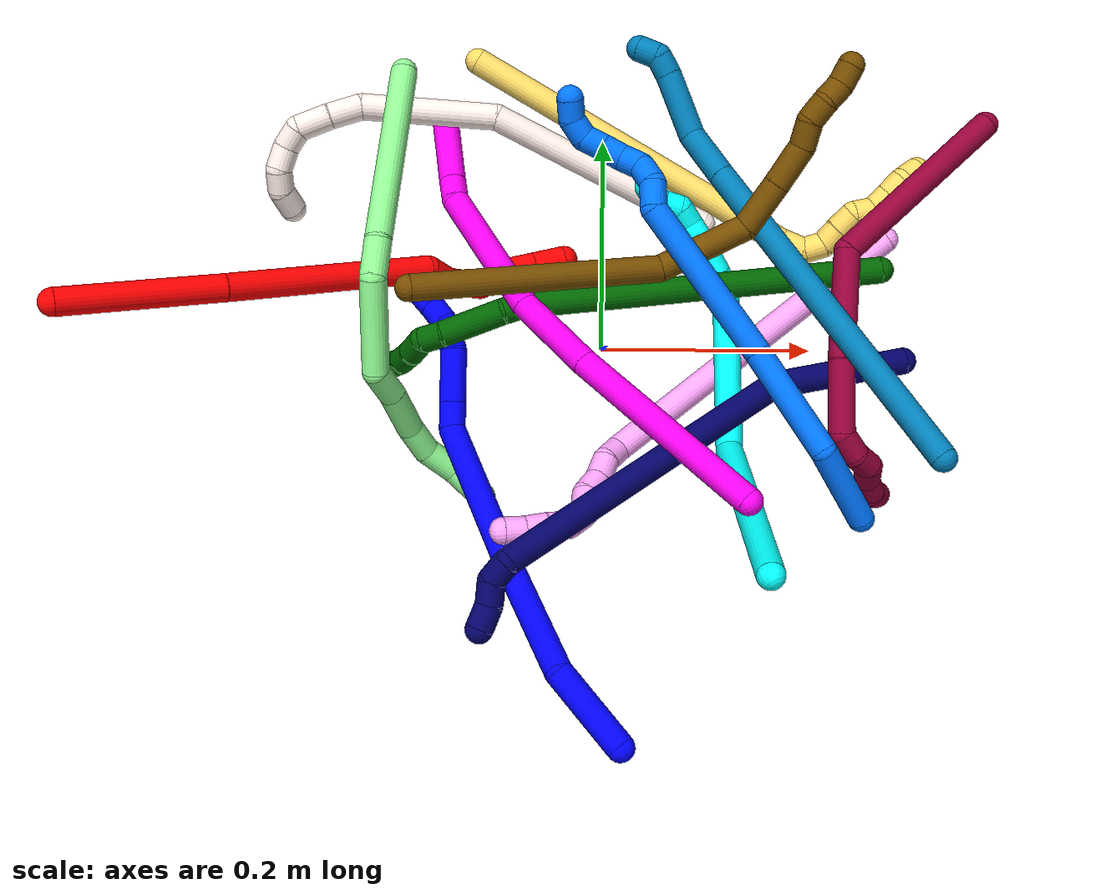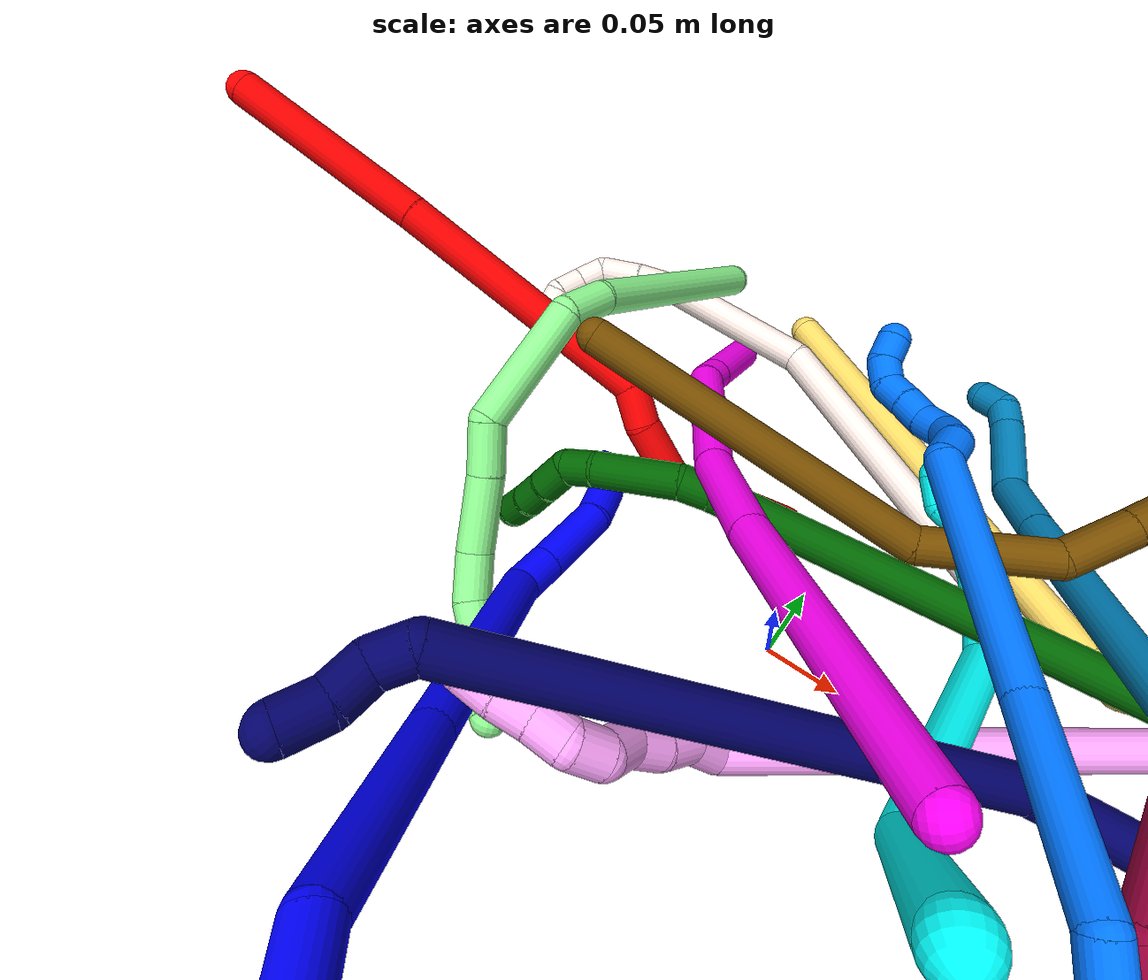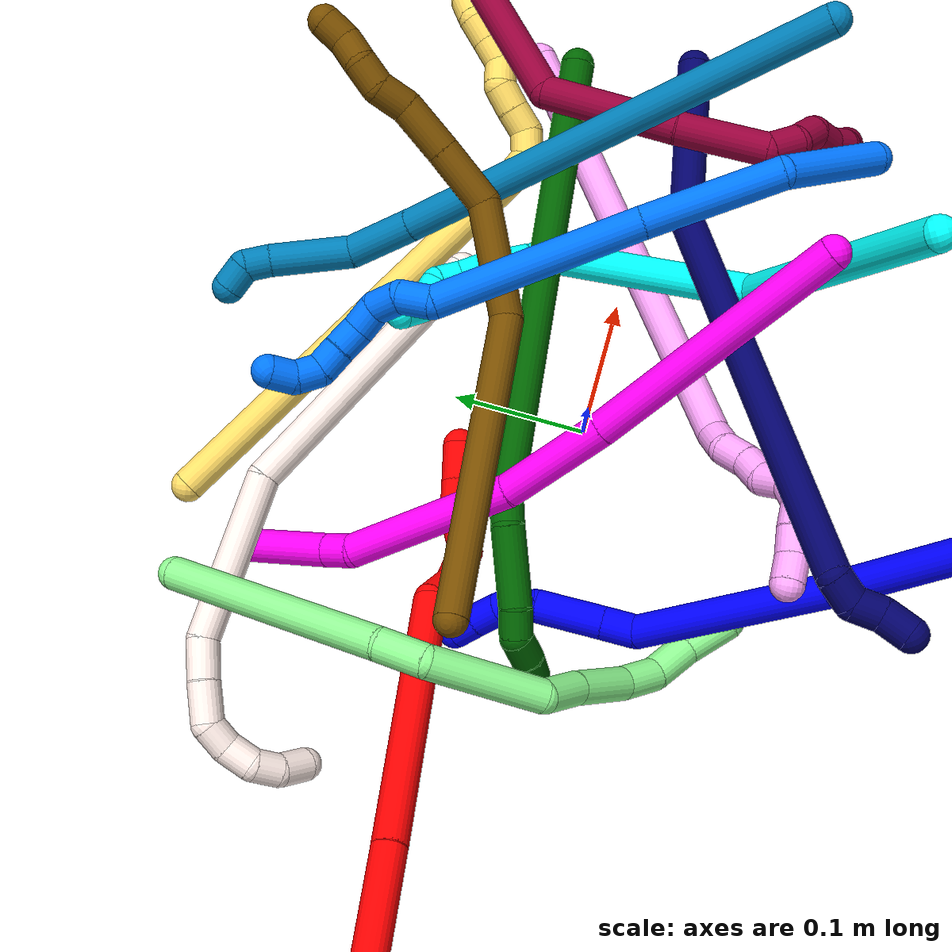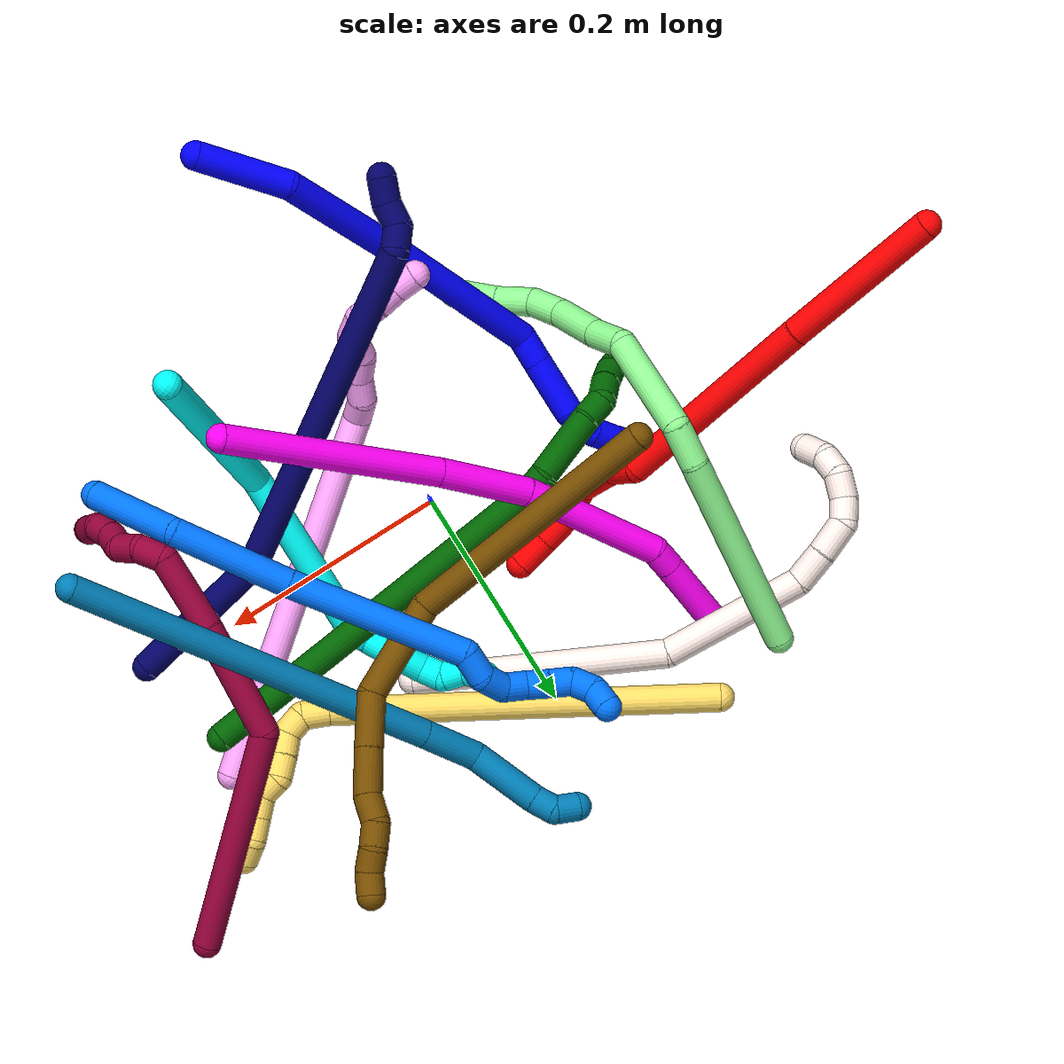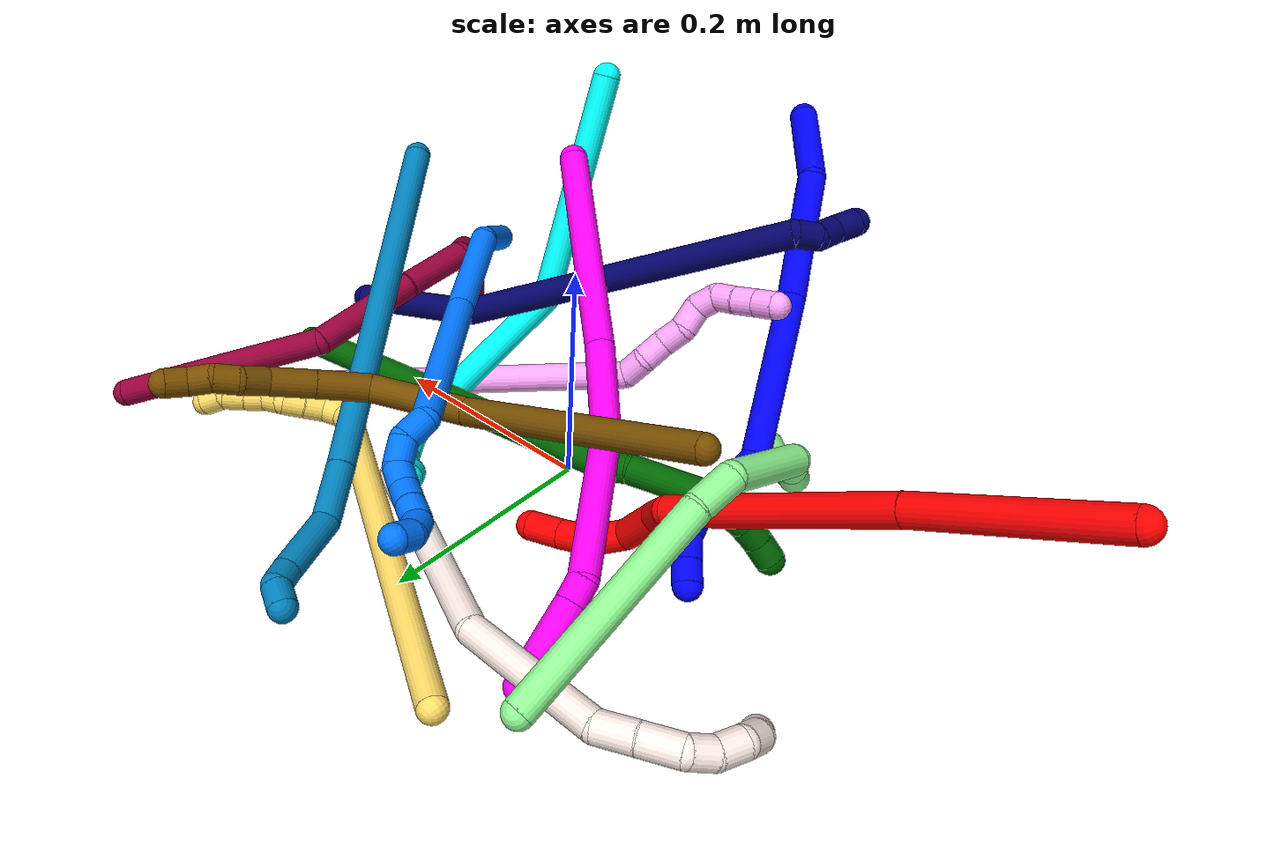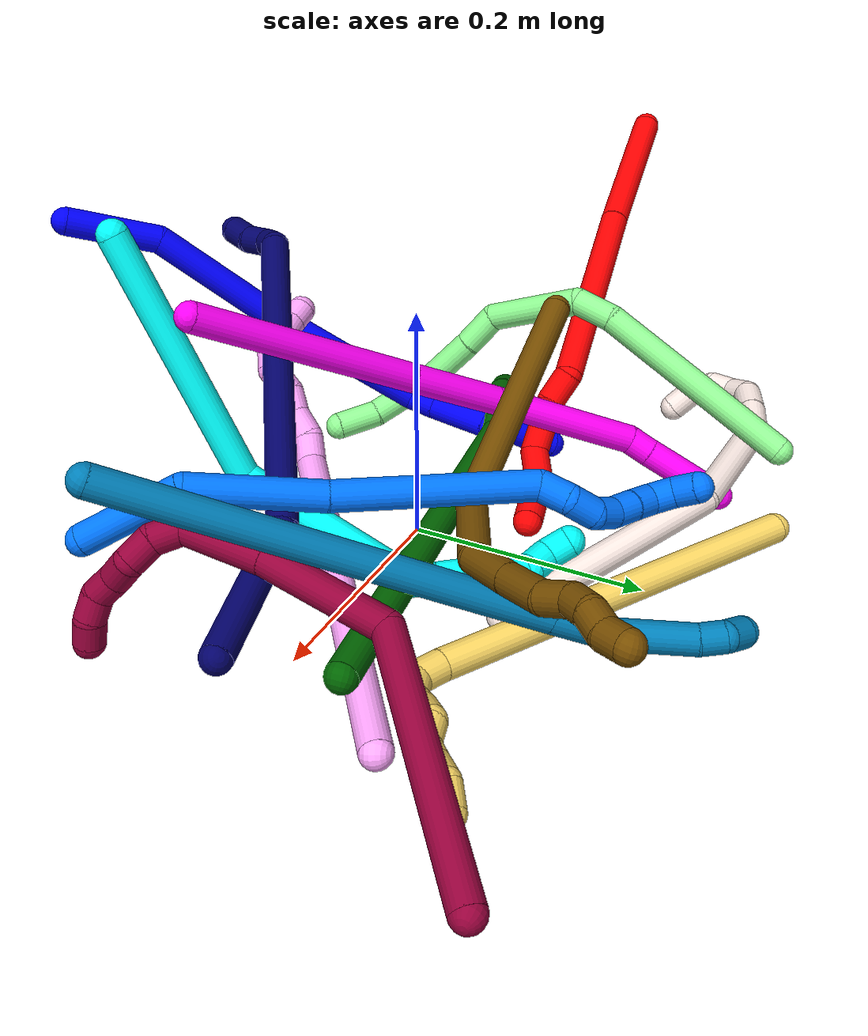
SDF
<sdf version="1.7">
 <world name="default">
  <plugin name="TubeGeneratorPlugin" filename="libtube_generator_plugin.so"/>
  <model name="photoneo_s_sensor">
   <static>1</static>
   <pose>0 0 2 1.57079 1.57079 3.14159</pose>
   <link name="link">
    <inertial><mass>0.1</mass></inertial>
    <sensor name="sensor" type="depth">
     <update_rate>30</update_rate>
     <camera>
      <horizontal_fov>1.22</horizontal_fov>
      <image><width>1920</width><height>1200</height><format>B8G8R8</format></image>
      <clip><near>0.1</near><far>4</far></clip>
      <depth_camera><output>points</output></depth_camera>
     </camera>
     <plugin name="camera_plugin" filename="libgazebo_ros_depth_camera.so">
      <baseline>0.2</baseline>
      <alwaysOn>1</alwaysOn>
      <updateRate>0.0</updateRate>
      <cameraName>camera_ir</cameraName>
      <imageTopicName>/camera/color/image_raw</imageTopicName>
      <cameraInfoTopicName>/camera/color/camera_info</cameraInfoTopicName>
      <depthImageTopicName>/camera/depth/image_raw</depthImageTopicName>
      <depthImageCameraInfoTopicName>/camera/depth/camera_info</depthImageCameraInfoTopicName>
      <pointCloudTopicName>/camera/depth/points</pointCloudTopicName>
      <frameName>fr_optical</frameName>
      <pointCloudCutoff>0.1</pointCloudCutoff>
      <pointCloudCutoffMax>2.0</pointCloudCutoffMax>
      <distortionK1>0</distortionK1>
      <distortionK2>0</distortionK2>
      <distortionK3>0</distortionK3>
      <distortionT1>0</distortionT1>
      <distortionT2>0</distortionT2>
      <CxPrime>0</CxPrime>
      <Cx>0</Cx>
      <Cy>0</Cy>
      <focalLength>0</focalLength>
      <hackBaseline>0</hackBaseline>
     </plugin>
    </sensor>
   </link>
  </model>
  <gravity>0 0 -9.8</gravity>
  <magnetic_field>6e-06 2.3e-05 -4.2e-05</magnetic_field>
  <atmosphere type="adiabatic"/>
  <physics name="default_physics" default="0" type="ode">
   <max_step_size>0.003</max_step_size>
   <real_time_factor>1</real_time_factor>
   <real_time_update_rate>1000</real_time_update_rate>
   <max_contacts>10000</max_contacts>
   <ode>
    <solver>
     <type>quick</type>
     <iters>100</iters>
     <sor>1.3</sor>
     <use_dynamic_moi_rescaling>0</use_dynamic_moi_rescaling>
    </solver>
    <constraints>
     <contact_max_correcting_vel>0</contact_max_correcting_vel>
     <contact_surface_layer>0.001</contact_surface_layer>
     <cfm>0</cfm>
     <erp>0.2</erp>
    </constraints>
   </ode>
  </physics>
  <scene><ambient>0.4 0.4 0.4 1</ambient><background>0.7 0.7 0.7 1</background><shadows>0</shadows></scene>
  <audio><device>default</device></audio>
  <spherical_coordinates>
   <surface_model>EARTH_WGS84</surface_model>
   <latitude_deg>0</latitude_deg>
   <longitude_deg>0</longitude_deg>
   <elevation>0</elevation>
   <heading_deg>0</heading_deg>
  </spherical_coordinates>
  <model name="bin">
   <static>1</static>
   <link name="bottom">
    <collision name="collision-bottom">
     <pose>0 0 -0.01 0 -0 0</pose>
     <geometry><box><size>0.8 0.6 0.02</size></box></geometry>
     <surface>
      <friction><ode><mu>100</mu><mu2>100</mu2></ode></friction>
      <contact><collide_bitmask>65535</collide_bitmask></contact>
     </surface>
    </collision>
   </link>
   <link name="west_wall">
    <collision name="collision-west_wall">
     <pose>-0.41 0 0.1 0 -0 0</pose>
     <geometry><box><size>0.02 0.6 0.2</size></box></geometry>
     <surface>
      <friction><ode><mu>100</mu><mu2>100</mu2></ode></friction>
      <contact><collide_bitmask>65535</collide_bitmask></contact>
     </surface>
    </collision>
   </link>
   <link name="east_wall">
    <collision name="collision-east_wall">
     <pose>0.41 0 0.1 0 -0 0</pose>
     <geometry><box><size>0.02 0.6 0.2</size></box></geometry>
     <surface>
      <friction><ode><mu>100</mu><mu2>100</mu2></ode></friction>
      <contact><collide_bitmask>65535</collide_bitmask></contact>
     </surface>
    </collision>
   </link>
   <link name="south_wall">
    <collision name="collision-south_wall">
     <pose>0 -0.31 0.1 0 -0 0</pose>
     <geometry><box><size>0.8 0.02 0.2</size></box></geometry>
     <surface>
      <friction><ode><mu>100</mu><mu2>100</mu2></ode></friction>
      <contact><collide_bitmask>65535</collide_bitmask></contact>
     </surface>
    </collision>
   </link>
   <link name="north_wall">
    <collision name="collision-north_wall">
     <pose>0 0.31 0.1 0 -0 0</pose>
     <geometry><box><size>0.8 0.02 0.2</size></box></geometry>
     <surface>
      <friction><ode><mu>100</mu><mu2>100</mu2></ode></friction>
      <contact><collide_bitmask>65535</collide_bitmask></contact>
     </surface>
    </collision>
   </link>
  </model>
  <model name="1">
   <static>0</static>
   <link name="1">
    <collision name="collision-cylinder-e_1_1_4">
     <pose>-0.002635 0.006434 -0.040411 -2.98372 -0.064309 0.772421</pose>
     <geometry><cylinder><radius>0.0125</radius><length>0.082009</length></cylinder></geometry>
     <surface>
      <friction><ode><mu>1.16</mu><mu2>1.16</mu2><slip1>0</slip1><slip2>0</slip2></ode></friction>
      <contact><ode><kp>1e+06</kp><kd>1</kd><max_vel>0</max_vel><min_depth>0.001</min_depth></ode></contact>
     </surface>
    </collision>
    <visual name="visual-cylinder-e_1_1_4">
     <pose>-0.002635 0.006434 -0.040411 -2.98372 -0.064309 0.772421</pose>
     <geometry><cylinder><radius>0.0125</radius><length>0.082009</length></cylinder></geometry>
     <material><ambient>0 0 1 1</ambient></material>
    </visual>
    <collision name="collision-cylinder-e_2_4_5">
     <pose>0.001349 0.042916 -0.131971 -2.61042 0.111114 -0.403353</pose>
     <geometry><cylinder><radius>0.0125</radius><length>0.119381</length></cylinder></geometry>
     <surface>
      <friction><ode><mu>1.16</mu><mu2>1.16</mu2><slip1>0</slip1><slip2>0</slip2></ode></friction>
      <contact><ode><kp>1e+06</kp><kd>1</kd><max_vel>0</max_vel><min_depth>0.001</min_depth></ode></contact>
     </surface>
    </collision>
    <visual name="visual-cylinder-e_2_4_5">
     <pose>0.001349 0.042916 -0.131971 -2.61042 0.111114 -0.403353</pose>
     <geometry><cylinder><radius>0.0125</radius><length>0.119381</length></cylinder></geometry>
     <material><ambient>0 0 1 1</ambient></material>
    </visual>
    <collision name="collision-cylinder-e_3_5_6">
     <pose>0.008865 0.11132 -0.249902 -2.62027 0.011654 -0.043684</pose>
     <geometry><cylinder><radius>0.0125</radius><length>0.154035</length></cylinder></geometry>
     <surface>
      <friction><ode><mu>1.16</mu><mu2>1.16</mu2><slip1>0</slip1><slip2>0</slip2></ode></friction>
      <contact><ode><kp>1e+06</kp><kd>1</kd><max_vel>0</max_vel><min_depth>0.001</min_depth></ode></contact>
     </surface>
    </collision>
    <visual name="visual-cylinder-e_3_5_6">
     <pose>0.008865 0.11132 -0.249902 -2.62027 0.011654 -0.043684</pose>
     <geometry><cylinder><radius>0.0125</radius><length>0.154035</length></cylinder></geometry>
     <material><ambient>0 0 1 1</ambient></material>
    </visual>
    <collision name="collision-cylinder-e_4_6_7">
     <pose>0.003537 0.157117 -0.324651 -2.39016 -0.518809 1.18446</pose>
     <geometry><cylinder><radius>0.0125</radius><length>0.025109</length></cylinder></geometry>
     <surface>
      <friction><ode><mu>1.16</mu><mu2>1.16</mu2><slip1>0</slip1><slip2>0</slip2></ode></friction>
      <contact><ode><kp>1e+06</kp><kd>1</kd><max_vel>0</max_vel><min_depth>0.001</min_depth></ode></contact>
     </surface>
    </collision>
    <visual name="visual-cylinder-e_4_6_7">
     <pose>0.003537 0.157117 -0.324651 -2.39016 -0.518809 1.18446</pose>
     <geometry><cylinder><radius>0.0125</radius><length>0.025109</length></cylinder></geometry>
     <material><ambient>0 0 1 1</ambient></material>
    </visual>
    <collision name="collision-cylinder-e_5_7_8">
     <pose>-0.015891 0.179035 -0.348889 -2.41456 -0.544985 1.26709</pose>
     <geometry><cylinder><radius>0.0125</radius><length>0.050936</length></cylinder></geometry>
     <surface>
      <friction><ode><mu>1.16</mu><mu2>1.16</mu2><slip1>0</slip1><slip2>0</slip2></ode></friction>
      <contact><ode><kp>1e+06</kp><kd>1</kd><max_vel>0</max_vel><min_depth>0.001</min_depth></ode></contact>
     </surface>
    </collision>
    <visual name="visual-cylinder-e_5_7_8">
     <pose>-0.015891 0.179035 -0.348889 -2.41456 -0.544985 1.26709</pose>
     <geometry><cylinder><radius>0.0125</radius><length>0.050936</length></cylinder></geometry>
     <material><ambient>0 0 1 1</ambient></material>
    </visual>
    <collision name="collision-cylinder-e_6_8_9">
     <pose>-0.034239 0.198505 -0.376557 -2.7285 -0.39215 1.51736</pose>
     <geometry><cylinder><radius>0.0125</radius><length>0.026928</length></cylinder></geometry>
     <surface>
      <friction><ode><mu>1.16</mu><mu2>1.16</mu2><slip1>0</slip1><slip2>0</slip2></ode></friction>
      <contact><ode><kp>1e+06</kp><kd>1</kd><max_vel>0</max_vel><min_depth>0.001</min_depth></ode></contact>
     </surface>
    </collision>
    <visual name="visual-cylinder-e_6_8_9">
     <pose>-0.034239 0.198505 -0.376557 -2.7285 -0.39215 1.51736</pose>
     <geometry><cylinder><radius>0.0125</radius><length>0.026928</length></cylinder></geometry>
     <material><ambient>0 0 1 1</ambient></material>
    </visual>
    <collision name="collision-cylinder-e_7_9_10">
     <pose>-0.038576 0.206837 -0.39819 -2.82651 0.074961 -0.46361</pose>
     <geometry><cylinder><radius>0.0125</radius><length>0.021598</length></cylinder></geometry>
     <surface>
      <friction><ode><mu>1.16</mu><mu2>1.16</mu2><slip1>0</slip1><slip2>0</slip2></ode></friction>
      <contact><ode><kp>1e+06</kp><kd>1</kd><max_vel>0</max_vel><min_depth>0.001</min_depth></ode></contact>
     </surface>
    </collision>
    <visual name="visual-cylinder-e_7_9_10">
     <pose>-0.038576 0.206837 -0.39819 -2.82651 0.074961 -0.46361</pose>
     <geometry><cylinder><radius>0.0125</radius><length>0.021598</length></cylinder></geometry>
     <material><ambient>0 0 1 1</ambient></material>
    </visual>
    <collision name="collision-cylinder-e_8_10_2">
     <pose>-0.037288 0.212593 -0.418121 -2.89702 0.047981 -0.385627</pose>
     <geometry><cylinder><radius>0.0125</radius><length>0.020003</length></cylinder></geometry>
     <surface>
      <friction><ode><mu>1.16</mu><mu2>1.16</mu2><slip1>0</slip1><slip2>0</slip2></ode></friction>
      <contact><ode><kp>1e+06</kp><kd>1</kd><max_vel>0</max_vel><min_depth>0.001</min_depth></ode></contact>
     </surface>
    </collision>
    <visual name="visual-cylinder-e_8_10_2">
     <pose>-0.037288 0.212593 -0.418121 -2.89702 0.047981 -0.385627</pose>
     <geometry><cylinder><radius>0.0125</radius><length>0.020003</length></cylinder></geometry>
     <material><ambient>0 0 1 1</ambient></material>
    </visual>
    <collision name="collision-sphere-2">
     <pose>-0.036808 0.215012 -0.427814 0 -0 0</pose>
     <geometry><sphere><radius>0.0125</radius></sphere></geometry>
     <surface>
      <friction><ode><mu>1.16</mu><mu2>1.16</mu2><slip1>0</slip1><slip2>0</slip2></ode></friction>
      <contact><ode><kp>1e+06</kp><kd>1</kd><max_vel>0</max_vel><min_depth>0.001</min_depth></ode></contact>
     </surface>
    </collision>
    <visual name="visual-sphere-2">
     <pose>-0.036808 0.215012 -0.427814 0 -0 0</pose>
     <geometry><sphere><radius>0.0125</radius></sphere></geometry>
     <material><ambient>0 0 1 1</ambient></material>
    </visual>
    <collision name="collision-sphere-10">
     <pose>-0.037768 0.210174 -0.408429 0 -0 0</pose>
     <geometry><sphere><radius>0.0125</radius></sphere></geometry>
     <surface>
      <friction><ode><mu>1.16</mu><mu2>1.16</mu2><slip1>0</slip1><slip2>0</slip2></ode></friction>
      <contact><ode><kp>1e+06</kp><kd>1</kd><max_vel>0</max_vel><min_depth>0.001</min_depth></ode></contact>
     </surface>
    </collision>
    <visual name="visual-sphere-10">
     <pose>-0.037768 0.210174 -0.408429 0 -0 0</pose>
     <geometry><sphere><radius>0.0125</radius></sphere></geometry>
     <material><ambient>0 0 1 1</ambient></material>
    </visual>
    <collision name="collision-sphere-9">
     <pose>-0.039385 0.2035 -0.387952 0 -0 0</pose>
     <geometry><sphere><radius>0.0125</radius></sphere></geometry>
     <surface>
      <friction><ode><mu>1.16</mu><mu2>1.16</mu2><slip1>0</slip1><slip2>0</slip2></ode></friction>
      <contact><ode><kp>1e+06</kp><kd>1</kd><max_vel>0</max_vel><min_depth>0.001</min_depth></ode></contact>
     </surface>
    </collision>
    <visual name="visual-sphere-9">
     <pose>-0.039385 0.2035 -0.387952 0 -0 0</pose>
     <geometry><sphere><radius>0.0125</radius></sphere></geometry>
     <material><ambient>0 0 1 1</ambient></material>
    </visual>
    <collision name="collision-sphere-4">
     <pose>-0.00527 0.012867 -0.080822 0 -0 0</pose>
     <geometry><sphere><radius>0.0125</radius></sphere></geometry>
     <surface>
      <friction><ode><mu>1.16</mu><mu2>1.16</mu2><slip1>0</slip1><slip2>0</slip2></ode></friction>
      <contact><ode><kp>1e+06</kp><kd>1</kd><max_vel>0</max_vel><min_depth>0.001</min_depth></ode></contact>
     </surface>
    </collision>
    <visual name="visual-sphere-4">
     <pose>-0.00527 0.012867 -0.080822 0 -0 0</pose>
     <geometry><sphere><radius>0.0125</radius></sphere></geometry>
     <material><ambient>0 0 1 1</ambient></material>
    </visual>
    <collision name="collision-sphere-1">
     <geometry><sphere><radius>0.0125</radius></sphere></geometry>
     <surface>
      <friction><ode><mu>1.16</mu><mu2>1.16</mu2><slip1>0</slip1><slip2>0</slip2></ode></friction>
      <contact><ode><kp>1e+06</kp><kd>1</kd><max_vel>0</max_vel><min_depth>0.001</min_depth></ode></contact>
     </surface>
    </collision>
    <visual name="visual-sphere-1">
     <geometry><sphere><radius>0.0125</radius></sphere></geometry>
     <material><ambient>0 0 1 1</ambient></material>
    </visual>
    <collision name="collision-sphere-8">
     <pose>-0.029094 0.193511 -0.365161 0 -0 0</pose>
     <geometry><sphere><radius>0.0125</radius></sphere></geometry>
     <surface>
      <friction><ode><mu>1.16</mu><mu2>1.16</mu2><slip1>0</slip1><slip2>0</slip2></ode></friction>
      <contact><ode><kp>1e+06</kp><kd>1</kd><max_vel>0</max_vel><min_depth>0.001</min_depth></ode></contact>
     </surface>
    </collision>
    <visual name="visual-sphere-8">
     <pose>-0.029094 0.193511 -0.365161 0 -0 0</pose>
     <geometry><sphere><radius>0.0125</radius></sphere></geometry>
     <material><ambient>0 0 1 1</ambient></material>
    </visual>
    <collision name="collision-sphere-5">
     <pose>0.007967 0.072966 -0.18312 0 -0 0</pose>
     <geometry><sphere><radius>0.0125</radius></sphere></geometry>
     <surface>
      <friction><ode><mu>1.16</mu><mu2>1.16</mu2><slip1>0</slip1><slip2>0</slip2></ode></friction>
      <contact><ode><kp>1e+06</kp><kd>1</kd><max_vel>0</max_vel><min_depth>0.001</min_depth></ode></contact>
     </surface>
    </collision>
    <visual name="visual-sphere-5">
     <pose>0.007967 0.072966 -0.18312 0 -0 0</pose>
     <geometry><sphere><radius>0.0125</radius></sphere></geometry>
     <material><ambient>0 0 1 1</ambient></material>
    </visual>
    <collision name="collision-sphere-6">
     <pose>0.009762 0.149674 -0.316684 0 -0 0</pose>
     <geometry><sphere><radius>0.0125</radius></sphere></geometry>
     <surface>
      <friction><ode><mu>1.16</mu><mu2>1.16</mu2><slip1>0</slip1><slip2>0</slip2></ode></friction>
      <contact><ode><kp>1e+06</kp><kd>1</kd><max_vel>0</max_vel><min_depth>0.001</min_depth></ode></contact>
     </surface>
    </collision>
    <visual name="visual-sphere-6">
     <pose>0.009762 0.149674 -0.316684 0 -0 0</pose>
     <geometry><sphere><radius>0.0125</radius></sphere></geometry>
     <material><ambient>0 0 1 1</ambient></material>
    </visual>
    <collision name="collision-sphere-7">
     <pose>-0.002688 0.16456 -0.332617 0 -0 0</pose>
     <geometry><sphere><radius>0.0125</radius></sphere></geometry>
     <surface>
      <friction><ode><mu>1.16</mu><mu2>1.16</mu2><slip1>0</slip1><slip2>0</slip2></ode></friction>
      <contact><ode><kp>1e+06</kp><kd>1</kd><max_vel>0</max_vel><min_depth>0.001</min_depth></ode></contact>
     </surface>
    </collision>
    <visual name="visual-sphere-7">
     <pose>-0.002688 0.16456 -0.332617 0 -0 0</pose>
     <geometry><sphere><radius>0.0125</radius></sphere></geometry>
     <material><ambient>0 0 1 1</ambient></material>
    </visual>
    <inertial>
     <pose>-0.003823 0.099855 -0.221178 0 -0 0</pose>
     <mass>0.5</mass>
     <inertia>
      <ixx>0.000461</ixx>
      <ixy>0</ixy>
      <ixz>0</ixz>
      <iyy>-0.000423</iyy>
      <iyz>0</iyz>
      <izz>-0.000288</izz>
     </inertia>
    </inertial>
   </link>
   <pose>0.012994 -0.335062 0.226887 -1.20604 0.815914 -1.97547</pose>
  </model>
  <model name="2">
   <static>0</static>
   <link name="2">
    <collision name="collision-cylinder-e_1_1_4">
     <pose>0.011321 -0.001796 -0.071567 3.11651 0.15684 2.82501</pose>
     <geometry><cylinder><radius>0.0125</radius><length>0.144959</length></cylinder></geometry>
     <surface>
      <friction><ode><mu>1.16</mu><mu2>1.16</mu2><slip1>0</slip1><slip2>0</slip2></ode></friction>
      <contact><ode><kp>1e+06</kp><kd>1</kd><max_vel>0</max_vel><min_depth>0.001</min_depth></ode></contact>
     </surface>
    </collision>
    <visual name="visual-cylinder-e_1_1_4">
     <pose>0.011321 -0.001796 -0.071567 3.11651 0.15684 2.82501</pose>
     <geometry><cylinder><radius>0.0125</radius><length>0.144959</length></cylinder></geometry>
     <material><ambient>1 0 0 1</ambient></material>
    </visual>
    <collision name="collision-cylinder-e_2_4_5">
     <pose>0.031217 -0.005475 -0.238502 3.12185 0.089653 2.70829</pose>
     <geometry><cylinder><radius>0.0125</radius><length>0.191541</length></cylinder></geometry>
     <surface>
      <friction><ode><mu>1.16</mu><mu2>1.16</mu2><slip1>0</slip1><slip2>0</slip2></ode></friction>
      <contact><ode><kp>1e+06</kp><kd>1</kd><max_vel>0</max_vel><min_depth>0.001</min_depth></ode></contact>
     </surface>
    </collision>
    <visual name="visual-cylinder-e_2_4_5">
     <pose>0.031217 -0.005475 -0.238502 3.12185 0.089653 2.70829</pose>
     <geometry><cylinder><radius>0.0125</radius><length>0.191541</length></cylinder></geometry>
     <material><ambient>1 0 0 1</ambient></material>
    </visual>
    <collision name="collision-cylinder-e_3_5_6">
     <pose>0.03575 -0.014207 -0.345818 2.62111 -0.28546 -0.989777</pose>
     <geometry><cylinder><radius>0.0125</radius><length>0.028706</length></cylinder></geometry>
     <surface>
      <friction><ode><mu>1.16</mu><mu2>1.16</mu2><slip1>0</slip1><slip2>0</slip2></ode></friction>
      <contact><ode><kp>1e+06</kp><kd>1</kd><max_vel>0</max_vel><min_depth>0.001</min_depth></ode></contact>
     </surface>
    </collision>
    <visual name="visual-cylinder-e_3_5_6">
     <pose>0.03575 -0.014207 -0.345818 2.62111 -0.28546 -0.989777</pose>
     <geometry><cylinder><radius>0.0125</radius><length>0.028706</length></cylinder></geometry>
     <material><ambient>1 0 0 1</ambient></material>
    </visual>
    <collision name="collision-cylinder-e_4_6_7">
     <pose>0.024002 -0.025673 -0.379618 2.93336 -0.332238 -2.02695</pose>
     <geometry><cylinder><radius>0.0125</radius><length>0.047253</length></cylinder></geometry>
     <surface>
      <friction><ode><mu>1.16</mu><mu2>1.16</mu2><slip1>0</slip1><slip2>0</slip2></ode></friction>
      <contact><ode><kp>1e+06</kp><kd>1</kd><max_vel>0</max_vel><min_depth>0.001</min_depth></ode></contact>
     </surface>
    </collision>
    <visual name="visual-cylinder-e_4_6_7">
     <pose>0.024002 -0.025673 -0.379618 2.93336 -0.332238 -2.02695</pose>
     <geometry><cylinder><radius>0.0125</radius><length>0.047253</length></cylinder></geometry>
     <material><ambient>1 0 0 1</ambient></material>
    </visual>
    <collision name="collision-cylinder-e_5_7_8">
     <pose>0.01728 -0.025084 -0.41573 -2.79154 0.064734 -0.362181</pose>
     <geometry><cylinder><radius>0.0125</radius><length>0.030425</length></cylinder></geometry>
     <surface>
      <friction><ode><mu>1.16</mu><mu2>1.16</mu2><slip1>0</slip1><slip2>0</slip2></ode></friction>
      <contact><ode><kp>1e+06</kp><kd>1</kd><max_vel>0</max_vel><min_depth>0.001</min_depth></ode></contact>
     </surface>
    </collision>
    <visual name="visual-cylinder-e_5_7_8">
     <pose>0.01728 -0.025084 -0.41573 -2.79154 0.064734 -0.362181</pose>
     <geometry><cylinder><radius>0.0125</radius><length>0.030425</length></cylinder></geometry>
     <material><ambient>1 0 0 1</ambient></material>
    </visual>
    <collision name="collision-cylinder-e_6_8_9">
     <pose>0.022907 -0.018347 -0.442924 -3.02378 0.342412 -2.48417</pose>
     <geometry><cylinder><radius>0.0125</radius><length>0.027654</length></cylinder></geometry>
     <surface>
      <friction><ode><mu>1.16</mu><mu2>1.16</mu2><slip1>0</slip1><slip2>0</slip2></ode></friction>
      <contact><ode><kp>1e+06</kp><kd>1</kd><max_vel>0</max_vel><min_depth>0.001</min_depth></ode></contact>
     </surface>
    </collision>
    <visual name="visual-cylinder-e_6_8_9">
     <pose>0.022907 -0.018347 -0.442924 -3.02378 0.342412 -2.48417</pose>
     <geometry><cylinder><radius>0.0125</radius><length>0.027654</length></cylinder></geometry>
     <material><ambient>1 0 0 1</ambient></material>
    </visual>
    <collision name="collision-cylinder-e_7_9_2">
     <pose>0.033586 -0.015025 -0.469176 -3.00794 0.422189 -2.53617</pose>
     <geometry><cylinder><radius>0.0125</radius><length>0.029462</length></cylinder></geometry>
     <surface>
      <friction><ode><mu>1.16</mu><mu2>1.16</mu2><slip1>0</slip1><slip2>0</slip2></ode></friction>
      <contact><ode><kp>1e+06</kp><kd>1</kd><max_vel>0</max_vel><min_depth>0.001</min_depth></ode></contact>
     </surface>
    </collision>
    <visual name="visual-cylinder-e_7_9_2">
     <pose>0.033586 -0.015025 -0.469176 -3.00794 0.422189 -2.53617</pose>
     <geometry><cylinder><radius>0.0125</radius><length>0.029462</length></cylinder></geometry>
     <material><ambient>1 0 0 1</ambient></material>
    </visual>
    <collision name="collision-sphere-2">
     <pose>0.039622 -0.013235 -0.482494 0 -0 0</pose>
     <geometry><sphere><radius>0.0125</radius></sphere></geometry>
     <surface>
      <friction><ode><mu>1.16</mu><mu2>1.16</mu2><slip1>0</slip1><slip2>0</slip2></ode></friction>
      <contact><ode><kp>1e+06</kp><kd>1</kd><max_vel>0</max_vel><min_depth>0.001</min_depth></ode></contact>
     </surface>
    </collision>
    <visual name="visual-sphere-2">
     <pose>0.039622 -0.013235 -0.482494 0 -0 0</pose>
     <geometry><sphere><radius>0.0125</radius></sphere></geometry>
     <material><ambient>1 0 0 1</ambient></material>
    </visual>
    <collision name="collision-sphere-9">
     <pose>0.027549 -0.016816 -0.455858 0 -0 0</pose>
     <geometry><sphere><radius>0.0125</radius></sphere></geometry>
     <surface>
      <friction><ode><mu>1.16</mu><mu2>1.16</mu2><slip1>0</slip1><slip2>0</slip2></ode></friction>
      <contact><ode><kp>1e+06</kp><kd>1</kd><max_vel>0</max_vel><min_depth>0.001</min_depth></ode></contact>
     </surface>
    </collision>
    <visual name="visual-sphere-9">
     <pose>0.027549 -0.016816 -0.455858 0 -0 0</pose>
     <geometry><sphere><radius>0.0125</radius></sphere></geometry>
     <material><ambient>1 0 0 1</ambient></material>
    </visual>
    <collision name="collision-sphere-4">
     <pose>0.022642 -0.003591 -0.143134 0 -0 0</pose>
     <geometry><sphere><radius>0.0125</radius></sphere></geometry>
     <surface>
      <friction><ode><mu>1.16</mu><mu2>1.16</mu2><slip1>0</slip1><slip2>0</slip2></ode></friction>
      <contact><ode><kp>1e+06</kp><kd>1</kd><max_vel>0</max_vel><min_depth>0.001</min_depth></ode></contact>
     </surface>
    </collision>
    <visual name="visual-sphere-4">
     <pose>0.022642 -0.003591 -0.143134 0 -0 0</pose>
     <geometry><sphere><radius>0.0125</radius></sphere></geometry>
     <material><ambient>1 0 0 1</ambient></material>
    </visual>
    <collision name="collision-sphere-1">
     <geometry><sphere><radius>0.0125</radius></sphere></geometry>
     <surface>
      <friction><ode><mu>1.16</mu><mu2>1.16</mu2><slip1>0</slip1><slip2>0</slip2></ode></friction>
      <contact><ode><kp>1e+06</kp><kd>1</kd><max_vel>0</max_vel><min_depth>0.001</min_depth></ode></contact>
     </surface>
    </collision>
    <visual name="visual-sphere-1">
     <geometry><sphere><radius>0.0125</radius></sphere></geometry>
     <material><ambient>1 0 0 1</ambient></material>
    </visual>
    <collision name="collision-sphere-8">
     <pose>0.018264 -0.019878 -0.42999 0 -0 0</pose>
     <geometry><sphere><radius>0.0125</radius></sphere></geometry>
     <surface>
      <friction><ode><mu>1.16</mu><mu2>1.16</mu2><slip1>0</slip1><slip2>0</slip2></ode></friction>
      <contact><ode><kp>1e+06</kp><kd>1</kd><max_vel>0</max_vel><min_depth>0.001</min_depth></ode></contact>
     </surface>
    </collision>
    <visual name="visual-sphere-8">
     <pose>0.018264 -0.019878 -0.42999 0 -0 0</pose>
     <geometry><sphere><radius>0.0125</radius></sphere></geometry>
     <material><ambient>1 0 0 1</ambient></material>
    </visual>
    <collision name="collision-sphere-5">
     <pose>0.039791 -0.007358 -0.333869 0 -0 0</pose>
     <geometry><sphere><radius>0.0125</radius></sphere></geometry>
     <surface>
      <friction><ode><mu>1.16</mu><mu2>1.16</mu2><slip1>0</slip1><slip2>0</slip2></ode></friction>
      <contact><ode><kp>1e+06</kp><kd>1</kd><max_vel>0</max_vel><min_depth>0.001</min_depth></ode></contact>
     </surface>
    </collision>
    <visual name="visual-sphere-5">
     <pose>0.039791 -0.007358 -0.333869 0 -0 0</pose>
     <geometry><sphere><radius>0.0125</radius></sphere></geometry>
     <material><ambient>1 0 0 1</ambient></material>
    </visual>
    <collision name="collision-sphere-6">
     <pose>0.031708 -0.021056 -0.357766 0 -0 0</pose>
     <geometry><sphere><radius>0.0125</radius></sphere></geometry>
     <surface>
      <friction><ode><mu>1.16</mu><mu2>1.16</mu2><slip1>0</slip1><slip2>0</slip2></ode></friction>
      <contact><ode><kp>1e+06</kp><kd>1</kd><max_vel>0</max_vel><min_depth>0.001</min_depth></ode></contact>
     </surface>
    </collision>
    <visual name="visual-sphere-6">
     <pose>0.031708 -0.021056 -0.357766 0 -0 0</pose>
     <geometry><sphere><radius>0.0125</radius></sphere></geometry>
     <material><ambient>1 0 0 1</ambient></material>
    </visual>
    <collision name="collision-sphere-7">
     <pose>0.016296 -0.03029 -0.40147 0 -0 0</pose>
     <geometry><sphere><radius>0.0125</radius></sphere></geometry>
     <surface>
      <friction><ode><mu>1.16</mu><mu2>1.16</mu2><slip1>0</slip1><slip2>0</slip2></ode></friction>
      <contact><ode><kp>1e+06</kp><kd>1</kd><max_vel>0</max_vel><min_depth>0.001</min_depth></ode></contact>
     </surface>
    </collision>
    <visual name="visual-sphere-7">
     <pose>0.016296 -0.03029 -0.40147 0 -0 0</pose>
     <geometry><sphere><radius>0.0125</radius></sphere></geometry>
     <material><ambient>1 0 0 1</ambient></material>
    </visual>
    <inertial>
     <pose>0.023859 -0.009286 -0.245285 0 -0 0</pose>
     <mass>0.5</mass>
     <inertia>
      <ixx>-0.000469</ixx>
      <ixy>0</ixy>
      <ixz>0</ixz>
      <iyy>0.001102</iyy>
      <iyz>0</iyz>
      <izz>-0.00011</izz>
     </inertia>
    </inertial>
   </link>
   <pose>-0.460368 0.032047 0.23939 0.224449 -0.986874 -0.095469</pose>
  </model>
  <model name="3">
   <static>0</static>
   <link name="3">
    <collision name="collision-cylinder-e_1_1_4">
     <pose>0.070438 -0.009194 -0.078288 3.02469 0.729261 2.83734</pose>
     <geometry><cylinder><radius>0.0125</radius><length>0.211425</length></cylinder></geometry>
     <surface>
      <friction><ode><mu>1.16</mu><mu2>1.16</mu2><slip1>0</slip1><slip2>0</slip2></ode></friction>
      <contact><ode><kp>1e+06</kp><kd>1</kd><max_vel>0</max_vel><min_depth>0.001</min_depth></ode></contact>
     </surface>
    </collision>
    <visual name="visual-cylinder-e_1_1_4">
     <pose>0.070438 -0.009194 -0.078288 3.02469 0.729261 2.83734</pose>
     <geometry><cylinder><radius>0.0125</radius><length>0.211425</length></cylinder></geometry>
     <material><ambient>0.003922 1 0.996078 1</ambient></material>
    </visual>
    <collision name="collision-cylinder-e_2_4_5">
     <pose>0.150536 0.014157 -0.226496 -2.70594 0.124601 -0.549429</pose>
     <geometry><cylinder><radius>0.0125</radius><length>0.155449</length></cylinder></geometry>
     <surface>
      <friction><ode><mu>1.16</mu><mu2>1.16</mu2><slip1>0</slip1><slip2>0</slip2></ode></friction>
      <contact><ode><kp>1e+06</kp><kd>1</kd><max_vel>0</max_vel><min_depth>0.001</min_depth></ode></contact>
     </surface>
    </collision>
    <visual name="visual-cylinder-e_2_4_5">
     <pose>0.150536 0.014157 -0.226496 -2.70594 0.124601 -0.549429</pose>
     <geometry><cylinder><radius>0.0125</radius><length>0.155449</length></cylinder></geometry>
     <material><ambient>0.003922 1 0.996078 1</ambient></material>
    </visual>
    <collision name="collision-cylinder-e_3_5_6">
     <pose>0.155204 0.048942 -0.304882 -2.88301 -0.518046 2.22928</pose>
     <geometry><cylinder><radius>0.0125</radius><length>0.020163</length></cylinder></geometry>
     <surface>
      <friction><ode><mu>1.16</mu><mu2>1.16</mu2><slip1>0</slip1><slip2>0</slip2></ode></friction>
      <contact><ode><kp>1e+06</kp><kd>1</kd><max_vel>0</max_vel><min_depth>0.001</min_depth></ode></contact>
     </surface>
    </collision>
    <visual name="visual-cylinder-e_3_5_6">
     <pose>0.155204 0.048942 -0.304882 -2.88301 -0.518046 2.22928</pose>
     <geometry><cylinder><radius>0.0125</radius><length>0.020163</length></cylinder></geometry>
     <material><ambient>0.003922 1 0.996078 1</ambient></material>
    </visual>
    <collision name="collision-cylinder-e_4_6_7">
     <pose>0.142216 0.053521 -0.327409 -2.97676 -0.511236 2.5293</pose>
     <geometry><cylinder><radius>0.0125</radius><length>0.032685</length></cylinder></geometry>
     <surface>
      <friction><ode><mu>1.16</mu><mu2>1.16</mu2><slip1>0</slip1><slip2>0</slip2></ode></friction>
      <contact><ode><kp>1e+06</kp><kd>1</kd><max_vel>0</max_vel><min_depth>0.001</min_depth></ode></contact>
     </surface>
    </collision>
    <visual name="visual-cylinder-e_4_6_7">
     <pose>0.142216 0.053521 -0.327409 -2.97676 -0.511236 2.5293</pose>
     <geometry><cylinder><radius>0.0125</radius><length>0.032685</length></cylinder></geometry>
     <material><ambient>0.003922 1 0.996078 1</ambient></material>
    </visual>
    <collision name="collision-cylinder-e_5_7_8">
     <pose>0.133088 0.055756 -0.351429 3.13123 -0.113226 -2.95925</pose>
     <geometry><cylinder><radius>0.0125</radius><length>0.020051</length></cylinder></geometry>
     <surface>
      <friction><ode><mu>1.16</mu><mu2>1.16</mu2><slip1>0</slip1><slip2>0</slip2></ode></friction>
      <contact><ode><kp>1e+06</kp><kd>1</kd><max_vel>0</max_vel><min_depth>0.001</min_depth></ode></contact>
     </surface>
    </collision>
    <visual name="visual-cylinder-e_5_7_8">
     <pose>0.133088 0.055756 -0.351429 3.13123 -0.113226 -2.95925</pose>
     <geometry><cylinder><radius>0.0125</radius><length>0.020051</length></cylinder></geometry>
     <material><ambient>0.003922 1 0.996078 1</ambient></material>
    </visual>
    <collision name="collision-cylinder-e_6_8_9">
     <pose>0.124922 0.056794 -0.368493 -2.98229 -0.774049 2.75481</pose>
     <geometry><cylinder><radius>0.0125</radius><length>0.020121</length></cylinder></geometry>
     <surface>
      <friction><ode><mu>1.16</mu><mu2>1.16</mu2><slip1>0</slip1><slip2>0</slip2></ode></friction>
      <contact><ode><kp>1e+06</kp><kd>1</kd><max_vel>0</max_vel><min_depth>0.001</min_depth></ode></contact>
     </surface>
    </collision>
    <visual name="visual-cylinder-e_6_8_9">
     <pose>0.124922 0.056794 -0.368493 -2.98229 -0.774049 2.75481</pose>
     <geometry><cylinder><radius>0.0125</radius><length>0.020121</length></cylinder></geometry>
     <material><ambient>0.003922 1 0.996078 1</ambient></material>
    </visual>
    <collision name="collision-cylinder-e_7_9_10">
     <pose>0.111981 0.052229 -0.381354 2.36067 -0.629824 -1.33899</pose>
     <geometry><cylinder><radius>0.0125</radius><length>0.020062</length></cylinder></geometry>
     <surface>
      <friction><ode><mu>1.16</mu><mu2>1.16</mu2><slip1>0</slip1><slip2>0</slip2></ode></friction>
      <contact><ode><kp>1e+06</kp><kd>1</kd><max_vel>0</max_vel><min_depth>0.001</min_depth></ode></contact>
     </surface>
    </collision>
    <visual name="visual-cylinder-e_7_9_10">
     <pose>0.111981 0.052229 -0.381354 2.36067 -0.629824 -1.33899</pose>
     <geometry><cylinder><radius>0.0125</radius><length>0.020062</length></cylinder></geometry>
     <material><ambient>0.003922 1 0.996078 1</ambient></material>
    </visual>
    <collision name="collision-cylinder-e_8_10_2">
     <pose>0.098169 0.047051 -0.393251 -3.05574 -0.908618 2.96615</pose>
     <geometry><cylinder><radius>0.0125</radius><length>0.020043</length></cylinder></geometry>
     <surface>
      <friction><ode><mu>1.16</mu><mu2>1.16</mu2><slip1>0</slip1><slip2>0</slip2></ode></friction>
      <contact><ode><kp>1e+06</kp><kd>1</kd><max_vel>0</max_vel><min_depth>0.001</min_depth></ode></contact>
     </surface>
    </collision>
    <visual name="visual-cylinder-e_8_10_2">
     <pose>0.098169 0.047051 -0.393251 -3.05574 -0.908618 2.96615</pose>
     <geometry><cylinder><radius>0.0125</radius><length>0.020043</length></cylinder></geometry>
     <material><ambient>0.003922 1 0.996078 1</ambient></material>
    </visual>
    <collision name="collision-sphere-2">
     <pose>0.090266 0.047579 -0.39939 0 -0 0</pose>
     <geometry><sphere><radius>0.0125</radius></sphere></geometry>
     <surface>
      <friction><ode><mu>1.16</mu><mu2>1.16</mu2><slip1>0</slip1><slip2>0</slip2></ode></friction>
      <contact><ode><kp>1e+06</kp><kd>1</kd><max_vel>0</max_vel><min_depth>0.001</min_depth></ode></contact>
     </surface>
    </collision>
    <visual name="visual-sphere-2">
     <pose>0.090266 0.047579 -0.39939 0 -0 0</pose>
     <geometry><sphere><radius>0.0125</radius></sphere></geometry>
     <material><ambient>0.003922 1 0.996078 1</ambient></material>
    </visual>
    <collision name="collision-sphere-10">
     <pose>0.106073 0.046522 -0.387112 0 -0 0</pose>
     <geometry><sphere><radius>0.0125</radius></sphere></geometry>
     <surface>
      <friction><ode><mu>1.16</mu><mu2>1.16</mu2><slip1>0</slip1><slip2>0</slip2></ode></friction>
      <contact><ode><kp>1e+06</kp><kd>1</kd><max_vel>0</max_vel><min_depth>0.001</min_depth></ode></contact>
     </surface>
    </collision>
    <visual name="visual-sphere-10">
     <pose>0.106073 0.046522 -0.387112 0 -0 0</pose>
     <geometry><sphere><radius>0.0125</radius></sphere></geometry>
     <material><ambient>0.003922 1 0.996078 1</ambient></material>
    </visual>
    <collision name="collision-sphere-9">
     <pose>0.11789 0.057935 -0.375596 0 -0 0</pose>
     <geometry><sphere><radius>0.0125</radius></sphere></geometry>
     <surface>
      <friction><ode><mu>1.16</mu><mu2>1.16</mu2><slip1>0</slip1><slip2>0</slip2></ode></friction>
      <contact><ode><kp>1e+06</kp><kd>1</kd><max_vel>0</max_vel><min_depth>0.001</min_depth></ode></contact>
     </surface>
    </collision>
    <visual name="visual-sphere-9">
     <pose>0.11789 0.057935 -0.375596 0 -0 0</pose>
     <geometry><sphere><radius>0.0125</radius></sphere></geometry>
     <material><ambient>0.003922 1 0.996078 1</ambient></material>
    </visual>
    <collision name="collision-sphere-4">
     <pose>0.140877 -0.018388 -0.156577 0 -0 0</pose>
     <geometry><sphere><radius>0.0125</radius></sphere></geometry>
     <surface>
      <friction><ode><mu>1.16</mu><mu2>1.16</mu2><slip1>0</slip1><slip2>0</slip2></ode></friction>
      <contact><ode><kp>1e+06</kp><kd>1</kd><max_vel>0</max_vel><min_depth>0.001</min_depth></ode></contact>
     </surface>
    </collision>
    <visual name="visual-sphere-4">
     <pose>0.140877 -0.018388 -0.156577 0 -0 0</pose>
     <geometry><sphere><radius>0.0125</radius></sphere></geometry>
     <material><ambient>0.003922 1 0.996078 1</ambient></material>
    </visual>
    <collision name="collision-sphere-1">
     <geometry><sphere><radius>0.0125</radius></sphere></geometry>
     <surface>
      <friction><ode><mu>1.16</mu><mu2>1.16</mu2><slip1>0</slip1><slip2>0</slip2></ode></friction>
      <contact><ode><kp>1e+06</kp><kd>1</kd><max_vel>0</max_vel><min_depth>0.001</min_depth></ode></contact>
     </surface>
    </collision>
    <visual name="visual-sphere-1">
     <geometry><sphere><radius>0.0125</radius></sphere></geometry>
     <material><ambient>0.003922 1 0.996078 1</ambient></material>
    </visual>
    <collision name="collision-sphere-8">
     <pose>0.131955 0.055653 -0.36139 0 -0 0</pose>
     <geometry><sphere><radius>0.0125</radius></sphere></geometry>
     <surface>
      <friction><ode><mu>1.16</mu><mu2>1.16</mu2><slip1>0</slip1><slip2>0</slip2></ode></friction>
      <contact><ode><kp>1e+06</kp><kd>1</kd><max_vel>0</max_vel><min_depth>0.001</min_depth></ode></contact>
     </surface>
    </collision>
    <visual name="visual-sphere-8">
     <pose>0.131955 0.055653 -0.36139 0 -0 0</pose>
     <geometry><sphere><radius>0.0125</radius></sphere></geometry>
     <material><ambient>0.003922 1 0.996078 1</ambient></material>
    </visual>
    <collision name="collision-sphere-5">
     <pose>0.160196 0.046703 -0.296414 0 -0 0</pose>
     <geometry><sphere><radius>0.0125</radius></sphere></geometry>
     <surface>
      <friction><ode><mu>1.16</mu><mu2>1.16</mu2><slip1>0</slip1><slip2>0</slip2></ode></friction>
      <contact><ode><kp>1e+06</kp><kd>1</kd><max_vel>0</max_vel><min_depth>0.001</min_depth></ode></contact>
     </surface>
    </collision>
    <visual name="visual-sphere-5">
     <pose>0.160196 0.046703 -0.296414 0 -0 0</pose>
     <geometry><sphere><radius>0.0125</radius></sphere></geometry>
     <material><ambient>0.003922 1 0.996078 1</ambient></material>
    </visual>
    <collision name="collision-sphere-6">
     <pose>0.150212 0.051182 -0.313349 0 -0 0</pose>
     <geometry><sphere><radius>0.0125</radius></sphere></geometry>
     <surface>
      <friction><ode><mu>1.16</mu><mu2>1.16</mu2><slip1>0</slip1><slip2>0</slip2></ode></friction>
      <contact><ode><kp>1e+06</kp><kd>1</kd><max_vel>0</max_vel><min_depth>0.001</min_depth></ode></contact>
     </surface>
    </collision>
    <visual name="visual-sphere-6">
     <pose>0.150212 0.051182 -0.313349 0 -0 0</pose>
     <geometry><sphere><radius>0.0125</radius></sphere></geometry>
     <material><ambient>0.003922 1 0.996078 1</ambient></material>
    </visual>
    <collision name="collision-sphere-7">
     <pose>0.13422 0.055859 -0.341469 0 -0 0</pose>
     <geometry><sphere><radius>0.0125</radius></sphere></geometry>
     <surface>
      <friction><ode><mu>1.16</mu><mu2>1.16</mu2><slip1>0</slip1><slip2>0</slip2></ode></friction>
      <contact><ode><kp>1e+06</kp><kd>1</kd><max_vel>0</max_vel><min_depth>0.001</min_depth></ode></contact>
     </surface>
    </collision>
    <visual name="visual-sphere-7">
     <pose>0.13422 0.055859 -0.341469 0 -0 0</pose>
     <geometry><sphere><radius>0.0125</radius></sphere></geometry>
     <material><ambient>0.003922 1 0.996078 1</ambient></material>
    </visual>
    <inertial>
     <pose>0.110934 0.014489 -0.197206 0 -0 0</pose>
     <mass>0.5</mass>
     <inertia>
      <ixx>-0.000281</ixx>
      <ixy>0</ixy>
      <ixz>0</ixz>
      <iyy>0.000562</iyy>
      <iyz>0</iyz>
      <izz>-0.00066</izz>
     </inertia>
    </inertial>
   </link>
   <pose>0.130781 -0.18417 0.277329 0.652763 1.05044 -0.369888</pose>
  </model>
  <model name="4">
   <static>0</static>
   <link name="4">
    <collision name="collision-cylinder-e_1_1_4">
     <pose>-0.100805 -0.10453 0.074385 0.952317 -0.665978 -0.353041</pose>
     <geometry><cylinder><radius>0.0125</radius><length>0.326322</length></cylinder></geometry>
     <surface>
      <friction><ode><mu>1.16</mu><mu2>1.16</mu2><slip1>0</slip1><slip2>0</slip2></ode></friction>
      <contact><ode><kp>1e+06</kp><kd>1</kd><max_vel>0</max_vel><min_depth>0.001</min_depth></ode></contact>
     </surface>
    </collision>
    <visual name="visual-cylinder-e_1_1_4">
     <pose>-0.100805 -0.10453 0.074385 0.952317 -0.665978 -0.353041</pose>
     <geometry><cylinder><radius>0.0125</radius><length>0.326322</length></cylinder></geometry>
     <material><ambient>1 0.65098 0.996078 1</ambient></material>
    </visual>
    <collision name="collision-cylinder-e_2_4_5">
     <pose>-0.213152 -0.20997 0.150888 0.405773 -1.37369 -0.334249</pose>
     <geometry><cylinder><radius>0.0125</radius><length>0.023538</length></cylinder></geometry>
     <surface>
      <friction><ode><mu>1.16</mu><mu2>1.16</mu2><slip1>0</slip1><slip2>0</slip2></ode></friction>
      <contact><ode><kp>1e+06</kp><kd>1</kd><max_vel>0</max_vel><min_depth>0.001</min_depth></ode></contact>
     </surface>
    </collision>
    <visual name="visual-cylinder-e_2_4_5">
     <pose>-0.213152 -0.20997 0.150888 0.405773 -1.37369 -0.334249</pose>
     <geometry><cylinder><radius>0.0125</radius><length>0.023538</length></cylinder></geometry>
     <material><ambient>1 0.65098 0.996078 1</ambient></material>
    </visual>
    <collision name="collision-cylinder-e_3_5_6">
     <pose>-0.2343 -0.211096 0.159565 0.032971 -0.971473 -0.017407</pose>
     <geometry><cylinder><radius>0.0125</radius><length>0.02327</length></cylinder></geometry>
     <surface>
      <friction><ode><mu>1.16</mu><mu2>1.16</mu2><slip1>0</slip1><slip2>0</slip2></ode></friction>
      <contact><ode><kp>1e+06</kp><kd>1</kd><max_vel>0</max_vel><min_depth>0.001</min_depth></ode></contact>
     </surface>
    </collision>
    <visual name="visual-cylinder-e_3_5_6">
     <pose>-0.2343 -0.211096 0.159565 0.032971 -0.971473 -0.017407</pose>
     <geometry><cylinder><radius>0.0125</radius><length>0.02327</length></cylinder></geometry>
     <material><ambient>1 0.65098 0.996078 1</ambient></material>
    </visual>
    <collision name="collision-cylinder-e_4_6_7">
     <pose>-0.254195 -0.212854 0.16981 0.395996 -1.20041 -0.272926</pose>
     <geometry><cylinder><radius>0.0125</radius><length>0.022072</length></cylinder></geometry>
     <surface>
      <friction><ode><mu>1.16</mu><mu2>1.16</mu2><slip1>0</slip1><slip2>0</slip2></ode></friction>
      <contact><ode><kp>1e+06</kp><kd>1</kd><max_vel>0</max_vel><min_depth>0.001</min_depth></ode></contact>
     </surface>
    </collision>
    <visual name="visual-cylinder-e_4_6_7">
     <pose>-0.254195 -0.212854 0.16981 0.395996 -1.20041 -0.272926</pose>
     <geometry><cylinder><radius>0.0125</radius><length>0.022072</length></cylinder></geometry>
     <material><ambient>1 0.65098 0.996078 1</ambient></material>
    </visual>
    <collision name="collision-cylinder-e_5_7_8">
     <pose>-0.273508 -0.211281 0.180109 -0.440106 -0.890062 0.212556</pose>
     <geometry><cylinder><radius>0.0125</radius><length>0.023227</length></cylinder></geometry>
     <surface>
      <friction><ode><mu>1.16</mu><mu2>1.16</mu2><slip1>0</slip1><slip2>0</slip2></ode></friction>
      <contact><ode><kp>1e+06</kp><kd>1</kd><max_vel>0</max_vel><min_depth>0.001</min_depth></ode></contact>
     </surface>
    </collision>
    <visual name="visual-cylinder-e_5_7_8">
     <pose>-0.273508 -0.211281 0.180109 -0.440106 -0.890062 0.212556</pose>
     <geometry><cylinder><radius>0.0125</radius><length>0.023227</length></cylinder></geometry>
     <material><ambient>1 0.65098 0.996078 1</ambient></material>
    </visual>
    <collision name="collision-cylinder-e_6_8_9">
     <pose>-0.292368 -0.211064 0.188825 0.942763 -1.2217 -0.685593</pose>
     <geometry><cylinder><radius>0.0125</radius><length>0.020933</length></cylinder></geometry>
     <surface>
      <friction><ode><mu>1.16</mu><mu2>1.16</mu2><slip1>0</slip1><slip2>0</slip2></ode></friction>
      <contact><ode><kp>1e+06</kp><kd>1</kd><max_vel>0</max_vel><min_depth>0.001</min_depth></ode></contact>
     </surface>
    </collision>
    <visual name="visual-cylinder-e_6_8_9">
     <pose>-0.292368 -0.211064 0.188825 0.942763 -1.2217 -0.685593</pose>
     <geometry><cylinder><radius>0.0125</radius><length>0.020933</length></cylinder></geometry>
     <material><ambient>1 0.65098 0.996078 1</ambient></material>
    </visual>
    <collision name="collision-cylinder-e_7_9_10">
     <pose>-0.308823 -0.221396 0.189537 1.75575 -0.718826 -0.849942</pose>
     <geometry><cylinder><radius>0.0125</radius><length>0.020103</length></cylinder></geometry>
     <surface>
      <friction><ode><mu>1.16</mu><mu2>1.16</mu2><slip1>0</slip1><slip2>0</slip2></ode></friction>
      <contact><ode><kp>1e+06</kp><kd>1</kd><max_vel>0</max_vel><min_depth>0.001</min_depth></ode></contact>
     </surface>
    </collision>
    <visual name="visual-cylinder-e_7_9_10">
     <pose>-0.308823 -0.221396 0.189537 1.75575 -0.718826 -0.849942</pose>
     <geometry><cylinder><radius>0.0125</radius><length>0.020103</length></cylinder></geometry>
     <material><ambient>1 0.65098 0.996078 1</ambient></material>
    </visual>
    <collision name="collision-cylinder-e_8_10_11">
     <pose>-0.322392 -0.236289 0.187673 1.63412 -0.749263 -0.793426</pose>
     <geometry><cylinder><radius>0.0125</radius><length>0.02041</length></cylinder></geometry>
     <surface>
      <friction><ode><mu>1.16</mu><mu2>1.16</mu2><slip1>0</slip1><slip2>0</slip2></ode></friction>
      <contact><ode><kp>1e+06</kp><kd>1</kd><max_vel>0</max_vel><min_depth>0.001</min_depth></ode></contact>
     </surface>
    </collision>
    <visual name="visual-cylinder-e_8_10_11">
     <pose>-0.322392 -0.236289 0.187673 1.63412 -0.749263 -0.793426</pose>
     <geometry><cylinder><radius>0.0125</radius><length>0.02041</length></cylinder></geometry>
     <material><ambient>1 0.65098 0.996078 1</ambient></material>
    </visual>
    <collision name="collision-cylinder-e_9_11_2">
     <pose>-0.336272 -0.250863 0.185595 1.79258 -0.759651 -0.926098</pose>
     <geometry><cylinder><radius>0.0125</radius><length>0.020124</length></cylinder></geometry>
     <surface>
      <friction><ode><mu>1.16</mu><mu2>1.16</mu2><slip1>0</slip1><slip2>0</slip2></ode></friction>
      <contact><ode><kp>1e+06</kp><kd>1</kd><max_vel>0</max_vel><min_depth>0.001</min_depth></ode></contact>
     </surface>
    </collision>
    <visual name="visual-cylinder-e_9_11_2">
     <pose>-0.336272 -0.250863 0.185595 1.79258 -0.759651 -0.926098</pose>
     <geometry><cylinder><radius>0.0125</radius><length>0.020124</length></cylinder></geometry>
     <material><ambient>1 0.65098 0.996078 1</ambient></material>
    </visual>
    <collision name="collision-sphere-2">
     <pose>-0.343202 -0.257981 0.18399 0 -0 0</pose>
     <geometry><sphere><radius>0.0125</radius></sphere></geometry>
     <surface>
      <friction><ode><mu>1.16</mu><mu2>1.16</mu2><slip1>0</slip1><slip2>0</slip2></ode></friction>
      <contact><ode><kp>1e+06</kp><kd>1</kd><max_vel>0</max_vel><min_depth>0.001</min_depth></ode></contact>
     </surface>
    </collision>
    <visual name="visual-sphere-2">
     <pose>-0.343202 -0.257981 0.18399 0 -0 0</pose>
     <geometry><sphere><radius>0.0125</radius></sphere></geometry>
     <material><ambient>1 0.65098 0.996078 1</ambient></material>
    </visual>
    <collision name="collision-sphere-11">
     <pose>-0.329343 -0.243746 0.1872 0 -0 0</pose>
     <geometry><sphere><radius>0.0125</radius></sphere></geometry>
     <surface>
      <friction><ode><mu>1.16</mu><mu2>1.16</mu2><slip1>0</slip1><slip2>0</slip2></ode></friction>
      <contact><ode><kp>1e+06</kp><kd>1</kd><max_vel>0</max_vel><min_depth>0.001</min_depth></ode></contact>
     </surface>
    </collision>
    <visual name="visual-sphere-11">
     <pose>-0.329343 -0.243746 0.1872 0 -0 0</pose>
     <geometry><sphere><radius>0.0125</radius></sphere></geometry>
     <material><ambient>1 0.65098 0.996078 1</ambient></material>
    </visual>
    <collision name="collision-sphere-10">
     <pose>-0.315442 -0.228832 0.188146 0 -0 0</pose>
     <geometry><sphere><radius>0.0125</radius></sphere></geometry>
     <surface>
      <friction><ode><mu>1.16</mu><mu2>1.16</mu2><slip1>0</slip1><slip2>0</slip2></ode></friction>
      <contact><ode><kp>1e+06</kp><kd>1</kd><max_vel>0</max_vel><min_depth>0.001</min_depth></ode></contact>
     </surface>
    </collision>
    <visual name="visual-sphere-10">
     <pose>-0.315442 -0.228832 0.188146 0 -0 0</pose>
     <geometry><sphere><radius>0.0125</radius></sphere></geometry>
     <material><ambient>1 0.65098 0.996078 1</ambient></material>
    </visual>
    <collision name="collision-sphere-9">
     <pose>-0.302204 -0.213961 0.190928 0 -0 0</pose>
     <geometry><sphere><radius>0.0125</radius></sphere></geometry>
     <surface>
      <friction><ode><mu>1.16</mu><mu2>1.16</mu2><slip1>0</slip1><slip2>0</slip2></ode></friction>
      <contact><ode><kp>1e+06</kp><kd>1</kd><max_vel>0</max_vel><min_depth>0.001</min_depth></ode></contact>
     </surface>
    </collision>
    <visual name="visual-sphere-9">
     <pose>-0.302204 -0.213961 0.190928 0 -0 0</pose>
     <geometry><sphere><radius>0.0125</radius></sphere></geometry>
     <material><ambient>1 0.65098 0.996078 1</ambient></material>
    </visual>
    <collision name="collision-sphere-4">
     <pose>-0.201611 -0.209061 0.148771 0 -0 0</pose>
     <geometry><sphere><radius>0.0125</radius></sphere></geometry>
     <surface>
      <friction><ode><mu>1.16</mu><mu2>1.16</mu2><slip1>0</slip1><slip2>0</slip2></ode></friction>
      <contact><ode><kp>1e+06</kp><kd>1</kd><max_vel>0</max_vel><min_depth>0.001</min_depth></ode></contact>
     </surface>
    </collision>
    <visual name="visual-sphere-4">
     <pose>-0.201611 -0.209061 0.148771 0 -0 0</pose>
     <geometry><sphere><radius>0.0125</radius></sphere></geometry>
     <material><ambient>1 0.65098 0.996078 1</ambient></material>
    </visual>
    <collision name="collision-sphere-1">
     <geometry><sphere><radius>0.0125</radius></sphere></geometry>
     <surface>
      <friction><ode><mu>1.16</mu><mu2>1.16</mu2><slip1>0</slip1><slip2>0</slip2></ode></friction>
      <contact><ode><kp>1e+06</kp><kd>1</kd><max_vel>0</max_vel><min_depth>0.001</min_depth></ode></contact>
     </surface>
    </collision>
    <visual name="visual-sphere-1">
     <geometry><sphere><radius>0.0125</radius></sphere></geometry>
     <material><ambient>1 0.65098 0.996078 1</ambient></material>
    </visual>
    <collision name="collision-sphere-8">
     <pose>-0.282533 -0.208167 0.186721 0 -0 0</pose>
     <geometry><sphere><radius>0.0125</radius></sphere></geometry>
     <surface>
      <friction><ode><mu>1.16</mu><mu2>1.16</mu2><slip1>0</slip1><slip2>0</slip2></ode></friction>
      <contact><ode><kp>1e+06</kp><kd>1</kd><max_vel>0</max_vel><min_depth>0.001</min_depth></ode></contact>
     </surface>
    </collision>
    <visual name="visual-sphere-8">
     <pose>-0.282533 -0.208167 0.186721 0 -0 0</pose>
     <geometry><sphere><radius>0.0125</radius></sphere></geometry>
     <material><ambient>1 0.65098 0.996078 1</ambient></material>
    </visual>
    <collision name="collision-sphere-5">
     <pose>-0.224693 -0.21088 0.153006 0 -0 0</pose>
     <geometry><sphere><radius>0.0125</radius></sphere></geometry>
     <surface>
      <friction><ode><mu>1.16</mu><mu2>1.16</mu2><slip1>0</slip1><slip2>0</slip2></ode></friction>
      <contact><ode><kp>1e+06</kp><kd>1</kd><max_vel>0</max_vel><min_depth>0.001</min_depth></ode></contact>
     </surface>
    </collision>
    <visual name="visual-sphere-5">
     <pose>-0.224693 -0.21088 0.153006 0 -0 0</pose>
     <geometry><sphere><radius>0.0125</radius></sphere></geometry>
     <material><ambient>1 0.65098 0.996078 1</ambient></material>
    </visual>
    <collision name="collision-sphere-6">
     <pose>-0.243907 -0.211313 0.166125 0 -0 0</pose>
     <geometry><sphere><radius>0.0125</radius></sphere></geometry>
     <surface>
      <friction><ode><mu>1.16</mu><mu2>1.16</mu2><slip1>0</slip1><slip2>0</slip2></ode></friction>
      <contact><ode><kp>1e+06</kp><kd>1</kd><max_vel>0</max_vel><min_depth>0.001</min_depth></ode></contact>
     </surface>
    </collision>
    <visual name="visual-sphere-6">
     <pose>-0.243907 -0.211313 0.166125 0 -0 0</pose>
     <geometry><sphere><radius>0.0125</radius></sphere></geometry>
     <material><ambient>1 0.65098 0.996078 1</ambient></material>
    </visual>
    <collision name="collision-sphere-7">
     <pose>-0.264483 -0.214395 0.173496 0 -0 0</pose>
     <geometry><sphere><radius>0.0125</radius></sphere></geometry>
     <surface>
      <friction><ode><mu>1.16</mu><mu2>1.16</mu2><slip1>0</slip1><slip2>0</slip2></ode></friction>
      <contact><ode><kp>1e+06</kp><kd>1</kd><max_vel>0</max_vel><min_depth>0.001</min_depth></ode></contact>
     </surface>
    </collision>
    <visual name="visual-sphere-7">
     <pose>-0.264483 -0.214395 0.173496 0 -0 0</pose>
     <geometry><sphere><radius>0.0125</radius></sphere></geometry>
     <material><ambient>1 0.65098 0.996078 1</ambient></material>
    </visual>
    <inertial>
     <pose>-0.162007 -0.144621 0.109596 0 -0 0</pose>
     <mass>0.5</mass>
     <inertia>
      <ixx>0.001331</ixx>
      <ixy>0</ixy>
      <ixz>0</ixz>
      <iyy>0.001286</iyy>
      <iyz>0</iyz>
      <izz>0.003689</izz>
     </inertia>
    </inertial>
   </link>
   <pose>0.270254 0.107422 0.011498 1.93273 1.00615 0.464634</pose>
  </model>
  <model name="5">
   <static>0</static>
   <link name="5">
    <collision name="collision-cylinder-e_1_1_4">
     <pose>0.126631 -0.028595 -0.106588 2.87949 0.853961 2.57763</pose>
     <geometry><cylinder><radius>0.0125</radius><length>0.335942</length></cylinder></geometry>
     <surface>
      <friction><ode><mu>1.16</mu><mu2>1.16</mu2><slip1>0</slip1><slip2>0</slip2></ode></friction>
      <contact><ode><kp>1e+06</kp><kd>1</kd><max_vel>0</max_vel><min_depth>0.001</min_depth></ode></contact>
     </surface>
    </collision>
    <visual name="visual-cylinder-e_1_1_4">
     <pose>0.126631 -0.028595 -0.106588 2.87949 0.853961 2.57763</pose>
     <geometry><cylinder><radius>0.0125</radius><length>0.335942</length></cylinder></geometry>
     <material><ambient>1 0.858824 0.4 1</ambient></material>
    </visual>
    <collision name="collision-cylinder-e_2_4_5">
     <pose>0.262942 -0.059459 -0.219427 2.7932 0.968854 2.49616</pose>
     <geometry><cylinder><radius>0.0125</radius><length>0.023487</length></cylinder></geometry>
     <surface>
      <friction><ode><mu>1.16</mu><mu2>1.16</mu2><slip1>0</slip1><slip2>0</slip2></ode></friction>
      <contact><ode><kp>1e+06</kp><kd>1</kd><max_vel>0</max_vel><min_depth>0.001</min_depth></ode></contact>
     </surface>
    </collision>
    <visual name="visual-cylinder-e_2_4_5">
     <pose>0.262942 -0.059459 -0.219427 2.7932 0.968854 2.49616</pose>
     <geometry><cylinder><radius>0.0125</radius><length>0.023487</length></cylinder></geometry>
     <material><ambient>1 0.858824 0.4 1</ambient></material>
    </visual>
    <collision name="collision-cylinder-e_3_5_6">
     <pose>0.28267 -0.063217 -0.22434 0.838577 1.37428 0.701238</pose>
     <geometry><cylinder><radius>0.0125</radius><length>0.020491</length></cylinder></geometry>
     <surface>
      <friction><ode><mu>1.16</mu><mu2>1.16</mu2><slip1>0</slip1><slip2>0</slip2></ode></friction>
      <contact><ode><kp>1e+06</kp><kd>1</kd><max_vel>0</max_vel><min_depth>0.001</min_depth></ode></contact>
     </surface>
    </collision>
    <visual name="visual-cylinder-e_3_5_6">
     <pose>0.28267 -0.063217 -0.22434 0.838577 1.37428 0.701238</pose>
     <geometry><cylinder><radius>0.0125</radius><length>0.020491</length></cylinder></geometry>
     <material><ambient>1 0.858824 0.4 1</ambient></material>
    </visual>
    <collision name="collision-cylinder-e_4_6_7">
     <pose>0.299671 -0.068193 -0.216684 0.504385 0.76679 0.207128</pose>
     <geometry><cylinder><radius>0.0125</radius><length>0.020042</length></cylinder></geometry>
     <surface>
      <friction><ode><mu>1.16</mu><mu2>1.16</mu2><slip1>0</slip1><slip2>0</slip2></ode></friction>
      <contact><ode><kp>1e+06</kp><kd>1</kd><max_vel>0</max_vel><min_depth>0.001</min_depth></ode></contact>
     </surface>
    </collision>
    <visual name="visual-cylinder-e_4_6_7">
     <pose>0.299671 -0.068193 -0.216684 0.504385 0.76679 0.207128</pose>
     <geometry><cylinder><radius>0.0125</radius><length>0.020042</length></cylinder></geometry>
     <material><ambient>1 0.858824 0.4 1</ambient></material>
    </visual>
    <collision name="collision-cylinder-e_5_7_8">
     <pose>0.314091 -0.07492 -0.204549 0.50821 0.842515 0.231709</pose>
     <geometry><cylinder><radius>0.0125</radius><length>0.020009</length></cylinder></geometry>
     <surface>
      <friction><ode><mu>1.16</mu><mu2>1.16</mu2><slip1>0</slip1><slip2>0</slip2></ode></friction>
      <contact><ode><kp>1e+06</kp><kd>1</kd><max_vel>0</max_vel><min_depth>0.001</min_depth></ode></contact>
     </surface>
    </collision>
    <visual name="visual-cylinder-e_5_7_8">
     <pose>0.314091 -0.07492 -0.204549 0.50821 0.842515 0.231709</pose>
     <geometry><cylinder><radius>0.0125</radius><length>0.020009</length></cylinder></geometry>
     <material><ambient>1 0.858824 0.4 1</ambient></material>
    </visual>
    <collision name="collision-cylinder-e_6_8_9">
     <pose>0.331555 -0.078117 -0.198243 -0.089246 1.52171 -0.084974</pose>
     <geometry><cylinder><radius>0.0125</radius><length>0.02002</length></cylinder></geometry>
     <surface>
      <friction><ode><mu>1.16</mu><mu2>1.16</mu2><slip1>0</slip1><slip2>0</slip2></ode></friction>
      <contact><ode><kp>1e+06</kp><kd>1</kd><max_vel>0</max_vel><min_depth>0.001</min_depth></ode></contact>
     </surface>
    </collision>
    <visual name="visual-cylinder-e_6_8_9">
     <pose>0.331555 -0.078117 -0.198243 -0.089246 1.52171 -0.084974</pose>
     <geometry><cylinder><radius>0.0125</radius><length>0.02002</length></cylinder></geometry>
     <material><ambient>1 0.858824 0.4 1</ambient></material>
    </visual>
    <collision name="collision-cylinder-e_7_9_10">
     <pose>0.349531 -0.07933 -0.191856 0.209971 0.923527 0.104781</pose>
     <geometry><cylinder><radius>0.0125</radius><length>0.020001</length></cylinder></geometry>
     <surface>
      <friction><ode><mu>1.16</mu><mu2>1.16</mu2><slip1>0</slip1><slip2>0</slip2></ode></friction>
      <contact><ode><kp>1e+06</kp><kd>1</kd><max_vel>0</max_vel><min_depth>0.001</min_depth></ode></contact>
     </surface>
    </collision>
    <visual name="visual-cylinder-e_7_9_10">
     <pose>0.349531 -0.07933 -0.191856 0.209971 0.923527 0.104781</pose>
     <geometry><cylinder><radius>0.0125</radius><length>0.020001</length></cylinder></geometry>
     <material><ambient>1 0.858824 0.4 1</ambient></material>
    </visual>
    <collision name="collision-cylinder-e_8_10_11">
     <pose>0.365239 -0.082466 -0.179894 0.300566 0.883287 0.14294</pose>
     <geometry><cylinder><radius>0.0125</radius><length>0.020006</length></cylinder></geometry>
     <surface>
      <friction><ode><mu>1.16</mu><mu2>1.16</mu2><slip1>0</slip1><slip2>0</slip2></ode></friction>
      <contact><ode><kp>1e+06</kp><kd>1</kd><max_vel>0</max_vel><min_depth>0.001</min_depth></ode></contact>
     </surface>
    </collision>
    <visual name="visual-cylinder-e_8_10_11">
     <pose>0.365239 -0.082466 -0.179894 0.300566 0.883287 0.14294</pose>
     <geometry><cylinder><radius>0.0125</radius><length>0.020006</length></cylinder></geometry>
     <material><ambient>1 0.858824 0.4 1</ambient></material>
    </visual>
    <collision name="collision-cylinder-e_9_11_2">
     <pose>0.381737 -0.081172 -0.170213 -0.720224 1.06876 -0.438511</pose>
     <geometry><cylinder><radius>0.0125</radius><length>0.020002</length></cylinder></geometry>
     <surface>
      <friction><ode><mu>1.16</mu><mu2>1.16</mu2><slip1>0</slip1><slip2>0</slip2></ode></friction>
      <contact><ode><kp>1e+06</kp><kd>1</kd><max_vel>0</max_vel><min_depth>0.001</min_depth></ode></contact>
     </surface>
    </collision>
    <visual name="visual-cylinder-e_9_11_2">
     <pose>0.381737 -0.081172 -0.170213 -0.720224 1.06876 -0.438511</pose>
     <geometry><cylinder><radius>0.0125</radius><length>0.020002</length></cylinder></geometry>
     <material><ambient>1 0.858824 0.4 1</ambient></material>
    </visual>
    <collision name="collision-sphere-2">
     <pose>0.390504 -0.077997 -0.166596 0 -0 0</pose>
     <geometry><sphere><radius>0.0125</radius></sphere></geometry>
     <surface>
      <friction><ode><mu>1.16</mu><mu2>1.16</mu2><slip1>0</slip1><slip2>0</slip2></ode></friction>
      <contact><ode><kp>1e+06</kp><kd>1</kd><max_vel>0</max_vel><min_depth>0.001</min_depth></ode></contact>
     </surface>
    </collision>
    <visual name="visual-sphere-2">
     <pose>0.390504 -0.077997 -0.166596 0 -0 0</pose>
     <geometry><sphere><radius>0.0125</radius></sphere></geometry>
     <material><ambient>1 0.858824 0.4 1</ambient></material>
    </visual>
    <collision name="collision-sphere-11">
     <pose>0.37297 -0.084346 -0.173831 0 -0 0</pose>
     <geometry><sphere><radius>0.0125</radius></sphere></geometry>
     <surface>
      <friction><ode><mu>1.16</mu><mu2>1.16</mu2><slip1>0</slip1><slip2>0</slip2></ode></friction>
      <contact><ode><kp>1e+06</kp><kd>1</kd><max_vel>0</max_vel><min_depth>0.001</min_depth></ode></contact>
     </surface>
    </collision>
    <visual name="visual-sphere-11">
     <pose>0.37297 -0.084346 -0.173831 0 -0 0</pose>
     <geometry><sphere><radius>0.0125</radius></sphere></geometry>
     <material><ambient>1 0.858824 0.4 1</ambient></material>
    </visual>
    <collision name="collision-sphere-10">
     <pose>0.357508 -0.080587 -0.185958 0 -0 0</pose>
     <geometry><sphere><radius>0.0125</radius></sphere></geometry>
     <surface>
      <friction><ode><mu>1.16</mu><mu2>1.16</mu2><slip1>0</slip1><slip2>0</slip2></ode></friction>
      <contact><ode><kp>1e+06</kp><kd>1</kd><max_vel>0</max_vel><min_depth>0.001</min_depth></ode></contact>
     </surface>
    </collision>
    <visual name="visual-sphere-10">
     <pose>0.357508 -0.080587 -0.185958 0 -0 0</pose>
     <geometry><sphere><radius>0.0125</radius></sphere></geometry>
     <material><ambient>1 0.858824 0.4 1</ambient></material>
    </visual>
    <collision name="collision-sphere-9">
     <pose>0.341553 -0.078073 -0.197754 0 -0 0</pose>
     <geometry><sphere><radius>0.0125</radius></sphere></geometry>
     <surface>
      <friction><ode><mu>1.16</mu><mu2>1.16</mu2><slip1>0</slip1><slip2>0</slip2></ode></friction>
      <contact><ode><kp>1e+06</kp><kd>1</kd><max_vel>0</max_vel><min_depth>0.001</min_depth></ode></contact>
     </surface>
    </collision>
    <visual name="visual-sphere-9">
     <pose>0.341553 -0.078073 -0.197754 0 -0 0</pose>
     <geometry><sphere><radius>0.0125</radius></sphere></geometry>
     <material><ambient>1 0.858824 0.4 1</ambient></material>
    </visual>
    <collision name="collision-sphere-4">
     <pose>0.253263 -0.057189 -0.213177 0 -0 0</pose>
     <geometry><sphere><radius>0.0125</radius></sphere></geometry>
     <surface>
      <friction><ode><mu>1.16</mu><mu2>1.16</mu2><slip1>0</slip1><slip2>0</slip2></ode></friction>
      <contact><ode><kp>1e+06</kp><kd>1</kd><max_vel>0</max_vel><min_depth>0.001</min_depth></ode></contact>
     </surface>
    </collision>
    <visual name="visual-sphere-4">
     <pose>0.253263 -0.057189 -0.213177 0 -0 0</pose>
     <geometry><sphere><radius>0.0125</radius></sphere></geometry>
     <material><ambient>1 0.858824 0.4 1</ambient></material>
    </visual>
    <collision name="collision-sphere-1">
     <geometry><sphere><radius>0.0125</radius></sphere></geometry>
     <surface>
      <friction><ode><mu>1.16</mu><mu2>1.16</mu2><slip1>0</slip1><slip2>0</slip2></ode></friction>
      <contact><ode><kp>1e+06</kp><kd>1</kd><max_vel>0</max_vel><min_depth>0.001</min_depth></ode></contact>
     </surface>
    </collision>
    <visual name="visual-sphere-1">
     <geometry><sphere><radius>0.0125</radius></sphere></geometry>
     <material><ambient>1 0.858824 0.4 1</ambient></material>
    </visual>
    <collision name="collision-sphere-8">
     <pose>0.321557 -0.078161 -0.198732 0 -0 0</pose>
     <geometry><sphere><radius>0.0125</radius></sphere></geometry>
     <surface>
      <friction><ode><mu>1.16</mu><mu2>1.16</mu2><slip1>0</slip1><slip2>0</slip2></ode></friction>
      <contact><ode><kp>1e+06</kp><kd>1</kd><max_vel>0</max_vel><min_depth>0.001</min_depth></ode></contact>
     </surface>
    </collision>
    <visual name="visual-sphere-8">
     <pose>0.321557 -0.078161 -0.198732 0 -0 0</pose>
     <geometry><sphere><radius>0.0125</radius></sphere></geometry>
     <material><ambient>1 0.858824 0.4 1</ambient></material>
    </visual>
    <collision name="collision-sphere-5">
     <pose>0.272622 -0.06173 -0.225677 0 -0 0</pose>
     <geometry><sphere><radius>0.0125</radius></sphere></geometry>
     <surface>
      <friction><ode><mu>1.16</mu><mu2>1.16</mu2><slip1>0</slip1><slip2>0</slip2></ode></friction>
      <contact><ode><kp>1e+06</kp><kd>1</kd><max_vel>0</max_vel><min_depth>0.001</min_depth></ode></contact>
     </surface>
    </collision>
    <visual name="visual-sphere-5">
     <pose>0.272622 -0.06173 -0.225677 0 -0 0</pose>
     <geometry><sphere><radius>0.0125</radius></sphere></geometry>
     <material><ambient>1 0.858824 0.4 1</ambient></material>
    </visual>
    <collision name="collision-sphere-6">
     <pose>0.292718 -0.064705 -0.223002 0 -0 0</pose>
     <geometry><sphere><radius>0.0125</radius></sphere></geometry>
     <surface>
      <friction><ode><mu>1.16</mu><mu2>1.16</mu2><slip1>0</slip1><slip2>0</slip2></ode></friction>
      <contact><ode><kp>1e+06</kp><kd>1</kd><max_vel>0</max_vel><min_depth>0.001</min_depth></ode></contact>
     </surface>
    </collision>
    <visual name="visual-sphere-6">
     <pose>0.292718 -0.064705 -0.223002 0 -0 0</pose>
     <geometry><sphere><radius>0.0125</radius></sphere></geometry>
     <material><ambient>1 0.858824 0.4 1</ambient></material>
    </visual>
    <collision name="collision-sphere-7">
     <pose>0.306624 -0.07168 -0.210366 0 -0 0</pose>
     <geometry><sphere><radius>0.0125</radius></sphere></geometry>
     <surface>
      <friction><ode><mu>1.16</mu><mu2>1.16</mu2><slip1>0</slip1><slip2>0</slip2></ode></friction>
      <contact><ode><kp>1e+06</kp><kd>1</kd><max_vel>0</max_vel><min_depth>0.001</min_depth></ode></contact>
     </surface>
    </collision>
    <visual name="visual-sphere-7">
     <pose>0.306624 -0.07168 -0.210366 0 -0 0</pose>
     <geometry><sphere><radius>0.0125</radius></sphere></geometry>
     <material><ambient>1 0.858824 0.4 1</ambient></material>
    </visual>
    <inertial>
     <pose>0.190741 -0.043176 -0.137607 0 -0 0</pose>
     <mass>0.5</mass>
     <inertia>
      <ixx>-0.000612</ixx>
      <ixy>0</ixy>
      <ixz>0</ixz>
      <iyy>0.004042</iyy>
      <iyz>0</iyz>
      <izz>-0.001873</izz>
     </inertia>
    </inertial>
   </link>
   <pose>-0.120142 0.274727 0.011499 -1.50807 0.1689 0.172369</pose>
  </model>
  <model name="6">
   <static>0</static>
   <link name="6">
    <collision name="collision-cylinder-e_1_1_4">
     <pose>-0.108792 0.043969 0.118021 -0.356624 -0.712454 0.133924</pose>
     <geometry><cylinder><radius>0.0125</radius><length>0.332854</length></cylinder></geometry>
     <surface>
      <friction><ode><mu>1.16</mu><mu2>1.16</mu2><slip1>0</slip1><slip2>0</slip2></ode></friction>
      <contact><ode><kp>1e+06</kp><kd>1</kd><max_vel>0</max_vel><min_depth>0.001</min_depth></ode></contact>
     </surface>
    </collision>
    <visual name="visual-cylinder-e_1_1_4">
     <pose>-0.108792 0.043969 0.118021 -0.356624 -0.712454 0.133924</pose>
     <geometry><cylinder><radius>0.0125</radius><length>0.332854</length></cylinder></geometry>
     <material><ambient>0 0.392157 0.003922 1</ambient></material>
    </visual>
    <collision name="collision-cylinder-e_2_4_5">
     <pose>-0.224392 0.088277 0.244639 -0.03933 -0.669375 0.013679</pose>
     <geometry><cylinder><radius>0.0125</radius><length>0.021944</length></cylinder></geometry>
     <surface>
      <friction><ode><mu>1.16</mu><mu2>1.16</mu2><slip1>0</slip1><slip2>0</slip2></ode></friction>
      <contact><ode><kp>1e+06</kp><kd>1</kd><max_vel>0</max_vel><min_depth>0.001</min_depth></ode></contact>
     </surface>
    </collision>
    <visual name="visual-cylinder-e_2_4_5">
     <pose>-0.224392 0.088277 0.244639 -0.03933 -0.669375 0.013679</pose>
     <geometry><cylinder><radius>0.0125</radius><length>0.021944</length></cylinder></geometry>
     <material><ambient>0 0.392157 0.003922 1</ambient></material>
    </visual>
    <collision name="collision-cylinder-e_3_5_6">
     <pose>-0.255203 0.090305 0.270642 -0.096793 -0.941165 0.049267</pose>
     <geometry><cylinder><radius>0.0125</radius><length>0.059395</length></cylinder></geometry>
     <surface>
      <friction><ode><mu>1.16</mu><mu2>1.16</mu2><slip1>0</slip1><slip2>0</slip2></ode></friction>
      <contact><ode><kp>1e+06</kp><kd>1</kd><max_vel>0</max_vel><min_depth>0.001</min_depth></ode></contact>
     </surface>
    </collision>
    <visual name="visual-cylinder-e_3_5_6">
     <pose>-0.255203 0.090305 0.270642 -0.096793 -0.941165 0.049267</pose>
     <geometry><cylinder><radius>0.0125</radius><length>0.059395</length></cylinder></geometry>
     <material><ambient>0 0.392157 0.003922 1</ambient></material>
    </visual>
    <collision name="collision-cylinder-e_4_6_7">
     <pose>-0.288586 0.093864 0.29258 -0.391272 -1.08925 0.238934</pose>
     <geometry><cylinder><radius>0.0125</radius><length>0.021169</length></cylinder></geometry>
     <surface>
      <friction><ode><mu>1.16</mu><mu2>1.16</mu2><slip1>0</slip1><slip2>0</slip2></ode></friction>
      <contact><ode><kp>1e+06</kp><kd>1</kd><max_vel>0</max_vel><min_depth>0.001</min_depth></ode></contact>
     </surface>
    </collision>
    <visual name="visual-cylinder-e_4_6_7">
     <pose>-0.288586 0.093864 0.29258 -0.391272 -1.08925 0.238934</pose>
     <geometry><cylinder><radius>0.0125</radius><length>0.021169</length></cylinder></geometry>
     <material><ambient>0 0.392157 0.003922 1</ambient></material>
    </visual>
    <collision name="collision-cylinder-e_5_7_8">
     <pose>-0.309587 0.095049 0.294995 2.82874 -1.3817 -2.76459</pose>
     <geometry><cylinder><radius>0.0125</radius><length>0.023662</length></cylinder></geometry>
     <surface>
      <friction><ode><mu>1.16</mu><mu2>1.16</mu2><slip1>0</slip1><slip2>0</slip2></ode></friction>
      <contact><ode><kp>1e+06</kp><kd>1</kd><max_vel>0</max_vel><min_depth>0.001</min_depth></ode></contact>
     </surface>
    </collision>
    <visual name="visual-cylinder-e_5_7_8">
     <pose>-0.309587 0.095049 0.294995 2.82874 -1.3817 -2.76459</pose>
     <geometry><cylinder><radius>0.0125</radius><length>0.023662</length></cylinder></geometry>
     <material><ambient>0 0.392157 0.003922 1</ambient></material>
    </visual>
    <collision name="collision-cylinder-e_6_8_9">
     <pose>-0.331284 0.095072 0.290813 -2.81176 -1.35734 2.73457</pose>
     <geometry><cylinder><radius>0.0125</radius><length>0.020622</length></cylinder></geometry>
     <surface>
      <friction><ode><mu>1.16</mu><mu2>1.16</mu2><slip1>0</slip1><slip2>0</slip2></ode></friction>
      <contact><ode><kp>1e+06</kp><kd>1</kd><max_vel>0</max_vel><min_depth>0.001</min_depth></ode></contact>
     </surface>
    </collision>
    <visual name="visual-cylinder-e_6_8_9">
     <pose>-0.331284 0.095072 0.290813 -2.81176 -1.35734 2.73457</pose>
     <geometry><cylinder><radius>0.0125</radius><length>0.020622</length></cylinder></geometry>
     <material><ambient>0 0.392157 0.003922 1</ambient></material>
    </visual>
    <collision name="collision-cylinder-e_7_9_2">
     <pose>-0.351039 0.098317 0.286881 -2.20482 -1.25616 1.92456</pose>
     <geometry><cylinder><radius>0.0125</radius><length>0.020355</length></cylinder></geometry>
     <surface>
      <friction><ode><mu>1.16</mu><mu2>1.16</mu2><slip1>0</slip1><slip2>0</slip2></ode></friction>
      <contact><ode><kp>1e+06</kp><kd>1</kd><max_vel>0</max_vel><min_depth>0.001</min_depth></ode></contact>
     </surface>
    </collision>
    <visual name="visual-cylinder-e_7_9_2">
     <pose>-0.351039 0.098317 0.286881 -2.20482 -1.25616 1.92456</pose>
     <geometry><cylinder><radius>0.0125</radius><length>0.020355</length></cylinder></geometry>
     <material><ambient>0 0.392157 0.003922 1</ambient></material>
    </visual>
    <collision name="collision-sphere-2">
     <pose>-0.360717 0.100855 0.285015 0 -0 0</pose>
     <geometry><sphere><radius>0.0125</radius></sphere></geometry>
     <surface>
      <friction><ode><mu>1.16</mu><mu2>1.16</mu2><slip1>0</slip1><slip2>0</slip2></ode></friction>
      <contact><ode><kp>1e+06</kp><kd>1</kd><max_vel>0</max_vel><min_depth>0.001</min_depth></ode></contact>
     </surface>
    </collision>
    <visual name="visual-sphere-2">
     <pose>-0.360717 0.100855 0.285015 0 -0 0</pose>
     <geometry><sphere><radius>0.0125</radius></sphere></geometry>
     <material><ambient>0 0.392157 0.003922 1</ambient></material>
    </visual>
    <collision name="collision-sphere-9">
     <pose>-0.341361 0.09578 0.288746 0 -0 0</pose>
     <geometry><sphere><radius>0.0125</radius></sphere></geometry>
     <surface>
      <friction><ode><mu>1.16</mu><mu2>1.16</mu2><slip1>0</slip1><slip2>0</slip2></ode></friction>
      <contact><ode><kp>1e+06</kp><kd>1</kd><max_vel>0</max_vel><min_depth>0.001</min_depth></ode></contact>
     </surface>
    </collision>
    <visual name="visual-sphere-9">
     <pose>-0.341361 0.09578 0.288746 0 -0 0</pose>
     <geometry><sphere><radius>0.0125</radius></sphere></geometry>
     <material><ambient>0 0.392157 0.003922 1</ambient></material>
    </visual>
    <collision name="collision-sphere-4">
     <pose>-0.217584 0.087938 0.236042 0 -0 0</pose>
     <geometry><sphere><radius>0.0125</radius></sphere></geometry>
     <surface>
      <friction><ode><mu>1.16</mu><mu2>1.16</mu2><slip1>0</slip1><slip2>0</slip2></ode></friction>
      <contact><ode><kp>1e+06</kp><kd>1</kd><max_vel>0</max_vel><min_depth>0.001</min_depth></ode></contact>
     </surface>
    </collision>
    <visual name="visual-sphere-4">
     <pose>-0.217584 0.087938 0.236042 0 -0 0</pose>
     <geometry><sphere><radius>0.0125</radius></sphere></geometry>
     <material><ambient>0 0.392157 0.003922 1</ambient></material>
    </visual>
    <collision name="collision-sphere-1">
     <geometry><sphere><radius>0.0125</radius></sphere></geometry>
     <surface>
      <friction><ode><mu>1.16</mu><mu2>1.16</mu2><slip1>0</slip1><slip2>0</slip2></ode></friction>
      <contact><ode><kp>1e+06</kp><kd>1</kd><max_vel>0</max_vel><min_depth>0.001</min_depth></ode></contact>
     </surface>
    </collision>
    <visual name="visual-sphere-1">
     <geometry><sphere><radius>0.0125</radius></sphere></geometry>
     <material><ambient>0 0.392157 0.003922 1</ambient></material>
    </visual>
    <collision name="collision-sphere-8">
     <pose>-0.321207 0.094365 0.292879 0 -0 0</pose>
     <geometry><sphere><radius>0.0125</radius></sphere></geometry>
     <surface>
      <friction><ode><mu>1.16</mu><mu2>1.16</mu2><slip1>0</slip1><slip2>0</slip2></ode></friction>
      <contact><ode><kp>1e+06</kp><kd>1</kd><max_vel>0</max_vel><min_depth>0.001</min_depth></ode></contact>
     </surface>
    </collision>
    <visual name="visual-sphere-8">
     <pose>-0.321207 0.094365 0.292879 0 -0 0</pose>
     <geometry><sphere><radius>0.0125</radius></sphere></geometry>
     <material><ambient>0 0.392157 0.003922 1</ambient></material>
    </visual>
    <collision name="collision-sphere-5">
     <pose>-0.2312 0.088615 0.253237 0 -0 0</pose>
     <geometry><sphere><radius>0.0125</radius></sphere></geometry>
     <surface>
      <friction><ode><mu>1.16</mu><mu2>1.16</mu2><slip1>0</slip1><slip2>0</slip2></ode></friction>
      <contact><ode><kp>1e+06</kp><kd>1</kd><max_vel>0</max_vel><min_depth>0.001</min_depth></ode></contact>
     </surface>
    </collision>
    <visual name="visual-sphere-5">
     <pose>-0.2312 0.088615 0.253237 0 -0 0</pose>
     <geometry><sphere><radius>0.0125</radius></sphere></geometry>
     <material><ambient>0 0.392157 0.003922 1</ambient></material>
    </visual>
    <collision name="collision-sphere-6">
     <pose>-0.279206 0.091995 0.288048 0 -0 0</pose>
     <geometry><sphere><radius>0.0125</radius></sphere></geometry>
     <surface>
      <friction><ode><mu>1.16</mu><mu2>1.16</mu2><slip1>0</slip1><slip2>0</slip2></ode></friction>
      <contact><ode><kp>1e+06</kp><kd>1</kd><max_vel>0</max_vel><min_depth>0.001</min_depth></ode></contact>
     </surface>
    </collision>
    <visual name="visual-sphere-6">
     <pose>-0.279206 0.091995 0.288048 0 -0 0</pose>
     <geometry><sphere><radius>0.0125</radius></sphere></geometry>
     <material><ambient>0 0.392157 0.003922 1</ambient></material>
    </visual>
    <collision name="collision-sphere-7">
     <pose>-0.297967 0.095734 0.297111 0 -0 0</pose>
     <geometry><sphere><radius>0.0125</radius></sphere></geometry>
     <surface>
      <friction><ode><mu>1.16</mu><mu2>1.16</mu2><slip1>0</slip1><slip2>0</slip2></ode></friction>
      <contact><ode><kp>1e+06</kp><kd>1</kd><max_vel>0</max_vel><min_depth>0.001</min_depth></ode></contact>
     </surface>
    </collision>
    <visual name="visual-sphere-7">
     <pose>-0.297967 0.095734 0.297111 0 -0 0</pose>
     <geometry><sphere><radius>0.0125</radius></sphere></geometry>
     <material><ambient>0 0.392157 0.003922 1</ambient></material>
    </visual>
    <inertial>
     <pose>-0.16741 0.060268 0.171474 0 -0 0</pose>
     <mass>0.5</mass>
     <inertia>
      <ixx>0.002612</ixx>
      <ixy>0</ixy>
      <ixz>0</ixz>
      <iyy>0.003309</iyy>
      <iyz>0</iyz>
      <izz>0.001246</izz>
     </inertia>
    </inertial>
   </link>
   <pose>0.258042 0.075902 0.0544 -0.350609 -0.67161 0.622577</pose>
  </model>
  <model name="7">
   <static>0</static>
   <link name="7">
    <collision name="collision-cylinder-e_1_1_4">
     <pose>-0.055642 0.003552 -0.031609 -3.02968 -1.05149 2.9491</pose>
     <geometry><cylinder><radius>0.0125</radius><length>0.128185</length></cylinder></geometry>
     <surface>
      <friction><ode><mu>1.16</mu><mu2>1.16</mu2><slip1>0</slip1><slip2>0</slip2></ode></friction>
      <contact><ode><kp>1e+06</kp><kd>1</kd><max_vel>0</max_vel><min_depth>0.001</min_depth></ode></contact>
     </surface>
    </collision>
    <visual name="visual-cylinder-e_1_1_4">
     <pose>-0.055642 0.003552 -0.031609 -3.02968 -1.05149 2.9491</pose>
     <geometry><cylinder><radius>0.0125</radius><length>0.128185</length></cylinder></geometry>
     <material><ambient>0.003922 0 0.403922 1</ambient></material>
    </visual>
    <collision name="collision-cylinder-e_2_4_5">
     <pose>-0.235035 -0.044166 -0.137937 2.54021 -0.93874 -2.04405</pose>
     <geometry><cylinder><radius>0.0125</radius><length>0.306762</length></cylinder></geometry>
     <surface>
      <friction><ode><mu>1.16</mu><mu2>1.16</mu2><slip1>0</slip1><slip2>0</slip2></ode></friction>
      <contact><ode><kp>1e+06</kp><kd>1</kd><max_vel>0</max_vel><min_depth>0.001</min_depth></ode></contact>
     </surface>
    </collision>
    <visual name="visual-cylinder-e_2_4_5">
     <pose>-0.235035 -0.044166 -0.137937 2.54021 -0.93874 -2.04405</pose>
     <geometry><cylinder><radius>0.0125</radius><length>0.306762</length></cylinder></geometry>
     <material><ambient>0.003922 0 0.403922 1</ambient></material>
    </visual>
    <collision name="collision-cylinder-e_3_5_6">
     <pose>-0.361953 -0.098623 -0.222392 2.82528 -0.299869 -1.51659</pose>
     <geometry><cylinder><radius>0.0125</radius><length>0.021444</length></cylinder></geometry>
     <surface>
      <friction><ode><mu>1.16</mu><mu2>1.16</mu2><slip1>0</slip1><slip2>0</slip2></ode></friction>
      <contact><ode><kp>1e+06</kp><kd>1</kd><max_vel>0</max_vel><min_depth>0.001</min_depth></ode></contact>
     </surface>
    </collision>
    <visual name="visual-cylinder-e_3_5_6">
     <pose>-0.361953 -0.098623 -0.222392 2.82528 -0.299869 -1.51659</pose>
     <geometry><cylinder><radius>0.0125</radius><length>0.021444</length></cylinder></geometry>
     <material><ambient>0.003922 0 0.403922 1</ambient></material>
    </visual>
    <collision name="collision-cylinder-e_4_6_7">
     <pose>-0.364775 -0.109707 -0.239208 2.3017 0.03253 0.072829</pose>
     <geometry><cylinder><radius>0.0125</radius><length>0.021224</length></cylinder></geometry>
     <surface>
      <friction><ode><mu>1.16</mu><mu2>1.16</mu2><slip1>0</slip1><slip2>0</slip2></ode></friction>
      <contact><ode><kp>1e+06</kp><kd>1</kd><max_vel>0</max_vel><min_depth>0.001</min_depth></ode></contact>
     </surface>
    </collision>
    <visual name="visual-cylinder-e_4_6_7">
     <pose>-0.364775 -0.109707 -0.239208 2.3017 0.03253 0.072829</pose>
     <geometry><cylinder><radius>0.0125</radius><length>0.021224</length></cylinder></geometry>
     <material><ambient>0.003922 0 0.403922 1</ambient></material>
    </visual>
    <collision name="collision-cylinder-e_5_7_2">
     <pose>-0.367733 -0.125209 -0.253806 2.35041 -0.299607 -0.693636</pose>
     <geometry><cylinder><radius>0.0125</radius><length>0.022384</length></cylinder></geometry>
     <surface>
      <friction><ode><mu>1.16</mu><mu2>1.16</mu2><slip1>0</slip1><slip2>0</slip2></ode></friction>
      <contact><ode><kp>1e+06</kp><kd>1</kd><max_vel>0</max_vel><min_depth>0.001</min_depth></ode></contact>
     </surface>
    </collision>
    <visual name="visual-cylinder-e_5_7_2">
     <pose>-0.367733 -0.125209 -0.253806 2.35041 -0.299607 -0.693636</pose>
     <geometry><cylinder><radius>0.0125</radius><length>0.022384</length></cylinder></geometry>
     <material><ambient>0.003922 0 0.403922 1</ambient></material>
    </visual>
    <collision name="collision-sphere-2">
     <pose>-0.371036 -0.132814 -0.261324 0 -0 0</pose>
     <geometry><sphere><radius>0.0125</radius></sphere></geometry>
     <surface>
      <friction><ode><mu>1.16</mu><mu2>1.16</mu2><slip1>0</slip1><slip2>0</slip2></ode></friction>
      <contact><ode><kp>1e+06</kp><kd>1</kd><max_vel>0</max_vel><min_depth>0.001</min_depth></ode></contact>
     </surface>
    </collision>
    <visual name="visual-sphere-2">
     <pose>-0.371036 -0.132814 -0.261324 0 -0 0</pose>
     <geometry><sphere><radius>0.0125</radius></sphere></geometry>
     <material><ambient>0.003922 0 0.403922 1</ambient></material>
    </visual>
    <collision name="collision-sphere-7">
     <pose>-0.36443 -0.117604 -0.246288 0 -0 0</pose>
     <geometry><sphere><radius>0.0125</radius></sphere></geometry>
     <surface>
      <friction><ode><mu>1.16</mu><mu2>1.16</mu2><slip1>0</slip1><slip2>0</slip2></ode></friction>
      <contact><ode><kp>1e+06</kp><kd>1</kd><max_vel>0</max_vel><min_depth>0.001</min_depth></ode></contact>
     </surface>
    </collision>
    <visual name="visual-sphere-7">
     <pose>-0.36443 -0.117604 -0.246288 0 -0 0</pose>
     <geometry><sphere><radius>0.0125</radius></sphere></geometry>
     <material><ambient>0.003922 0 0.403922 1</ambient></material>
    </visual>
    <collision name="collision-sphere-6">
     <pose>-0.36512 -0.101809 -0.232128 0 -0 0</pose>
     <geometry><sphere><radius>0.0125</radius></sphere></geometry>
     <surface>
      <friction><ode><mu>1.16</mu><mu2>1.16</mu2><slip1>0</slip1><slip2>0</slip2></ode></friction>
      <contact><ode><kp>1e+06</kp><kd>1</kd><max_vel>0</max_vel><min_depth>0.001</min_depth></ode></contact>
     </surface>
    </collision>
    <visual name="visual-sphere-6">
     <pose>-0.36512 -0.101809 -0.232128 0 -0 0</pose>
     <geometry><sphere><radius>0.0125</radius></sphere></geometry>
     <material><ambient>0.003922 0 0.403922 1</ambient></material>
    </visual>
    <collision name="collision-sphere-5">
     <pose>-0.358785 -0.095436 -0.212657 0 -0 0</pose>
     <geometry><sphere><radius>0.0125</radius></sphere></geometry>
     <surface>
      <friction><ode><mu>1.16</mu><mu2>1.16</mu2><slip1>0</slip1><slip2>0</slip2></ode></friction>
      <contact><ode><kp>1e+06</kp><kd>1</kd><max_vel>0</max_vel><min_depth>0.001</min_depth></ode></contact>
     </surface>
    </collision>
    <visual name="visual-sphere-5">
     <pose>-0.358785 -0.095436 -0.212657 0 -0 0</pose>
     <geometry><sphere><radius>0.0125</radius></sphere></geometry>
     <material><ambient>0.003922 0 0.403922 1</ambient></material>
    </visual>
    <collision name="collision-sphere-1">
     <geometry><sphere><radius>0.0125</radius></sphere></geometry>
     <surface>
      <friction><ode><mu>1.16</mu><mu2>1.16</mu2><slip1>0</slip1><slip2>0</slip2></ode></friction>
      <contact><ode><kp>1e+06</kp><kd>1</kd><max_vel>0</max_vel><min_depth>0.001</min_depth></ode></contact>
     </surface>
    </collision>
    <visual name="visual-sphere-1">
     <geometry><sphere><radius>0.0125</radius></sphere></geometry>
     <material><ambient>0.003922 0 0.403922 1</ambient></material>
    </visual>
    <collision name="collision-sphere-4">
     <pose>-0.111285 0.007105 -0.063218 0 -0 0</pose>
     <geometry><sphere><radius>0.0125</radius></sphere></geometry>
     <surface>
      <friction><ode><mu>1.16</mu><mu2>1.16</mu2><slip1>0</slip1><slip2>0</slip2></ode></friction>
      <contact><ode><kp>1e+06</kp><kd>1</kd><max_vel>0</max_vel><min_depth>0.001</min_depth></ode></contact>
     </surface>
    </collision>
    <visual name="visual-sphere-4">
     <pose>-0.111285 0.007105 -0.063218 0 -0 0</pose>
     <geometry><sphere><radius>0.0125</radius></sphere></geometry>
     <material><ambient>0.003922 0 0.403922 1</ambient></material>
    </visual>
    <inertial>
     <pose>-0.205936 -0.040678 -0.123786 0 -0 0</pose>
     <mass>0.5</mass>
     <inertia>
      <ixx>-0.002022</ixx>
      <ixy>0</ixy>
      <ixz>0</ixz>
      <iyy>0.000801</iyy>
      <iyz>0</iyz>
      <izz>0.002889</izz>
     </inertia>
    </inertial>
   </link>
   <pose>0.279586 -0.008758 0.055065 -0.706854 0.663993 -0.099838</pose>
  </model>
  <model name="8">
   <static>0</static>
   <link name="8">
    <collision name="collision-cylinder-e_1_1_4">
     <pose>-0.03264 -0.048236 -0.081273 2.60596 -0.332534 -1.09774</pose>
     <geometry><cylinder><radius>0.0125</radius><length>0.199974</length></cylinder></geometry>
     <surface>
      <friction><ode><mu>1.16</mu><mu2>1.16</mu2><slip1>0</slip1><slip2>0</slip2></ode></friction>
      <contact><ode><kp>1e+06</kp><kd>1</kd><max_vel>0</max_vel><min_depth>0.001</min_depth></ode></contact>
     </surface>
    </collision>
    <visual name="visual-cylinder-e_1_1_4">
     <pose>-0.03264 -0.048236 -0.081273 2.60596 -0.332534 -1.09774</pose>
     <geometry><cylinder><radius>0.0125</radius><length>0.199974</length></cylinder></geometry>
     <material><ambient>0.584314 0 0.227451 1</ambient></material>
    </visual>
    <collision name="collision-cylinder-e_2_4_5">
     <pose>-0.079896 -0.144342 -0.174462 1.81477 -0.288062 -0.366958</pose>
     <geometry><cylinder><radius>0.0125</radius><length>0.102901</length></cylinder></geometry>
     <surface>
      <friction><ode><mu>1.16</mu><mu2>1.16</mu2><slip1>0</slip1><slip2>0</slip2></ode></friction>
      <contact><ode><kp>1e+06</kp><kd>1</kd><max_vel>0</max_vel><min_depth>0.001</min_depth></ode></contact>
     </surface>
    </collision>
    <visual name="visual-cylinder-e_2_4_5">
     <pose>-0.079896 -0.144342 -0.174462 1.81477 -0.288062 -0.366958</pose>
     <geometry><cylinder><radius>0.0125</radius><length>0.102901</length></cylinder></geometry>
     <material><ambient>0.584314 0 0.227451 1</ambient></material>
    </visual>
    <collision name="collision-cylinder-e_3_5_6">
     <pose>-0.101129 -0.225074 -0.191781 1.73374 -0.19611 -0.230699</pose>
     <geometry><cylinder><radius>0.0125</radius><length>0.067908</length></cylinder></geometry>
     <surface>
      <friction><ode><mu>1.16</mu><mu2>1.16</mu2><slip1>0</slip1><slip2>0</slip2></ode></friction>
      <contact><ode><kp>1e+06</kp><kd>1</kd><max_vel>0</max_vel><min_depth>0.001</min_depth></ode></contact>
     </surface>
    </collision>
    <visual name="visual-cylinder-e_3_5_6">
     <pose>-0.101129 -0.225074 -0.191781 1.73374 -0.19611 -0.230699</pose>
     <geometry><cylinder><radius>0.0125</radius><length>0.067908</length></cylinder></geometry>
     <material><ambient>0.584314 0 0.227451 1</ambient></material>
    </visual>
    <collision name="collision-cylinder-e_4_6_7">
     <pose>-0.105682 -0.268644 -0.191458 1.07976 0.168274 0.100994</pose>
     <geometry><cylinder><radius>0.0125</radius><length>0.024632</length></cylinder></geometry>
     <surface>
      <friction><ode><mu>1.16</mu><mu2>1.16</mu2><slip1>0</slip1><slip2>0</slip2></ode></friction>
      <contact><ode><kp>1e+06</kp><kd>1</kd><max_vel>0</max_vel><min_depth>0.001</min_depth></ode></contact>
     </surface>
    </collision>
    <visual name="visual-cylinder-e_4_6_7">
     <pose>-0.105682 -0.268644 -0.191458 1.07976 0.168274 0.100994</pose>
     <geometry><cylinder><radius>0.0125</radius><length>0.024632</length></cylinder></geometry>
     <material><ambient>0.584314 0 0.227451 1</ambient></material>
    </visual>
    <collision name="collision-cylinder-e_5_7_8">
     <pose>-0.098126 -0.286301 -0.178947 0.797363 0.514734 0.220842</pose>
     <geometry><cylinder><radius>0.0125</radius><length>0.02232</length></cylinder></geometry>
     <surface>
      <friction><ode><mu>1.16</mu><mu2>1.16</mu2><slip1>0</slip1><slip2>0</slip2></ode></friction>
      <contact><ode><kp>1e+06</kp><kd>1</kd><max_vel>0</max_vel><min_depth>0.001</min_depth></ode></contact>
     </surface>
    </collision>
    <visual name="visual-cylinder-e_5_7_8">
     <pose>-0.098126 -0.286301 -0.178947 0.797363 0.514734 0.220842</pose>
     <geometry><cylinder><radius>0.0125</radius><length>0.02232</length></cylinder></geometry>
     <material><ambient>0.584314 0 0.227451 1</ambient></material>
    </visual>
    <collision name="collision-cylinder-e_6_8_9">
     <pose>-0.084697 -0.301033 -0.172061 1.55802 0.795116 0.786035</pose>
     <geometry><cylinder><radius>0.0125</radius><length>0.022228</length></cylinder></geometry>
     <surface>
      <friction><ode><mu>1.16</mu><mu2>1.16</mu2><slip1>0</slip1><slip2>0</slip2></ode></friction>
      <contact><ode><kp>1e+06</kp><kd>1</kd><max_vel>0</max_vel><min_depth>0.001</min_depth></ode></contact>
     </surface>
    </collision>
    <visual name="visual-cylinder-e_6_8_9">
     <pose>-0.084697 -0.301033 -0.172061 1.55802 0.795116 0.786035</pose>
     <geometry><cylinder><radius>0.0125</radius><length>0.022228</length></cylinder></geometry>
     <material><ambient>0.584314 0 0.227451 1</ambient></material>
    </visual>
    <collision name="collision-cylinder-e_7_9_10">
     <pose>-0.07073 -0.316295 -0.169191 1.21607 0.647491 0.45886</pose>
     <geometry><cylinder><radius>0.0125</radius><length>0.020001</length></cylinder></geometry>
     <surface>
      <friction><ode><mu>1.16</mu><mu2>1.16</mu2><slip1>0</slip1><slip2>0</slip2></ode></friction>
      <contact><ode><kp>1e+06</kp><kd>1</kd><max_vel>0</max_vel><min_depth>0.001</min_depth></ode></contact>
     </surface>
    </collision>
    <visual name="visual-cylinder-e_7_9_10">
     <pose>-0.07073 -0.316295 -0.169191 1.21607 0.647491 0.45886</pose>
     <geometry><cylinder><radius>0.0125</radius><length>0.020001</length></cylinder></geometry>
     <material><ambient>0.584314 0 0.227451 1</ambient></material>
    </visual>
    <collision name="collision-cylinder-e_8_10_11">
     <pose>-0.056306 -0.3269 -0.161953 0.610403 0.994561 0.338722</pose>
     <geometry><cylinder><radius>0.0125</radius><length>0.020015</length></cylinder></geometry>
     <surface>
      <friction><ode><mu>1.16</mu><mu2>1.16</mu2><slip1>0</slip1><slip2>0</slip2></ode></friction>
      <contact><ode><kp>1e+06</kp><kd>1</kd><max_vel>0</max_vel><min_depth>0.001</min_depth></ode></contact>
     </surface>
    </collision>
    <visual name="visual-cylinder-e_8_10_11">
     <pose>-0.056306 -0.3269 -0.161953 0.610403 0.994561 0.338722</pose>
     <geometry><cylinder><radius>0.0125</radius><length>0.020015</length></cylinder></geometry>
     <material><ambient>0.584314 0 0.227451 1</ambient></material>
    </visual>
    <collision name="collision-cylinder-e_9_11_2">
     <pose>-0.038224 -0.332182 -0.156202 1.03421 1.31746 0.829402</pose>
     <geometry><cylinder><radius>0.0125</radius><length>0.020021</length></cylinder></geometry>
     <surface>
      <friction><ode><mu>1.16</mu><mu2>1.16</mu2><slip1>0</slip1><slip2>0</slip2></ode></friction>
      <contact><ode><kp>1e+06</kp><kd>1</kd><max_vel>0</max_vel><min_depth>0.001</min_depth></ode></contact>
     </surface>
    </collision>
    <visual name="visual-cylinder-e_9_11_2">
     <pose>-0.038224 -0.332182 -0.156202 1.03421 1.31746 0.829402</pose>
     <geometry><cylinder><radius>0.0125</radius><length>0.020021</length></cylinder></geometry>
     <material><ambient>0.584314 0 0.227451 1</ambient></material>
    </visual>
    <collision name="collision-sphere-2">
     <pose>-0.028532 -0.334338 -0.15492 0 -0 0</pose>
     <geometry><sphere><radius>0.0125</radius></sphere></geometry>
     <surface>
      <friction><ode><mu>1.16</mu><mu2>1.16</mu2><slip1>0</slip1><slip2>0</slip2></ode></friction>
      <contact><ode><kp>1e+06</kp><kd>1</kd><max_vel>0</max_vel><min_depth>0.001</min_depth></ode></contact>
     </surface>
    </collision>
    <visual name="visual-sphere-2">
     <pose>-0.028532 -0.334338 -0.15492 0 -0 0</pose>
     <geometry><sphere><radius>0.0125</radius></sphere></geometry>
     <material><ambient>0.584314 0 0.227451 1</ambient></material>
    </visual>
    <collision name="collision-sphere-11">
     <pose>-0.047915 -0.330025 -0.157485 0 -0 0</pose>
     <geometry><sphere><radius>0.0125</radius></sphere></geometry>
     <surface>
      <friction><ode><mu>1.16</mu><mu2>1.16</mu2><slip1>0</slip1><slip2>0</slip2></ode></friction>
      <contact><ode><kp>1e+06</kp><kd>1</kd><max_vel>0</max_vel><min_depth>0.001</min_depth></ode></contact>
     </surface>
    </collision>
    <visual name="visual-sphere-11">
     <pose>-0.047915 -0.330025 -0.157485 0 -0 0</pose>
     <geometry><sphere><radius>0.0125</radius></sphere></geometry>
     <material><ambient>0.584314 0 0.227451 1</ambient></material>
    </visual>
    <collision name="collision-sphere-10">
     <pose>-0.064697 -0.323774 -0.166421 0 -0 0</pose>
     <geometry><sphere><radius>0.0125</radius></sphere></geometry>
     <surface>
      <friction><ode><mu>1.16</mu><mu2>1.16</mu2><slip1>0</slip1><slip2>0</slip2></ode></friction>
      <contact><ode><kp>1e+06</kp><kd>1</kd><max_vel>0</max_vel><min_depth>0.001</min_depth></ode></contact>
     </surface>
    </collision>
    <visual name="visual-sphere-10">
     <pose>-0.064697 -0.323774 -0.166421 0 -0 0</pose>
     <geometry><sphere><radius>0.0125</radius></sphere></geometry>
     <material><ambient>0.584314 0 0.227451 1</ambient></material>
    </visual>
    <collision name="collision-sphere-9">
     <pose>-0.076762 -0.308815 -0.171962 0 -0 0</pose>
     <geometry><sphere><radius>0.0125</radius></sphere></geometry>
     <surface>
      <friction><ode><mu>1.16</mu><mu2>1.16</mu2><slip1>0</slip1><slip2>0</slip2></ode></friction>
      <contact><ode><kp>1e+06</kp><kd>1</kd><max_vel>0</max_vel><min_depth>0.001</min_depth></ode></contact>
     </surface>
    </collision>
    <visual name="visual-sphere-9">
     <pose>-0.076762 -0.308815 -0.171962 0 -0 0</pose>
     <geometry><sphere><radius>0.0125</radius></sphere></geometry>
     <material><ambient>0.584314 0 0.227451 1</ambient></material>
    </visual>
    <collision name="collision-sphere-4">
     <pose>-0.065279 -0.096473 -0.162546 0 -0 0</pose>
     <geometry><sphere><radius>0.0125</radius></sphere></geometry>
     <surface>
      <friction><ode><mu>1.16</mu><mu2>1.16</mu2><slip1>0</slip1><slip2>0</slip2></ode></friction>
      <contact><ode><kp>1e+06</kp><kd>1</kd><max_vel>0</max_vel><min_depth>0.001</min_depth></ode></contact>
     </surface>
    </collision>
    <visual name="visual-sphere-4">
     <pose>-0.065279 -0.096473 -0.162546 0 -0 0</pose>
     <geometry><sphere><radius>0.0125</radius></sphere></geometry>
     <material><ambient>0.584314 0 0.227451 1</ambient></material>
    </visual>
    <collision name="collision-sphere-1">
     <geometry><sphere><radius>0.0125</radius></sphere></geometry>
     <surface>
      <friction><ode><mu>1.16</mu><mu2>1.16</mu2><slip1>0</slip1><slip2>0</slip2></ode></friction>
      <contact><ode><kp>1e+06</kp><kd>1</kd><max_vel>0</max_vel><min_depth>0.001</min_depth></ode></contact>
     </surface>
    </collision>
    <visual name="visual-sphere-1">
     <geometry><sphere><radius>0.0125</radius></sphere></geometry>
     <material><ambient>0.584314 0 0.227451 1</ambient></material>
    </visual>
    <collision name="collision-sphere-8">
     <pose>-0.092632 -0.293252 -0.172161 0 -0 0</pose>
     <geometry><sphere><radius>0.0125</radius></sphere></geometry>
     <surface>
      <friction><ode><mu>1.16</mu><mu2>1.16</mu2><slip1>0</slip1><slip2>0</slip2></ode></friction>
      <contact><ode><kp>1e+06</kp><kd>1</kd><max_vel>0</max_vel><min_depth>0.001</min_depth></ode></contact>
     </surface>
    </collision>
    <visual name="visual-sphere-8">
     <pose>-0.092632 -0.293252 -0.172161 0 -0 0</pose>
     <geometry><sphere><radius>0.0125</radius></sphere></geometry>
     <material><ambient>0.584314 0 0.227451 1</ambient></material>
    </visual>
    <collision name="collision-sphere-5">
     <pose>-0.094513 -0.192212 -0.186378 0 -0 0</pose>
     <geometry><sphere><radius>0.0125</radius></sphere></geometry>
     <surface>
      <friction><ode><mu>1.16</mu><mu2>1.16</mu2><slip1>0</slip1><slip2>0</slip2></ode></friction>
      <contact><ode><kp>1e+06</kp><kd>1</kd><max_vel>0</max_vel><min_depth>0.001</min_depth></ode></contact>
     </surface>
    </collision>
    <visual name="visual-sphere-5">
     <pose>-0.094513 -0.192212 -0.186378 0 -0 0</pose>
     <geometry><sphere><radius>0.0125</radius></sphere></geometry>
     <material><ambient>0.584314 0 0.227451 1</ambient></material>
    </visual>
    <collision name="collision-sphere-6">
     <pose>-0.107745 -0.257936 -0.197184 0 -0 0</pose>
     <geometry><sphere><radius>0.0125</radius></sphere></geometry>
     <surface>
      <friction><ode><mu>1.16</mu><mu2>1.16</mu2><slip1>0</slip1><slip2>0</slip2></ode></friction>
      <contact><ode><kp>1e+06</kp><kd>1</kd><max_vel>0</max_vel><min_depth>0.001</min_depth></ode></contact>
     </surface>
    </collision>
    <visual name="visual-sphere-6">
     <pose>-0.107745 -0.257936 -0.197184 0 -0 0</pose>
     <geometry><sphere><radius>0.0125</radius></sphere></geometry>
     <material><ambient>0.584314 0 0.227451 1</ambient></material>
    </visual>
    <collision name="collision-sphere-7">
     <pose>-0.10362 -0.279351 -0.185733 0 -0 0</pose>
     <geometry><sphere><radius>0.0125</radius></sphere></geometry>
     <surface>
      <friction><ode><mu>1.16</mu><mu2>1.16</mu2><slip1>0</slip1><slip2>0</slip2></ode></friction>
      <contact><ode><kp>1e+06</kp><kd>1</kd><max_vel>0</max_vel><min_depth>0.001</min_depth></ode></contact>
     </surface>
    </collision>
    <visual name="visual-sphere-7">
     <pose>-0.10362 -0.279351 -0.185733 0 -0 0</pose>
     <geometry><sphere><radius>0.0125</radius></sphere></geometry>
     <material><ambient>0.584314 0 0.227451 1</ambient></material>
    </visual>
    <inertial>
     <pose>-0.063198 -0.158004 -0.139032 0 -0 0</pose>
     <mass>0.5</mass>
     <inertia>
      <ixx>-0.000197</ixx>
      <ixy>0</ixy>
      <ixz>0</ixz>
      <iyy>-0.000803</iyy>
      <iyz>0</iyz>
      <izz>0.000682</izz>
     </inertia>
    </inertial>
   </link>
   <pose>0.36496 0.218307 0.01243 2.08085 1.43856 2.22825</pose>
  </model>
  <model name="9">
   <static>0</static>
   <link name="9">
    <collision name="collision-cylinder-e_1_1_4">
     <pose>-0.090839 0.146563 0.003987 -1.5436 -0.554682 0.540523</pose>
     <geometry><cylinder><radius>0.0125</radius><length>0.344954</length></cylinder></geometry>
     <surface>
      <friction><ode><mu>1.16</mu><mu2>1.16</mu2><slip1>0</slip1><slip2>0</slip2></ode></friction>
      <contact><ode><kp>1e+06</kp><kd>1</kd><max_vel>0</max_vel><min_depth>0.001</min_depth></ode></contact>
     </surface>
    </collision>
    <visual name="visual-cylinder-e_1_1_4">
     <pose>-0.090839 0.146563 0.003987 -1.5436 -0.554682 0.540523</pose>
     <geometry><cylinder><radius>0.0125</radius><length>0.344954</length></cylinder></geometry>
     <material><ambient>0 0.490196 0.709804 1</ambient></material>
    </visual>
    <collision name="collision-cylinder-e_2_4_5">
     <pose>-0.195089 0.315373 0.009249 -1.51349 -0.541762 0.512916</pose>
     <geometry><cylinder><radius>0.0125</radius><length>0.052018</length></cylinder></geometry>
     <surface>
      <friction><ode><mu>1.16</mu><mu2>1.16</mu2><slip1>0</slip1><slip2>0</slip2></ode></friction>
      <contact><ode><kp>1e+06</kp><kd>1</kd><max_vel>0</max_vel><min_depth>0.001</min_depth></ode></contact>
     </surface>
    </collision>
    <visual name="visual-cylinder-e_2_4_5">
     <pose>-0.195089 0.315373 0.009249 -1.51349 -0.541762 0.512916</pose>
     <geometry><cylinder><radius>0.0125</radius><length>0.052018</length></cylinder></geometry>
     <material><ambient>0 0.490196 0.709804 1</ambient></material>
    </visual>
    <collision name="collision-cylinder-e_3_5_6">
     <pose>-0.21849 0.363918 0.024194 -1.09146 -0.325111 0.198524</pose>
     <geometry><cylinder><radius>0.0125</radius><length>0.062551</length></cylinder></geometry>
     <surface>
      <friction><ode><mu>1.16</mu><mu2>1.16</mu2><slip1>0</slip1><slip2>0</slip2></ode></friction>
      <contact><ode><kp>1e+06</kp><kd>1</kd><max_vel>0</max_vel><min_depth>0.001</min_depth></ode></contact>
     </surface>
    </collision>
    <visual name="visual-cylinder-e_3_5_6">
     <pose>-0.21849 0.363918 0.024194 -1.09146 -0.325111 0.198524</pose>
     <geometry><cylinder><radius>0.0125</radius><length>0.062551</length></cylinder></geometry>
     <material><ambient>0 0.490196 0.709804 1</ambient></material>
    </visual>
    <collision name="collision-cylinder-e_4_6_7">
     <pose>-0.232772 0.397547 0.043141 -0.946795 -0.443479 0.22995</pose>
     <geometry><cylinder><radius>0.0125</radius><length>0.020005</length></cylinder></geometry>
     <surface>
      <friction><ode><mu>1.16</mu><mu2>1.16</mu2><slip1>0</slip1><slip2>0</slip2></ode></friction>
      <contact><ode><kp>1e+06</kp><kd>1</kd><max_vel>0</max_vel><min_depth>0.001</min_depth></ode></contact>
     </surface>
    </collision>
    <visual name="visual-cylinder-e_4_6_7">
     <pose>-0.232772 0.397547 0.043141 -0.946795 -0.443479 0.22995</pose>
     <geometry><cylinder><radius>0.0125</radius><length>0.020005</length></cylinder></geometry>
     <material><ambient>0 0.490196 0.709804 1</ambient></material>
    </visual>
    <collision name="collision-cylinder-e_5_7_2">
     <pose>-0.246116 0.409636 0.048898 -1.47062 -1.08489 0.998314</pose>
     <geometry><cylinder><radius>0.0125</radius><length>0.020473</length></cylinder></geometry>
     <surface>
      <friction><ode><mu>1.16</mu><mu2>1.16</mu2><slip1>0</slip1><slip2>0</slip2></ode></friction>
      <contact><ode><kp>1e+06</kp><kd>1</kd><max_vel>0</max_vel><min_depth>0.001</min_depth></ode></contact>
     </surface>
    </collision>
    <visual name="visual-cylinder-e_5_7_2">
     <pose>-0.246116 0.409636 0.048898 -1.47062 -1.08489 0.998314</pose>
     <geometry><cylinder><radius>0.0125</radius><length>0.020473</length></cylinder></geometry>
     <material><ambient>0 0.490196 0.709804 1</ambient></material>
    </visual>
    <collision name="collision-sphere-2">
     <pose>-0.255167 0.414393 0.049377 0 -0 0</pose>
     <geometry><sphere><radius>0.0125</radius></sphere></geometry>
     <surface>
      <friction><ode><mu>1.16</mu><mu2>1.16</mu2><slip1>0</slip1><slip2>0</slip2></ode></friction>
      <contact><ode><kp>1e+06</kp><kd>1</kd><max_vel>0</max_vel><min_depth>0.001</min_depth></ode></contact>
     </surface>
    </collision>
    <visual name="visual-sphere-2">
     <pose>-0.255167 0.414393 0.049377 0 -0 0</pose>
     <geometry><sphere><radius>0.0125</radius></sphere></geometry>
     <material><ambient>0 0.490196 0.709804 1</ambient></material>
    </visual>
    <collision name="collision-sphere-7">
     <pose>-0.237064 0.40488 0.04842 0 -0 0</pose>
     <geometry><sphere><radius>0.0125</radius></sphere></geometry>
     <surface>
      <friction><ode><mu>1.16</mu><mu2>1.16</mu2><slip1>0</slip1><slip2>0</slip2></ode></friction>
      <contact><ode><kp>1e+06</kp><kd>1</kd><max_vel>0</max_vel><min_depth>0.001</min_depth></ode></contact>
     </surface>
    </collision>
    <visual name="visual-sphere-7">
     <pose>-0.237064 0.40488 0.04842 0 -0 0</pose>
     <geometry><sphere><radius>0.0125</radius></sphere></geometry>
     <material><ambient>0 0.490196 0.709804 1</ambient></material>
    </visual>
    <collision name="collision-sphere-6">
     <pose>-0.22848 0.390215 0.037862 0 -0 0</pose>
     <geometry><sphere><radius>0.0125</radius></sphere></geometry>
     <surface>
      <friction><ode><mu>1.16</mu><mu2>1.16</mu2><slip1>0</slip1><slip2>0</slip2></ode></friction>
      <contact><ode><kp>1e+06</kp><kd>1</kd><max_vel>0</max_vel><min_depth>0.001</min_depth></ode></contact>
     </surface>
    </collision>
    <visual name="visual-sphere-6">
     <pose>-0.22848 0.390215 0.037862 0 -0 0</pose>
     <geometry><sphere><radius>0.0125</radius></sphere></geometry>
     <material><ambient>0 0.490196 0.709804 1</ambient></material>
    </visual>
    <collision name="collision-sphere-5">
     <pose>-0.2085 0.337621 0.010526 0 -0 0</pose>
     <geometry><sphere><radius>0.0125</radius></sphere></geometry>
     <surface>
      <friction><ode><mu>1.16</mu><mu2>1.16</mu2><slip1>0</slip1><slip2>0</slip2></ode></friction>
      <contact><ode><kp>1e+06</kp><kd>1</kd><max_vel>0</max_vel><min_depth>0.001</min_depth></ode></contact>
     </surface>
    </collision>
    <visual name="visual-sphere-5">
     <pose>-0.2085 0.337621 0.010526 0 -0 0</pose>
     <geometry><sphere><radius>0.0125</radius></sphere></geometry>
     <material><ambient>0 0.490196 0.709804 1</ambient></material>
    </visual>
    <collision name="collision-sphere-1">
     <geometry><sphere><radius>0.0125</radius></sphere></geometry>
     <surface>
      <friction><ode><mu>1.16</mu><mu2>1.16</mu2><slip1>0</slip1><slip2>0</slip2></ode></friction>
      <contact><ode><kp>1e+06</kp><kd>1</kd><max_vel>0</max_vel><min_depth>0.001</min_depth></ode></contact>
     </surface>
    </collision>
    <visual name="visual-sphere-1">
     <geometry><sphere><radius>0.0125</radius></sphere></geometry>
     <material><ambient>0 0.490196 0.709804 1</ambient></material>
    </visual>
    <collision name="collision-sphere-4">
     <pose>-0.181678 0.293125 0.007973 0 -0 0</pose>
     <geometry><sphere><radius>0.0125</radius></sphere></geometry>
     <surface>
      <friction><ode><mu>1.16</mu><mu2>1.16</mu2><slip1>0</slip1><slip2>0</slip2></ode></friction>
      <contact><ode><kp>1e+06</kp><kd>1</kd><max_vel>0</max_vel><min_depth>0.001</min_depth></ode></contact>
     </surface>
    </collision>
    <visual name="visual-sphere-4">
     <pose>-0.181678 0.293125 0.007973 0 -0 0</pose>
     <geometry><sphere><radius>0.0125</radius></sphere></geometry>
     <material><ambient>0 0.490196 0.709804 1</ambient></material>
    </visual>
    <inertial>
     <pose>-0.129691 0.21213 0.010468 0 -0 0</pose>
     <mass>0.5</mass>
     <inertia>
      <ixx>0.004029</ixx>
      <ixy>0</ixy>
      <ixz>0</ixz>
      <iyy>0.002574</iyy>
      <iyz>0</iyz>
      <izz>-0.001122</izz>
     </inertia>
    </inertial>
   </link>
   <pose>0.291285 -0.093318 0.176586 -0.454055 -0.112227 0.04966</pose>
  </model>
  <model name="10">
   <static>0</static>
   <link name="10">
    <collision name="collision-cylinder-e_1_1_4">
     <pose>-0.033007 0.078403 -0.051221 -2.14949 -0.338854 0.612316</pose>
     <geometry><cylinder><radius>0.0125</radius><length>0.198595</length></cylinder></geometry>
     <surface>
      <friction><ode><mu>1.16</mu><mu2>1.16</mu2><slip1>0</slip1><slip2>0</slip2></ode></friction>
      <contact><ode><kp>1e+06</kp><kd>1</kd><max_vel>0</max_vel><min_depth>0.001</min_depth></ode></contact>
     </surface>
    </collision>
    <visual name="visual-cylinder-e_1_1_4">
     <pose>-0.033007 0.078403 -0.051221 -2.14949 -0.338854 0.612316</pose>
     <geometry><cylinder><radius>0.0125</radius><length>0.198595</length></cylinder></geometry>
     <material><ambient>1 0 0.964706 1</ambient></material>
    </visual>
    <collision name="collision-cylinder-e_2_4_5">
     <pose>-0.080428 0.19051 -0.121362 -2.08232 -0.356929 0.597781</pose>
     <geometry><cylinder><radius>0.0125</radius><length>0.082505</length></cylinder></geometry>
     <surface>
      <friction><ode><mu>1.16</mu><mu2>1.16</mu2><slip1>0</slip1><slip2>0</slip2></ode></friction>
      <contact><ode><kp>1e+06</kp><kd>1</kd><max_vel>0</max_vel><min_depth>0.001</min_depth></ode></contact>
     </surface>
    </collision>
    <visual name="visual-cylinder-e_2_4_5">
     <pose>-0.080428 0.19051 -0.121362 -2.08232 -0.356929 0.597781</pose>
     <geometry><cylinder><radius>0.0125</radius><length>0.082505</length></cylinder></geometry>
     <material><ambient>1 0 0.964706 1</ambient></material>
    </visual>
    <collision name="collision-cylinder-e_3_5_6">
     <pose>-0.11802 0.280931 -0.157434 -1.86446 -0.372882 0.497688</pose>
     <geometry><cylinder><radius>0.0125</radius><length>0.127248</length></cylinder></geometry>
     <surface>
      <friction><ode><mu>1.16</mu><mu2>1.16</mu2><slip1>0</slip1><slip2>0</slip2></ode></friction>
      <contact><ode><kp>1e+06</kp><kd>1</kd><max_vel>0</max_vel><min_depth>0.001</min_depth></ode></contact>
     </surface>
    </collision>
    <visual name="visual-cylinder-e_3_5_6">
     <pose>-0.11802 0.280931 -0.157434 -1.86446 -0.372882 0.497688</pose>
     <geometry><cylinder><radius>0.0125</radius><length>0.127248</length></cylinder></geometry>
     <material><ambient>1 0 0.964706 1</ambient></material>
    </visual>
    <collision name="collision-cylinder-e_4_6_7">
     <pose>-0.142111 0.348178 -0.174625 -1.57468 -0.086453 0.086788</pose>
     <geometry><cylinder><radius>0.0125</radius><length>0.021143</length></cylinder></geometry>
     <surface>
      <friction><ode><mu>1.16</mu><mu2>1.16</mu2><slip1>0</slip1><slip2>0</slip2></ode></friction>
      <contact><ode><kp>1e+06</kp><kd>1</kd><max_vel>0</max_vel><min_depth>0.001</min_depth></ode></contact>
     </surface>
    </collision>
    <visual name="visual-cylinder-e_4_6_7">
     <pose>-0.142111 0.348178 -0.174625 -1.57468 -0.086453 0.086788</pose>
     <geometry><cylinder><radius>0.0125</radius><length>0.021143</length></cylinder></geometry>
     <material><ambient>1 0 0.964706 1</ambient></material>
    </visual>
    <collision name="collision-cylinder-e_5_7_2">
     <pose>-0.147123 0.393686 -0.173009 -1.52346 -0.11653 0.111151</pose>
     <geometry><cylinder><radius>0.0125</radius><length>0.070508</length></cylinder></geometry>
     <surface>
      <friction><ode><mu>1.16</mu><mu2>1.16</mu2><slip1>0</slip1><slip2>0</slip2></ode></friction>
      <contact><ode><kp>1e+06</kp><kd>1</kd><max_vel>0</max_vel><min_depth>0.001</min_depth></ode></contact>
     </surface>
    </collision>
    <visual name="visual-cylinder-e_5_7_2">
     <pose>-0.147123 0.393686 -0.173009 -1.52346 -0.11653 0.111151</pose>
     <geometry><cylinder><radius>0.0125</radius><length>0.070508</length></cylinder></geometry>
     <material><ambient>1 0 0.964706 1</ambient></material>
    </visual>
    <collision name="collision-sphere-2">
     <pose>-0.151222 0.428662 -0.171352 0 -0 0</pose>
     <geometry><sphere><radius>0.0125</radius></sphere></geometry>
     <surface>
      <friction><ode><mu>1.16</mu><mu2>1.16</mu2><slip1>0</slip1><slip2>0</slip2></ode></friction>
      <contact><ode><kp>1e+06</kp><kd>1</kd><max_vel>0</max_vel><min_depth>0.001</min_depth></ode></contact>
     </surface>
    </collision>
    <visual name="visual-sphere-2">
     <pose>-0.151222 0.428662 -0.171352 0 -0 0</pose>
     <geometry><sphere><radius>0.0125</radius></sphere></geometry>
     <material><ambient>1 0 0.964706 1</ambient></material>
    </visual>
    <collision name="collision-sphere-7">
     <pose>-0.143024 0.358711 -0.174666 0 -0 0</pose>
     <geometry><sphere><radius>0.0125</radius></sphere></geometry>
     <surface>
      <friction><ode><mu>1.16</mu><mu2>1.16</mu2><slip1>0</slip1><slip2>0</slip2></ode></friction>
      <contact><ode><kp>1e+06</kp><kd>1</kd><max_vel>0</max_vel><min_depth>0.001</min_depth></ode></contact>
     </surface>
    </collision>
    <visual name="visual-sphere-7">
     <pose>-0.143024 0.358711 -0.174666 0 -0 0</pose>
     <geometry><sphere><radius>0.0125</radius></sphere></geometry>
     <material><ambient>1 0 0.964706 1</ambient></material>
    </visual>
    <collision name="collision-sphere-6">
     <pose>-0.141198 0.337646 -0.174585 0 -0 0</pose>
     <geometry><sphere><radius>0.0125</radius></sphere></geometry>
     <surface>
      <friction><ode><mu>1.16</mu><mu2>1.16</mu2><slip1>0</slip1><slip2>0</slip2></ode></friction>
      <contact><ode><kp>1e+06</kp><kd>1</kd><max_vel>0</max_vel><min_depth>0.001</min_depth></ode></contact>
     </surface>
    </collision>
    <visual name="visual-sphere-6">
     <pose>-0.141198 0.337646 -0.174585 0 -0 0</pose>
     <geometry><sphere><radius>0.0125</radius></sphere></geometry>
     <material><ambient>1 0 0.964706 1</ambient></material>
    </visual>
    <collision name="collision-sphere-5">
     <pose>-0.094842 0.224216 -0.140283 0 -0 0</pose>
     <geometry><sphere><radius>0.0125</radius></sphere></geometry>
     <surface>
      <friction><ode><mu>1.16</mu><mu2>1.16</mu2><slip1>0</slip1><slip2>0</slip2></ode></friction>
      <contact><ode><kp>1e+06</kp><kd>1</kd><max_vel>0</max_vel><min_depth>0.001</min_depth></ode></contact>
     </surface>
    </collision>
    <visual name="visual-sphere-5">
     <pose>-0.094842 0.224216 -0.140283 0 -0 0</pose>
     <geometry><sphere><radius>0.0125</radius></sphere></geometry>
     <material><ambient>1 0 0.964706 1</ambient></material>
    </visual>
    <collision name="collision-sphere-1">
     <geometry><sphere><radius>0.0125</radius></sphere></geometry>
     <surface>
      <friction><ode><mu>1.16</mu><mu2>1.16</mu2><slip1>0</slip1><slip2>0</slip2></ode></friction>
      <contact><ode><kp>1e+06</kp><kd>1</kd><max_vel>0</max_vel><min_depth>0.001</min_depth></ode></contact>
     </surface>
    </collision>
    <visual name="visual-sphere-1">
     <geometry><sphere><radius>0.0125</radius></sphere></geometry>
     <material><ambient>1 0 0.964706 1</ambient></material>
    </visual>
    <collision name="collision-sphere-4">
     <pose>-0.066014 0.156805 -0.102441 0 -0 0</pose>
     <geometry><sphere><radius>0.0125</radius></sphere></geometry>
     <surface>
      <friction><ode><mu>1.16</mu><mu2>1.16</mu2><slip1>0</slip1><slip2>0</slip2></ode></friction>
      <contact><ode><kp>1e+06</kp><kd>1</kd><max_vel>0</max_vel><min_depth>0.001</min_depth></ode></contact>
     </surface>
    </collision>
    <visual name="visual-sphere-4">
     <pose>-0.066014 0.156805 -0.102441 0 -0 0</pose>
     <geometry><sphere><radius>0.0125</radius></sphere></geometry>
     <material><ambient>1 0 0.964706 1</ambient></material>
    </visual>
    <inertial>
     <pose>-0.083173 0.204312 -0.112218 0 -0 0</pose>
     <mass>0.5</mass>
     <inertia>
      <ixx>0.001181</ixx>
      <ixy>0</ixy>
      <ixz>0</ixz>
      <iyy>0.000285</iyy>
      <iyz>0</iyz>
      <izz>-0.000461</izz>
     </inertia>
    </inertial>
   </link>
   <pose>0.119046 -0.129002 0.218121 -0.913704 0.786446 -0.618316</pose>
  </model>
  <model name="11">
   <static>0</static>
   <link name="11">
    <collision name="collision-cylinder-e_1_1_4">
     <pose>-0.015696 -0.012899 0.108315 0.11853 -0.142915 -0.008494</pose>
     <geometry><cylinder><radius>0.0125</radius><length>0.220407</length></cylinder></geometry>
     <surface>
      <friction><ode><mu>1.16</mu><mu2>1.16</mu2><slip1>0</slip1><slip2>0</slip2></ode></friction>
      <contact><ode><kp>1e+06</kp><kd>1</kd><max_vel>0</max_vel><min_depth>0.001</min_depth></ode></contact>
     </surface>
    </collision>
    <visual name="visual-cylinder-e_1_1_4">
     <pose>-0.015696 -0.012899 0.108315 0.11853 -0.142915 -0.008494</pose>
     <geometry><cylinder><radius>0.0125</radius><length>0.220407</length></cylinder></geometry>
     <material><ambient>1 0.933333 0.909804 1</ambient></material>
    </visual>
    <collision name="collision-cylinder-e_2_4_5">
     <pose>-0.04911 -0.009779 0.27562 -0.265163 -0.282124 0.037872</pose>
     <geometry><cylinder><radius>0.0125</radius><length>0.127286</length></cylinder></geometry>
     <surface>
      <friction><ode><mu>1.16</mu><mu2>1.16</mu2><slip1>0</slip1><slip2>0</slip2></ode></friction>
      <contact><ode><kp>1e+06</kp><kd>1</kd><max_vel>0</max_vel><min_depth>0.001</min_depth></ode></contact>
     </surface>
    </collision>
    <visual name="visual-cylinder-e_2_4_5">
     <pose>-0.04911 -0.009779 0.27562 -0.265163 -0.282124 0.037872</pose>
     <geometry><cylinder><radius>0.0125</radius><length>0.127286</length></cylinder></geometry>
     <material><ambient>1 0.933333 0.909804 1</ambient></material>
    </visual>
    <collision name="collision-cylinder-e_3_5_6">
     <pose>-0.074643 0.014058 0.345752 -0.611808 -0.521227 0.168047</pose>
     <geometry><cylinder><radius>0.0125</radius><length>0.031388</length></cylinder></geometry>
     <surface>
      <friction><ode><mu>1.16</mu><mu2>1.16</mu2><slip1>0</slip1><slip2>0</slip2></ode></friction>
      <contact><ode><kp>1e+06</kp><kd>1</kd><max_vel>0</max_vel><min_depth>0.001</min_depth></ode></contact>
     </surface>
    </collision>
    <visual name="visual-cylinder-e_3_5_6">
     <pose>-0.074643 0.014058 0.345752 -0.611808 -0.521227 0.168047</pose>
     <geometry><cylinder><radius>0.0125</radius><length>0.031388</length></cylinder></geometry>
     <material><ambient>1 0.933333 0.909804 1</ambient></material>
    </visual>
    <collision name="collision-cylinder-e_4_6_7">
     <pose>-0.089526 0.031035 0.367585 -0.708422 -0.465267 0.174785</pose>
     <geometry><cylinder><radius>0.0125</radius><length>0.031508</length></cylinder></geometry>
     <surface>
      <friction><ode><mu>1.16</mu><mu2>1.16</mu2><slip1>0</slip1><slip2>0</slip2></ode></friction>
      <contact><ode><kp>1e+06</kp><kd>1</kd><max_vel>0</max_vel><min_depth>0.001</min_depth></ode></contact>
     </surface>
    </collision>
    <visual name="visual-cylinder-e_4_6_7">
     <pose>-0.089526 0.031035 0.367585 -0.708422 -0.465267 0.174785</pose>
     <geometry><cylinder><radius>0.0125</radius><length>0.031508</length></cylinder></geometry>
     <material><ambient>1 0.933333 0.909804 1</ambient></material>
    </visual>
    <collision name="collision-cylinder-e_5_7_8">
     <pose>-0.099 0.050326 0.380426 -1.36169 -0.228263 0.185184</pose>
     <geometry><cylinder><radius>0.0125</radius><length>0.021264</length></cylinder></geometry>
     <surface>
      <friction><ode><mu>1.16</mu><mu2>1.16</mu2><slip1>0</slip1><slip2>0</slip2></ode></friction>
      <contact><ode><kp>1e+06</kp><kd>1</kd><max_vel>0</max_vel><min_depth>0.001</min_depth></ode></contact>
     </surface>
    </collision>
    <visual name="visual-cylinder-e_5_7_8">
     <pose>-0.099 0.050326 0.380426 -1.36169 -0.228263 0.185184</pose>
     <geometry><cylinder><radius>0.0125</radius><length>0.021264</length></cylinder></geometry>
     <material><ambient>1 0.933333 0.909804 1</ambient></material>
    </visual>
    <collision name="collision-cylinder-e_6_8_9">
     <pose>-0.106219 0.070621 0.381526 -1.67368 -0.440161 0.48617</pose>
     <geometry><cylinder><radius>0.0125</radius><length>0.02259</length></cylinder></geometry>
     <surface>
      <friction><ode><mu>1.16</mu><mu2>1.16</mu2><slip1>0</slip1><slip2>0</slip2></ode></friction>
      <contact><ode><kp>1e+06</kp><kd>1</kd><max_vel>0</max_vel><min_depth>0.001</min_depth></ode></contact>
     </surface>
    </collision>
    <visual name="visual-cylinder-e_6_8_9">
     <pose>-0.106219 0.070621 0.381526 -1.67368 -0.440161 0.48617</pose>
     <geometry><cylinder><radius>0.0125</radius><length>0.02259</length></cylinder></geometry>
     <material><ambient>1 0.933333 0.909804 1</ambient></material>
    </visual>
    <collision name="collision-cylinder-e_7_9_10">
     <pose>-0.110387 0.090556 0.376684 -1.94111 0.061441 -0.08973</pose>
     <geometry><cylinder><radius>0.0125</radius><length>0.021001</length></cylinder></geometry>
     <surface>
      <friction><ode><mu>1.16</mu><mu2>1.16</mu2><slip1>0</slip1><slip2>0</slip2></ode></friction>
      <contact><ode><kp>1e+06</kp><kd>1</kd><max_vel>0</max_vel><min_depth>0.001</min_depth></ode></contact>
     </surface>
    </collision>
    <visual name="visual-cylinder-e_7_9_10">
     <pose>-0.110387 0.090556 0.376684 -1.94111 0.061441 -0.08973</pose>
     <geometry><cylinder><radius>0.0125</radius><length>0.021001</length></cylinder></geometry>
     <material><ambient>1 0.933333 0.909804 1</ambient></material>
    </visual>
    <collision name="collision-cylinder-e_8_10_2">
     <pose>-0.104569 0.109262 0.366247 -2.21012 0.434911 -0.828341</pose>
     <geometry><cylinder><radius>0.0125</radius><length>0.024556</length></cylinder></geometry>
     <surface>
      <friction><ode><mu>1.16</mu><mu2>1.16</mu2><slip1>0</slip1><slip2>0</slip2></ode></friction>
      <contact><ode><kp>1e+06</kp><kd>1</kd><max_vel>0</max_vel><min_depth>0.001</min_depth></ode></contact>
     </surface>
    </collision>
    <visual name="visual-cylinder-e_8_10_2">
     <pose>-0.104569 0.109262 0.366247 -2.21012 0.434911 -0.828341</pose>
     <geometry><cylinder><radius>0.0125</radius><length>0.024556</length></cylinder></geometry>
     <material><ambient>1 0.933333 0.909804 1</ambient></material>
    </visual>
    <collision name="collision-sphere-2">
     <pose>-0.099395 0.118198 0.359604 0 -0 0</pose>
     <geometry><sphere><radius>0.0125</radius></sphere></geometry>
     <surface>
      <friction><ode><mu>1.16</mu><mu2>1.16</mu2><slip1>0</slip1><slip2>0</slip2></ode></friction>
      <contact><ode><kp>1e+06</kp><kd>1</kd><max_vel>0</max_vel><min_depth>0.001</min_depth></ode></contact>
     </surface>
    </collision>
    <visual name="visual-sphere-2">
     <pose>-0.099395 0.118198 0.359604 0 -0 0</pose>
     <geometry><sphere><radius>0.0125</radius></sphere></geometry>
     <material><ambient>1 0.933333 0.909804 1</ambient></material>
    </visual>
    <collision name="collision-sphere-10">
     <pose>-0.109742 0.100326 0.372891 0 -0 0</pose>
     <geometry><sphere><radius>0.0125</radius></sphere></geometry>
     <surface>
      <friction><ode><mu>1.16</mu><mu2>1.16</mu2><slip1>0</slip1><slip2>0</slip2></ode></friction>
      <contact><ode><kp>1e+06</kp><kd>1</kd><max_vel>0</max_vel><min_depth>0.001</min_depth></ode></contact>
     </surface>
    </collision>
    <visual name="visual-sphere-10">
     <pose>-0.109742 0.100326 0.372891 0 -0 0</pose>
     <geometry><sphere><radius>0.0125</radius></sphere></geometry>
     <material><ambient>1 0.933333 0.909804 1</ambient></material>
    </visual>
    <collision name="collision-sphere-9">
     <pose>-0.111031 0.080786 0.380477 0 -0 0</pose>
     <geometry><sphere><radius>0.0125</radius></sphere></geometry>
     <surface>
      <friction><ode><mu>1.16</mu><mu2>1.16</mu2><slip1>0</slip1><slip2>0</slip2></ode></friction>
      <contact><ode><kp>1e+06</kp><kd>1</kd><max_vel>0</max_vel><min_depth>0.001</min_depth></ode></contact>
     </surface>
    </collision>
    <visual name="visual-sphere-9">
     <pose>-0.111031 0.080786 0.380477 0 -0 0</pose>
     <geometry><sphere><radius>0.0125</radius></sphere></geometry>
     <material><ambient>1 0.933333 0.909804 1</ambient></material>
    </visual>
    <collision name="collision-sphere-4">
     <pose>-0.031392 -0.025798 0.216629 0 -0 0</pose>
     <geometry><sphere><radius>0.0125</radius></sphere></geometry>
     <surface>
      <friction><ode><mu>1.16</mu><mu2>1.16</mu2><slip1>0</slip1><slip2>0</slip2></ode></friction>
      <contact><ode><kp>1e+06</kp><kd>1</kd><max_vel>0</max_vel><min_depth>0.001</min_depth></ode></contact>
     </surface>
    </collision>
    <visual name="visual-sphere-4">
     <pose>-0.031392 -0.025798 0.216629 0 -0 0</pose>
     <geometry><sphere><radius>0.0125</radius></sphere></geometry>
     <material><ambient>1 0.933333 0.909804 1</ambient></material>
    </visual>
    <collision name="collision-sphere-1">
     <geometry><sphere><radius>0.0125</radius></sphere></geometry>
     <surface>
      <friction><ode><mu>1.16</mu><mu2>1.16</mu2><slip1>0</slip1><slip2>0</slip2></ode></friction>
      <contact><ode><kp>1e+06</kp><kd>1</kd><max_vel>0</max_vel><min_depth>0.001</min_depth></ode></contact>
     </surface>
    </collision>
    <visual name="visual-sphere-1">
     <geometry><sphere><radius>0.0125</radius></sphere></geometry>
     <material><ambient>1 0.933333 0.909804 1</ambient></material>
    </visual>
    <collision name="collision-sphere-8">
     <pose>-0.101406 0.060457 0.382576 0 -0 0</pose>
     <geometry><sphere><radius>0.0125</radius></sphere></geometry>
     <surface>
      <friction><ode><mu>1.16</mu><mu2>1.16</mu2><slip1>0</slip1><slip2>0</slip2></ode></friction>
      <contact><ode><kp>1e+06</kp><kd>1</kd><max_vel>0</max_vel><min_depth>0.001</min_depth></ode></contact>
     </surface>
    </collision>
    <visual name="visual-sphere-8">
     <pose>-0.101406 0.060457 0.382576 0 -0 0</pose>
     <geometry><sphere><radius>0.0125</radius></sphere></geometry>
     <material><ambient>1 0.933333 0.909804 1</ambient></material>
    </visual>
    <collision name="collision-sphere-5">
     <pose>-0.066828 0.006241 0.33461 0 -0 0</pose>
     <geometry><sphere><radius>0.0125</radius></sphere></geometry>
     <surface>
      <friction><ode><mu>1.16</mu><mu2>1.16</mu2><slip1>0</slip1><slip2>0</slip2></ode></friction>
      <contact><ode><kp>1e+06</kp><kd>1</kd><max_vel>0</max_vel><min_depth>0.001</min_depth></ode></contact>
     </surface>
    </collision>
    <visual name="visual-sphere-5">
     <pose>-0.066828 0.006241 0.33461 0 -0 0</pose>
     <geometry><sphere><radius>0.0125</radius></sphere></geometry>
     <material><ambient>1 0.933333 0.909804 1</ambient></material>
    </visual>
    <collision name="collision-sphere-6">
     <pose>-0.082458 0.021874 0.356893 0 -0 0</pose>
     <geometry><sphere><radius>0.0125</radius></sphere></geometry>
     <surface>
      <friction><ode><mu>1.16</mu><mu2>1.16</mu2><slip1>0</slip1><slip2>0</slip2></ode></friction>
      <contact><ode><kp>1e+06</kp><kd>1</kd><max_vel>0</max_vel><min_depth>0.001</min_depth></ode></contact>
     </surface>
    </collision>
    <visual name="visual-sphere-6">
     <pose>-0.082458 0.021874 0.356893 0 -0 0</pose>
     <geometry><sphere><radius>0.0125</radius></sphere></geometry>
     <material><ambient>1 0.933333 0.909804 1</ambient></material>
    </visual>
    <collision name="collision-sphere-7">
     <pose>-0.096594 0.040195 0.378276 0 -0 0</pose>
     <geometry><sphere><radius>0.0125</radius></sphere></geometry>
     <surface>
      <friction><ode><mu>1.16</mu><mu2>1.16</mu2><slip1>0</slip1><slip2>0</slip2></ode></friction>
      <contact><ode><kp>1e+06</kp><kd>1</kd><max_vel>0</max_vel><min_depth>0.001</min_depth></ode></contact>
     </surface>
    </collision>
    <visual name="visual-sphere-7">
     <pose>-0.096594 0.040195 0.378276 0 -0 0</pose>
     <geometry><sphere><radius>0.0125</radius></sphere></geometry>
     <material><ambient>1 0.933333 0.909804 1</ambient></material>
    </visual>
    <inertial>
     <pose>-0.04853 0.009163 0.230005 0 -0 0</pose>
     <mass>0.5</mass>
     <inertia><ixx>0.001066</ixx><ixy>0</ixy><ixz>0</ixz><iyy>0.00108</iyy><iyz>0</iyz><izz>0.00026</izz></inertia>
    </inertial>
   </link>
   <pose>0.095029 0.121171 0.011499 -1.72706 1.04861 1.00783</pose>
  </model>
  <model name="12">
   <static>0</static>
   <link name="12">
    <collision name="collision-cylinder-e_1_1_4">
     <pose>0.083277 0.041576 -0.073826 -2.6287 0.776764 -2.00175</pose>
     <geometry><cylinder><radius>0.0125</radius><length>0.237603</length></cylinder></geometry>
     <surface>
      <friction><ode><mu>1.16</mu><mu2>1.16</mu2><slip1>0</slip1><slip2>0</slip2></ode></friction>
      <contact><ode><kp>1e+06</kp><kd>1</kd><max_vel>0</max_vel><min_depth>0.001</min_depth></ode></contact>
     </surface>
    </collision>
    <visual name="visual-cylinder-e_1_1_4">
     <pose>0.083277 0.041576 -0.073826 -2.6287 0.776764 -2.00175</pose>
     <geometry><cylinder><radius>0.0125</radius><length>0.237603</length></cylinder></geometry>
     <material><ambient>0.466667 0.301961 0 1</ambient></material>
    </visual>
    <collision name="collision-cylinder-e_2_4_5">
     <pose>0.198289 0.111145 -0.157173 -1.89865 0.820723 -1.09185</pose>
     <geometry><cylinder><radius>0.0125</radius><length>0.086751</length></cylinder></geometry>
     <surface>
      <friction><ode><mu>1.16</mu><mu2>1.16</mu2><slip1>0</slip1><slip2>0</slip2></ode></friction>
      <contact><ode><kp>1e+06</kp><kd>1</kd><max_vel>0</max_vel><min_depth>0.001</min_depth></ode></contact>
     </surface>
    </collision>
    <visual name="visual-cylinder-e_2_4_5">
     <pose>0.198289 0.111145 -0.157173 -1.89865 0.820723 -1.09185</pose>
     <geometry><cylinder><radius>0.0125</radius><length>0.086751</length></cylinder></geometry>
     <material><ambient>0.466667 0.301961 0 1</ambient></material>
    </visual>
    <collision name="collision-cylinder-e_3_5_6">
     <pose>0.240175 0.160622 -0.164188 -1.45466 0.438758 -0.391843</pose>
     <geometry><cylinder><radius>0.0125</radius><length>0.047785</length></cylinder></geometry>
     <surface>
      <friction><ode><mu>1.16</mu><mu2>1.16</mu2><slip1>0</slip1><slip2>0</slip2></ode></friction>
      <contact><ode><kp>1e+06</kp><kd>1</kd><max_vel>0</max_vel><min_depth>0.001</min_depth></ode></contact>
     </surface>
    </collision>
    <visual name="visual-cylinder-e_3_5_6">
     <pose>0.240175 0.160622 -0.164188 -1.45466 0.438758 -0.391843</pose>
     <geometry><cylinder><radius>0.0125</radius><length>0.047785</length></cylinder></geometry>
     <material><ambient>0.466667 0.301961 0 1</ambient></material>
    </visual>
    <collision name="collision-cylinder-e_4_6_7">
     <pose>0.258529 0.200603 -0.159071 -1.43058 0.413836 -0.360784</pose>
     <geometry><cylinder><radius>0.0125</radius><length>0.040805</length></cylinder></geometry>
     <surface>
      <friction><ode><mu>1.16</mu><mu2>1.16</mu2><slip1>0</slip1><slip2>0</slip2></ode></friction>
      <contact><ode><kp>1e+06</kp><kd>1</kd><max_vel>0</max_vel><min_depth>0.001</min_depth></ode></contact>
     </surface>
    </collision>
    <visual name="visual-cylinder-e_4_6_7">
     <pose>0.258529 0.200603 -0.159071 -1.43058 0.413836 -0.360784</pose>
     <geometry><cylinder><radius>0.0125</radius><length>0.040805</length></cylinder></geometry>
     <material><ambient>0.466667 0.301961 0 1</ambient></material>
    </visual>
    <collision name="collision-cylinder-e_5_7_8">
     <pose>0.268926 0.230348 -0.151521 -1.15701 0.17668 -0.11555</pose>
     <geometry><cylinder><radius>0.0125</radius><length>0.024958</length></cylinder></geometry>
     <surface>
      <friction><ode><mu>1.16</mu><mu2>1.16</mu2><slip1>0</slip1><slip2>0</slip2></ode></friction>
      <contact><ode><kp>1e+06</kp><kd>1</kd><max_vel>0</max_vel><min_depth>0.001</min_depth></ode></contact>
     </surface>
    </collision>
    <visual name="visual-cylinder-e_5_7_8">
     <pose>0.268926 0.230348 -0.151521 -1.15701 0.17668 -0.11555</pose>
     <geometry><cylinder><radius>0.0125</radius><length>0.024958</length></cylinder></geometry>
     <material><ambient>0.466667 0.301961 0 1</ambient></material>
    </visual>
    <collision name="collision-cylinder-e_6_8_9">
     <pose>0.276154 0.251151 -0.145796 -1.48878 0.483489 -0.446681</pose>
     <geometry><cylinder><radius>0.0125</radius><length>0.021657</length></cylinder></geometry>
     <surface>
      <friction><ode><mu>1.16</mu><mu2>1.16</mu2><slip1>0</slip1><slip2>0</slip2></ode></friction>
      <contact><ode><kp>1e+06</kp><kd>1</kd><max_vel>0</max_vel><min_depth>0.001</min_depth></ode></contact>
     </surface>
    </collision>
    <visual name="visual-cylinder-e_6_8_9">
     <pose>0.276154 0.251151 -0.145796 -1.48878 0.483489 -0.446681</pose>
     <geometry><cylinder><radius>0.0125</radius><length>0.021657</length></cylinder></geometry>
     <material><ambient>0.466667 0.301961 0 1</ambient></material>
    </visual>
    <collision name="collision-cylinder-e_7_9_10">
     <pose>0.285166 0.269637 -0.147622 -1.85523 0.404 -0.533455</pose>
     <geometry><cylinder><radius>0.0125</radius><length>0.020239</length></cylinder></geometry>
     <surface>
      <friction><ode><mu>1.16</mu><mu2>1.16</mu2><slip1>0</slip1><slip2>0</slip2></ode></friction>
      <contact><ode><kp>1e+06</kp><kd>1</kd><max_vel>0</max_vel><min_depth>0.001</min_depth></ode></contact>
     </surface>
    </collision>
    <visual name="visual-cylinder-e_7_9_10">
     <pose>0.285166 0.269637 -0.147622 -1.85523 0.404 -0.533455</pose>
     <geometry><cylinder><radius>0.0125</radius><length>0.020239</length></cylinder></geometry>
     <material><ambient>0.466667 0.301961 0 1</ambient></material>
    </visual>
    <collision name="collision-cylinder-e_8_10_2">
     <pose>0.291989 0.288225 -0.149407 -1.48546 0.285593 -0.262484</pose>
     <geometry><cylinder><radius>0.0125</radius><length>0.020201</length></cylinder></geometry>
     <surface>
      <friction><ode><mu>1.16</mu><mu2>1.16</mu2><slip1>0</slip1><slip2>0</slip2></ode></friction>
      <contact><ode><kp>1e+06</kp><kd>1</kd><max_vel>0</max_vel><min_depth>0.001</min_depth></ode></contact>
     </surface>
    </collision>
    <visual name="visual-cylinder-e_8_10_2">
     <pose>0.291989 0.288225 -0.149407 -1.48546 0.285593 -0.262484</pose>
     <geometry><cylinder><radius>0.0125</radius><length>0.020201</length></cylinder></geometry>
     <material><ambient>0.466667 0.301961 0 1</ambient></material>
    </visual>
    <collision name="collision-sphere-2">
     <pose>0.294835 0.297881 -0.148581 0 -0 0</pose>
     <geometry><sphere><radius>0.0125</radius></sphere></geometry>
     <surface>
      <friction><ode><mu>1.16</mu><mu2>1.16</mu2><slip1>0</slip1><slip2>0</slip2></ode></friction>
      <contact><ode><kp>1e+06</kp><kd>1</kd><max_vel>0</max_vel><min_depth>0.001</min_depth></ode></contact>
     </surface>
    </collision>
    <visual name="visual-sphere-2">
     <pose>0.294835 0.297881 -0.148581 0 -0 0</pose>
     <geometry><sphere><radius>0.0125</radius></sphere></geometry>
     <material><ambient>0.466667 0.301961 0 1</ambient></material>
    </visual>
    <collision name="collision-sphere-10">
     <pose>0.289144 0.278568 -0.150233 0 -0 0</pose>
     <geometry><sphere><radius>0.0125</radius></sphere></geometry>
     <surface>
      <friction><ode><mu>1.16</mu><mu2>1.16</mu2><slip1>0</slip1><slip2>0</slip2></ode></friction>
      <contact><ode><kp>1e+06</kp><kd>1</kd><max_vel>0</max_vel><min_depth>0.001</min_depth></ode></contact>
     </surface>
    </collision>
    <visual name="visual-sphere-10">
     <pose>0.289144 0.278568 -0.150233 0 -0 0</pose>
     <geometry><sphere><radius>0.0125</radius></sphere></geometry>
     <material><ambient>0.466667 0.301961 0 1</ambient></material>
    </visual>
    <collision name="collision-sphere-9">
     <pose>0.281187 0.260706 -0.145011 0 -0 0</pose>
     <geometry><sphere><radius>0.0125</radius></sphere></geometry>
     <surface>
      <friction><ode><mu>1.16</mu><mu2>1.16</mu2><slip1>0</slip1><slip2>0</slip2></ode></friction>
      <contact><ode><kp>1e+06</kp><kd>1</kd><max_vel>0</max_vel><min_depth>0.001</min_depth></ode></contact>
     </surface>
    </collision>
    <visual name="visual-sphere-9">
     <pose>0.281187 0.260706 -0.145011 0 -0 0</pose>
     <geometry><sphere><radius>0.0125</radius></sphere></geometry>
     <material><ambient>0.466667 0.301961 0 1</ambient></material>
    </visual>
    <collision name="collision-sphere-4">
     <pose>0.166554 0.083151 -0.147652 0 -0 0</pose>
     <geometry><sphere><radius>0.0125</radius></sphere></geometry>
     <surface>
      <friction><ode><mu>1.16</mu><mu2>1.16</mu2><slip1>0</slip1><slip2>0</slip2></ode></friction>
      <contact><ode><kp>1e+06</kp><kd>1</kd><max_vel>0</max_vel><min_depth>0.001</min_depth></ode></contact>
     </surface>
    </collision>
    <visual name="visual-sphere-4">
     <pose>0.166554 0.083151 -0.147652 0 -0 0</pose>
     <geometry><sphere><radius>0.0125</radius></sphere></geometry>
     <material><ambient>0.466667 0.301961 0 1</ambient></material>
    </visual>
    <collision name="collision-sphere-1">
     <geometry><sphere><radius>0.0125</radius></sphere></geometry>
     <surface>
      <friction><ode><mu>1.16</mu><mu2>1.16</mu2><slip1>0</slip1><slip2>0</slip2></ode></friction>
      <contact><ode><kp>1e+06</kp><kd>1</kd><max_vel>0</max_vel><min_depth>0.001</min_depth></ode></contact>
     </surface>
    </collision>
    <visual name="visual-sphere-1">
     <geometry><sphere><radius>0.0125</radius></sphere></geometry>
     <material><ambient>0.466667 0.301961 0 1</ambient></material>
    </visual>
    <collision name="collision-sphere-8">
     <pose>0.27112 0.241596 -0.146582 0 -0 0</pose>
     <geometry><sphere><radius>0.0125</radius></sphere></geometry>
     <surface>
      <friction><ode><mu>1.16</mu><mu2>1.16</mu2><slip1>0</slip1><slip2>0</slip2></ode></friction>
      <contact><ode><kp>1e+06</kp><kd>1</kd><max_vel>0</max_vel><min_depth>0.001</min_depth></ode></contact>
     </surface>
    </collision>
    <visual name="visual-sphere-8">
     <pose>0.27112 0.241596 -0.146582 0 -0 0</pose>
     <geometry><sphere><radius>0.0125</radius></sphere></geometry>
     <material><ambient>0.466667 0.301961 0 1</ambient></material>
    </visual>
    <collision name="collision-sphere-5">
     <pose>0.230025 0.139139 -0.166695 0 -0 0</pose>
     <geometry><sphere><radius>0.0125</radius></sphere></geometry>
     <surface>
      <friction><ode><mu>1.16</mu><mu2>1.16</mu2><slip1>0</slip1><slip2>0</slip2></ode></friction>
      <contact><ode><kp>1e+06</kp><kd>1</kd><max_vel>0</max_vel><min_depth>0.001</min_depth></ode></contact>
     </surface>
    </collision>
    <visual name="visual-sphere-5">
     <pose>0.230025 0.139139 -0.166695 0 -0 0</pose>
     <geometry><sphere><radius>0.0125</radius></sphere></geometry>
     <material><ambient>0.466667 0.301961 0 1</ambient></material>
    </visual>
    <collision name="collision-sphere-6">
     <pose>0.250324 0.182106 -0.161682 0 -0 0</pose>
     <geometry><sphere><radius>0.0125</radius></sphere></geometry>
     <surface>
      <friction><ode><mu>1.16</mu><mu2>1.16</mu2><slip1>0</slip1><slip2>0</slip2></ode></friction>
      <contact><ode><kp>1e+06</kp><kd>1</kd><max_vel>0</max_vel><min_depth>0.001</min_depth></ode></contact>
     </surface>
    </collision>
    <visual name="visual-sphere-6">
     <pose>0.250324 0.182106 -0.161682 0 -0 0</pose>
     <geometry><sphere><radius>0.0125</radius></sphere></geometry>
     <material><ambient>0.466667 0.301961 0 1</ambient></material>
    </visual>
    <collision name="collision-sphere-7">
     <pose>0.266733 0.2191 -0.156461 0 -0 0</pose>
     <geometry><sphere><radius>0.0125</radius></sphere></geometry>
     <surface>
      <friction><ode><mu>1.16</mu><mu2>1.16</mu2><slip1>0</slip1><slip2>0</slip2></ode></friction>
      <contact><ode><kp>1e+06</kp><kd>1</kd><max_vel>0</max_vel><min_depth>0.001</min_depth></ode></contact>
     </surface>
    </collision>
    <visual name="visual-sphere-7">
     <pose>0.266733 0.2191 -0.156461 0 -0 0</pose>
     <geometry><sphere><radius>0.0125</radius></sphere></geometry>
     <material><ambient>0.466667 0.301961 0 1</ambient></material>
    </visual>
    <inertial>
     <pose>0.166755 0.115699 -0.116916 0 -0 0</pose>
     <mass>0.5</mass>
     <inertia>
      <ixx>-0.001047</ixx>
      <ixy>0</ixy>
      <ixz>0</ixz>
      <iyy>4.6e-05</iyy>
      <iyz>0</iyz>
      <izz>-0.001308</izz>
     </inertia>
    </inertial>
   </link>
   <pose>-0.173867 0.050844 0.147054 -0.073925 -0.426301 -0.220349</pose>
  </model>
  <model name="13">
   <static>0</static>
   <link name="13">
    <collision name="collision-cylinder-e_1_1_4">
     <pose>-0.001439 -0.092261 0.012999 1.43083 -0.015446 -0.013422</pose>
     <geometry><cylinder><radius>0.0125</radius><length>0.186367</length></cylinder></geometry>
     <surface>
      <friction><ode><mu>1.16</mu><mu2>1.16</mu2><slip1>0</slip1><slip2>0</slip2></ode></friction>
      <contact><ode><kp>1e+06</kp><kd>1</kd><max_vel>0</max_vel><min_depth>0.001</min_depth></ode></contact>
     </surface>
    </collision>
    <visual name="visual-cylinder-e_1_1_4">
     <pose>-0.001439 -0.092261 0.012999 1.43083 -0.015446 -0.013422</pose>
     <geometry><cylinder><radius>0.0125</radius><length>0.186367</length></cylinder></geometry>
     <material><ambient>0.564706 0.984314 0.572549 1</ambient></material>
    </visual>
    <collision name="collision-cylinder-e_2_4_5">
     <pose>-0.002494 -0.201235 0.03257 1.19611 0.021416 0.01459</pose>
     <geometry><cylinder><radius>0.0125</radius><length>0.035924</length></cylinder></geometry>
     <surface>
      <friction><ode><mu>1.16</mu><mu2>1.16</mu2><slip1>0</slip1><slip2>0</slip2></ode></friction>
      <contact><ode><kp>1e+06</kp><kd>1</kd><max_vel>0</max_vel><min_depth>0.001</min_depth></ode></contact>
     </surface>
    </collision>
    <visual name="visual-cylinder-e_2_4_5">
     <pose>-0.002494 -0.201235 0.03257 1.19611 0.021416 0.01459</pose>
     <geometry><cylinder><radius>0.0125</radius><length>0.035924</length></cylinder></geometry>
     <material><ambient>0.564706 0.984314 0.572549 1</ambient></material>
    </visual>
    <collision name="collision-cylinder-e_3_5_6">
     <pose>-0.00191 -0.241927 0.076499 0.570677 0.004487 0.001316</pose>
     <geometry><cylinder><radius>0.0125</radius><length>0.088783</length></cylinder></geometry>
     <surface>
      <friction><ode><mu>1.16</mu><mu2>1.16</mu2><slip1>0</slip1><slip2>0</slip2></ode></friction>
      <contact><ode><kp>1e+06</kp><kd>1</kd><max_vel>0</max_vel><min_depth>0.001</min_depth></ode></contact>
     </surface>
    </collision>
    <visual name="visual-cylinder-e_3_5_6">
     <pose>-0.00191 -0.241927 0.076499 0.570677 0.004487 0.001316</pose>
     <geometry><cylinder><radius>0.0125</radius><length>0.088783</length></cylinder></geometry>
     <material><ambient>0.564706 0.984314 0.572549 1</ambient></material>
    </visual>
    <collision name="collision-cylinder-e_4_6_7">
     <pose>-0.006762 -0.26551 0.130717 -0.023528 -0.290985 0.003448</pose>
     <geometry><cylinder><radius>0.0125</radius><length>0.035212</length></cylinder></geometry>
     <surface>
      <friction><ode><mu>1.16</mu><mu2>1.16</mu2><slip1>0</slip1><slip2>0</slip2></ode></friction>
      <contact><ode><kp>1e+06</kp><kd>1</kd><max_vel>0</max_vel><min_depth>0.001</min_depth></ode></contact>
     </surface>
    </collision>
    <visual name="visual-cylinder-e_4_6_7">
     <pose>-0.006762 -0.26551 0.130717 -0.023528 -0.290985 0.003448</pose>
     <geometry><cylinder><radius>0.0125</radius><length>0.035212</length></cylinder></geometry>
     <material><ambient>0.564706 0.984314 0.572549 1</ambient></material>
    </visual>
    <collision name="collision-cylinder-e_5_7_8">
     <pose>-0.017292 -0.266641 0.172152 0.062065 -0.21897 -0.006825</pose>
     <geometry><cylinder><radius>0.0125</radius><length>0.050448</length></cylinder></geometry>
     <surface>
      <friction><ode><mu>1.16</mu><mu2>1.16</mu2><slip1>0</slip1><slip2>0</slip2></ode></friction>
      <contact><ode><kp>1e+06</kp><kd>1</kd><max_vel>0</max_vel><min_depth>0.001</min_depth></ode></contact>
     </surface>
    </collision>
    <visual name="visual-cylinder-e_5_7_8">
     <pose>-0.017292 -0.266641 0.172152 0.062065 -0.21897 -0.006825</pose>
     <geometry><cylinder><radius>0.0125</radius><length>0.050448</length></cylinder></geometry>
     <material><ambient>0.564706 0.984314 0.572549 1</ambient></material>
    </visual>
    <collision name="collision-cylinder-e_6_8_9">
     <pose>-0.029131 -0.270835 0.211067 0.183891 -0.411134 -0.038447</pose>
     <geometry><cylinder><radius>0.0125</radius><length>0.031827</length></cylinder></geometry>
     <surface>
      <friction><ode><mu>1.16</mu><mu2>1.16</mu2><slip1>0</slip1><slip2>0</slip2></ode></friction>
      <contact><ode><kp>1e+06</kp><kd>1</kd><max_vel>0</max_vel><min_depth>0.001</min_depth></ode></contact>
     </surface>
    </collision>
    <visual name="visual-cylinder-e_6_8_9">
     <pose>-0.029131 -0.270835 0.211067 0.183891 -0.411134 -0.038447</pose>
     <geometry><cylinder><radius>0.0125</radius><length>0.031827</length></cylinder></geometry>
     <material><ambient>0.564706 0.984314 0.572549 1</ambient></material>
    </visual>
    <collision name="collision-cylinder-e_7_9_10">
     <pose>-0.047652 -0.275978 0.236716 0.215546 -0.810078 -0.092708</pose>
     <geometry><cylinder><radius>0.0125</radius><length>0.033579</length></cylinder></geometry>
     <surface>
      <friction><ode><mu>1.16</mu><mu2>1.16</mu2><slip1>0</slip1><slip2>0</slip2></ode></friction>
      <contact><ode><kp>1e+06</kp><kd>1</kd><max_vel>0</max_vel><min_depth>0.001</min_depth></ode></contact>
     </surface>
    </collision>
    <visual name="visual-cylinder-e_7_9_10">
     <pose>-0.047652 -0.275978 0.236716 0.215546 -0.810078 -0.092708</pose>
     <geometry><cylinder><radius>0.0125</radius><length>0.033579</length></cylinder></geometry>
     <material><ambient>0.564706 0.984314 0.572549 1</ambient></material>
    </visual>
    <collision name="collision-cylinder-e_8_10_2">
     <pose>-0.073452 -0.285346 0.259197 0.552723 -0.804451 -0.240153</pose>
     <geometry><cylinder><radius>0.0125</radius><length>0.037861</length></cylinder></geometry>
     <surface>
      <friction><ode><mu>1.16</mu><mu2>1.16</mu2><slip1>0</slip1><slip2>0</slip2></ode></friction>
      <contact><ode><kp>1e+06</kp><kd>1</kd><max_vel>0</max_vel><min_depth>0.001</min_depth></ode></contact>
     </surface>
    </collision>
    <visual name="visual-cylinder-e_8_10_2">
     <pose>-0.073452 -0.285346 0.259197 0.552723 -0.804451 -0.240153</pose>
     <geometry><cylinder><radius>0.0125</radius><length>0.037861</length></cylinder></geometry>
     <material><ambient>0.564706 0.984314 0.572549 1</ambient></material>
    </visual>
    <collision name="collision-sphere-2">
     <pose>-0.08709 -0.292239 0.270371 0 -0 0</pose>
     <geometry><sphere><radius>0.0125</radius></sphere></geometry>
     <surface>
      <friction><ode><mu>1.16</mu><mu2>1.16</mu2><slip1>0</slip1><slip2>0</slip2></ode></friction>
      <contact><ode><kp>1e+06</kp><kd>1</kd><max_vel>0</max_vel><min_depth>0.001</min_depth></ode></contact>
     </surface>
    </collision>
    <visual name="visual-sphere-2">
     <pose>-0.08709 -0.292239 0.270371 0 -0 0</pose>
     <geometry><sphere><radius>0.0125</radius></sphere></geometry>
     <material><ambient>0.564706 0.984314 0.572549 1</ambient></material>
    </visual>
    <collision name="collision-sphere-10">
     <pose>-0.059813 -0.278454 0.248023 0 -0 0</pose>
     <geometry><sphere><radius>0.0125</radius></sphere></geometry>
     <surface>
      <friction><ode><mu>1.16</mu><mu2>1.16</mu2><slip1>0</slip1><slip2>0</slip2></ode></friction>
      <contact><ode><kp>1e+06</kp><kd>1</kd><max_vel>0</max_vel><min_depth>0.001</min_depth></ode></contact>
     </surface>
    </collision>
    <visual name="visual-sphere-10">
     <pose>-0.059813 -0.278454 0.248023 0 -0 0</pose>
     <geometry><sphere><radius>0.0125</radius></sphere></geometry>
     <material><ambient>0.564706 0.984314 0.572549 1</ambient></material>
    </visual>
    <collision name="collision-sphere-9">
     <pose>-0.035491 -0.273502 0.225408 0 -0 0</pose>
     <geometry><sphere><radius>0.0125</radius></sphere></geometry>
     <surface>
      <friction><ode><mu>1.16</mu><mu2>1.16</mu2><slip1>0</slip1><slip2>0</slip2></ode></friction>
      <contact><ode><kp>1e+06</kp><kd>1</kd><max_vel>0</max_vel><min_depth>0.001</min_depth></ode></contact>
     </surface>
    </collision>
    <visual name="visual-sphere-9">
     <pose>-0.035491 -0.273502 0.225408 0 -0 0</pose>
     <geometry><sphere><radius>0.0125</radius></sphere></geometry>
     <material><ambient>0.564706 0.984314 0.572549 1</ambient></material>
    </visual>
    <collision name="collision-sphere-4">
     <pose>-0.002878 -0.184523 0.025998 0 -0 0</pose>
     <geometry><sphere><radius>0.0125</radius></sphere></geometry>
     <surface>
      <friction><ode><mu>1.16</mu><mu2>1.16</mu2><slip1>0</slip1><slip2>0</slip2></ode></friction>
      <contact><ode><kp>1e+06</kp><kd>1</kd><max_vel>0</max_vel><min_depth>0.001</min_depth></ode></contact>
     </surface>
    </collision>
    <visual name="visual-sphere-4">
     <pose>-0.002878 -0.184523 0.025998 0 -0 0</pose>
     <geometry><sphere><radius>0.0125</radius></sphere></geometry>
     <material><ambient>0.564706 0.984314 0.572549 1</ambient></material>
    </visual>
    <collision name="collision-sphere-1">
     <geometry><sphere><radius>0.0125</radius></sphere></geometry>
     <surface>
      <friction><ode><mu>1.16</mu><mu2>1.16</mu2><slip1>0</slip1><slip2>0</slip2></ode></friction>
      <contact><ode><kp>1e+06</kp><kd>1</kd><max_vel>0</max_vel><min_depth>0.001</min_depth></ode></contact>
     </surface>
    </collision>
    <visual name="visual-sphere-1">
     <geometry><sphere><radius>0.0125</radius></sphere></geometry>
     <material><ambient>0.564706 0.984314 0.572549 1</ambient></material>
    </visual>
    <collision name="collision-sphere-8">
     <pose>-0.022771 -0.268168 0.196726 0 -0 0</pose>
     <geometry><sphere><radius>0.0125</radius></sphere></geometry>
     <surface>
      <friction><ode><mu>1.16</mu><mu2>1.16</mu2><slip1>0</slip1><slip2>0</slip2></ode></friction>
      <contact><ode><kp>1e+06</kp><kd>1</kd><max_vel>0</max_vel><min_depth>0.001</min_depth></ode></contact>
     </surface>
    </collision>
    <visual name="visual-sphere-8">
     <pose>-0.022771 -0.268168 0.196726 0 -0 0</pose>
     <geometry><sphere><radius>0.0125</radius></sphere></geometry>
     <material><ambient>0.564706 0.984314 0.572549 1</ambient></material>
    </visual>
    <collision name="collision-sphere-5">
     <pose>-0.002109 -0.217947 0.039143 0 -0 0</pose>
     <geometry><sphere><radius>0.0125</radius></sphere></geometry>
     <surface>
      <friction><ode><mu>1.16</mu><mu2>1.16</mu2><slip1>0</slip1><slip2>0</slip2></ode></friction>
      <contact><ode><kp>1e+06</kp><kd>1</kd><max_vel>0</max_vel><min_depth>0.001</min_depth></ode></contact>
     </surface>
    </collision>
    <visual name="visual-sphere-5">
     <pose>-0.002109 -0.217947 0.039143 0 -0 0</pose>
     <geometry><sphere><radius>0.0125</radius></sphere></geometry>
     <material><ambient>0.564706 0.984314 0.572549 1</ambient></material>
    </visual>
    <collision name="collision-sphere-6">
     <pose>-0.001711 -0.265907 0.113856 0 -0 0</pose>
     <geometry><sphere><radius>0.0125</radius></sphere></geometry>
     <surface>
      <friction><ode><mu>1.16</mu><mu2>1.16</mu2><slip1>0</slip1><slip2>0</slip2></ode></friction>
      <contact><ode><kp>1e+06</kp><kd>1</kd><max_vel>0</max_vel><min_depth>0.001</min_depth></ode></contact>
     </surface>
    </collision>
    <visual name="visual-sphere-6">
     <pose>-0.001711 -0.265907 0.113856 0 -0 0</pose>
     <geometry><sphere><radius>0.0125</radius></sphere></geometry>
     <material><ambient>0.564706 0.984314 0.572549 1</ambient></material>
    </visual>
    <collision name="collision-sphere-7">
     <pose>-0.011813 -0.265113 0.147578 0 -0 0</pose>
     <geometry><sphere><radius>0.0125</radius></sphere></geometry>
     <surface>
      <friction><ode><mu>1.16</mu><mu2>1.16</mu2><slip1>0</slip1><slip2>0</slip2></ode></friction>
      <contact><ode><kp>1e+06</kp><kd>1</kd><max_vel>0</max_vel><min_depth>0.001</min_depth></ode></contact>
     </surface>
    </collision>
    <visual name="visual-sphere-7">
     <pose>-0.011813 -0.265113 0.147578 0 -0 0</pose>
     <geometry><sphere><radius>0.0125</radius></sphere></geometry>
     <material><ambient>0.564706 0.984314 0.572549 1</ambient></material>
    </visual>
    <inertial>
     <pose>-0.013892 -0.194787 0.096303 0 -0 0</pose>
     <mass>0.5</mass>
     <inertia>
      <ixx>0.000626</ixx>
      <ixy>0</ixy>
      <ixz>0</ixz>
      <iyy>0.00013</iyy>
      <iyz>0</iyz>
      <izz>0.000626</izz>
     </inertia>
    </inertial>
   </link>
   <pose>-0.188067 0.25793 0.047636 -2.51005 0.115364 3.1002</pose>
  </model>
  <model name="14">
   <static>0</static>
   <link name="14">
    <collision name="collision-cylinder-e_1_1_4">
     <pose>0.008627 0.041393 0.002365 -1.51373 0.20514 -0.193828</pose>
     <geometry><cylinder><radius>0.0125</radius><length>0.084697</length></cylinder></geometry>
     <surface>
      <friction><ode><mu>1.16</mu><mu2>1.16</mu2><slip1>0</slip1><slip2>0</slip2></ode></friction>
      <contact><ode><kp>1e+06</kp><kd>1</kd><max_vel>0</max_vel><min_depth>0.001</min_depth></ode></contact>
     </surface>
    </collision>
    <visual name="visual-cylinder-e_1_1_4">
     <pose>0.008627 0.041393 0.002365 -1.51373 0.20514 -0.193828</pose>
     <geometry><cylinder><radius>0.0125</radius><length>0.084697</length></cylinder></geometry>
     <material><ambient>0 0.462745 1 1</ambient></material>
    </visual>
    <collision name="collision-cylinder-e_2_4_5">
     <pose>0.001786 0.131586 -0.00967 -1.85773 -0.295112 0.392542</pose>
     <geometry><cylinder><radius>0.0125</radius><length>0.106357</length></cylinder></geometry>
     <surface>
      <friction><ode><mu>1.16</mu><mu2>1.16</mu2><slip1>0</slip1><slip2>0</slip2></ode></friction>
      <contact><ode><kp>1e+06</kp><kd>1</kd><max_vel>0</max_vel><min_depth>0.001</min_depth></ode></contact>
     </surface>
    </collision>
    <visual name="visual-cylinder-e_2_4_5">
     <pose>0.001786 0.131586 -0.00967 -1.85773 -0.295112 0.392542</pose>
     <geometry><cylinder><radius>0.0125</radius><length>0.106357</length></cylinder></geometry>
     <material><ambient>0 0.462745 1 1</ambient></material>
    </visual>
    <collision name="collision-cylinder-e_3_5_6">
     <pose>-0.033157 0.256551 -0.038859 -1.76259 -0.245944 0.297591</pose>
     <geometry><cylinder><radius>0.0125</radius><length>0.15999</length></cylinder></geometry>
     <surface>
      <friction><ode><mu>1.16</mu><mu2>1.16</mu2><slip1>0</slip1><slip2>0</slip2></ode></friction>
      <contact><ode><kp>1e+06</kp><kd>1</kd><max_vel>0</max_vel><min_depth>0.001</min_depth></ode></contact>
     </surface>
    </collision>
    <visual name="visual-cylinder-e_3_5_6">
     <pose>-0.033157 0.256551 -0.038859 -1.76259 -0.245944 0.297591</pose>
     <geometry><cylinder><radius>0.0125</radius><length>0.15999</length></cylinder></geometry>
     <material><ambient>0 0.462745 1 1</ambient></material>
    </visual>
    <collision name="collision-cylinder-e_4_6_7">
     <pose>-0.053502 0.341276 -0.062713 -2.38478 -0.069591 0.174667</pose>
     <geometry><cylinder><radius>0.0125</radius><length>0.024997</length></cylinder></geometry>
     <surface>
      <friction><ode><mu>1.16</mu><mu2>1.16</mu2><slip1>0</slip1><slip2>0</slip2></ode></friction>
      <contact><ode><kp>1e+06</kp><kd>1</kd><max_vel>0</max_vel><min_depth>0.001</min_depth></ode></contact>
     </surface>
    </collision>
    <visual name="visual-cylinder-e_4_6_7">
     <pose>-0.053502 0.341276 -0.062713 -2.38478 -0.069591 0.174667</pose>
     <geometry><cylinder><radius>0.0125</radius><length>0.024997</length></cylinder></geometry>
     <material><ambient>0 0.462745 1 1</ambient></material>
    </visual>
    <collision name="collision-cylinder-e_5_7_8">
     <pose>-0.061166 0.357429 -0.077625 -2.22708 -0.616729 1.14903</pose>
     <geometry><cylinder><radius>0.0125</radius><length>0.023494</length></cylinder></geometry>
     <surface>
      <friction><ode><mu>1.16</mu><mu2>1.16</mu2><slip1>0</slip1><slip2>0</slip2></ode></friction>
      <contact><ode><kp>1e+06</kp><kd>1</kd><max_vel>0</max_vel><min_depth>0.001</min_depth></ode></contact>
     </surface>
    </collision>
    <visual name="visual-cylinder-e_5_7_8">
     <pose>-0.061166 0.357429 -0.077625 -2.22708 -0.616729 1.14903</pose>
     <geometry><cylinder><radius>0.0125</radius><length>0.023494</length></cylinder></geometry>
     <material><ambient>0 0.462745 1 1</ambient></material>
    </visual>
    <collision name="collision-cylinder-e_6_8_9">
     <pose>-0.074917 0.372404 -0.082956 -1.50102 -0.75449 0.707876</pose>
     <geometry><cylinder><radius>0.0125</radius><length>0.020314</length></cylinder></geometry>
     <surface>
      <friction><ode><mu>1.16</mu><mu2>1.16</mu2><slip1>0</slip1><slip2>0</slip2></ode></friction>
      <contact><ode><kp>1e+06</kp><kd>1</kd><max_vel>0</max_vel><min_depth>0.001</min_depth></ode></contact>
     </surface>
    </collision>
    <visual name="visual-cylinder-e_6_8_9">
     <pose>-0.074917 0.372404 -0.082956 -1.50102 -0.75449 0.707876</pose>
     <geometry><cylinder><radius>0.0125</radius><length>0.020314</length></cylinder></geometry>
     <material><ambient>0 0.462745 1 1</ambient></material>
    </visual>
    <collision name="collision-cylinder-e_7_9_10">
     <pose>-0.086478 0.38853 -0.080524 -1.35501 -0.475125 0.384795</pose>
     <geometry><cylinder><radius>0.0125</radius><length>0.020132</length></cylinder></geometry>
     <surface>
      <friction><ode><mu>1.16</mu><mu2>1.16</mu2><slip1>0</slip1><slip2>0</slip2></ode></friction>
      <contact><ode><kp>1e+06</kp><kd>1</kd><max_vel>0</max_vel><min_depth>0.001</min_depth></ode></contact>
     </surface>
    </collision>
    <visual name="visual-cylinder-e_7_9_10">
     <pose>-0.086478 0.38853 -0.080524 -1.35501 -0.475125 0.384795</pose>
     <geometry><cylinder><radius>0.0125</radius><length>0.020132</length></cylinder></geometry>
     <material><ambient>0 0.462745 1 1</ambient></material>
    </visual>
    <collision name="collision-cylinder-e_8_10_11">
     <pose>-0.096199 0.405654 -0.076697 -1.34669 -0.536865 0.432011</pose>
     <geometry><cylinder><radius>0.0125</radius><length>0.020006</length></cylinder></geometry>
     <surface>
      <friction><ode><mu>1.16</mu><mu2>1.16</mu2><slip1>0</slip1><slip2>0</slip2></ode></friction>
      <contact><ode><kp>1e+06</kp><kd>1</kd><max_vel>0</max_vel><min_depth>0.001</min_depth></ode></contact>
     </surface>
    </collision>
    <visual name="visual-cylinder-e_8_10_11">
     <pose>-0.096199 0.405654 -0.076697 -1.34669 -0.536865 0.432011</pose>
     <geometry><cylinder><radius>0.0125</radius><length>0.020006</length></cylinder></geometry>
     <material><ambient>0 0.462745 1 1</ambient></material>
    </visual>
    <collision name="collision-cylinder-e_9_11_12">
     <pose>-0.101428 0.424027 -0.075209 -1.613 -0.011339 0.011828</pose>
     <geometry><cylinder><radius>0.0125</radius><length>0.020003</length></cylinder></geometry>
     <surface>
      <friction><ode><mu>1.16</mu><mu2>1.16</mu2><slip1>0</slip1><slip2>0</slip2></ode></friction>
      <contact><ode><kp>1e+06</kp><kd>1</kd><max_vel>0</max_vel><min_depth>0.001</min_depth></ode></contact>
     </surface>
    </collision>
    <visual name="visual-cylinder-e_9_11_12">
     <pose>-0.101428 0.424027 -0.075209 -1.613 -0.011339 0.011828</pose>
     <geometry><cylinder><radius>0.0125</radius><length>0.020003</length></cylinder></geometry>
     <material><ambient>0 0.462745 1 1</ambient></material>
    </visual>
    <collision name="collision-cylinder-e_10_12_2">
     <pose>-0.097299 0.442602 -0.078535 -1.89709 0.437838 -0.601509</pose>
     <geometry><cylinder><radius>0.0125</radius><length>0.02001</length></cylinder></geometry>
     <surface>
      <friction><ode><mu>1.16</mu><mu2>1.16</mu2><slip1>0</slip1><slip2>0</slip2></ode></friction>
      <contact><ode><kp>1e+06</kp><kd>1</kd><max_vel>0</max_vel><min_depth>0.001</min_depth></ode></contact>
     </surface>
    </collision>
    <visual name="visual-cylinder-e_10_12_2">
     <pose>-0.097299 0.442602 -0.078535 -1.89709 0.437838 -0.601509</pose>
     <geometry><cylinder><radius>0.0125</radius><length>0.02001</length></cylinder></geometry>
     <material><ambient>0 0.462745 1 1</ambient></material>
    </visual>
    <collision name="collision-sphere-2">
     <pose>-0.093057 0.451185 -0.08144 0 -0 0</pose>
     <geometry><sphere><radius>0.0125</radius></sphere></geometry>
     <surface>
      <friction><ode><mu>1.16</mu><mu2>1.16</mu2><slip1>0</slip1><slip2>0</slip2></ode></friction>
      <contact><ode><kp>1e+06</kp><kd>1</kd><max_vel>0</max_vel><min_depth>0.001</min_depth></ode></contact>
     </surface>
    </collision>
    <visual name="visual-sphere-2">
     <pose>-0.093057 0.451185 -0.08144 0 -0 0</pose>
     <geometry><sphere><radius>0.0125</radius></sphere></geometry>
     <material><ambient>0 0.462745 1 1</ambient></material>
    </visual>
    <collision name="collision-sphere-12">
     <pose>-0.101541 0.434019 -0.075631 0 -0 0</pose>
     <geometry><sphere><radius>0.0125</radius></sphere></geometry>
     <surface>
      <friction><ode><mu>1.16</mu><mu2>1.16</mu2><slip1>0</slip1><slip2>0</slip2></ode></friction>
      <contact><ode><kp>1e+06</kp><kd>1</kd><max_vel>0</max_vel><min_depth>0.001</min_depth></ode></contact>
     </surface>
    </collision>
    <visual name="visual-sphere-12">
     <pose>-0.101541 0.434019 -0.075631 0 -0 0</pose>
     <geometry><sphere><radius>0.0125</radius></sphere></geometry>
     <material><ambient>0 0.462745 1 1</ambient></material>
    </visual>
    <collision name="collision-sphere-11">
     <pose>-0.101315 0.414035 -0.074787 0 -0 0</pose>
     <geometry><sphere><radius>0.0125</radius></sphere></geometry>
     <surface>
      <friction><ode><mu>1.16</mu><mu2>1.16</mu2><slip1>0</slip1><slip2>0</slip2></ode></friction>
      <contact><ode><kp>1e+06</kp><kd>1</kd><max_vel>0</max_vel><min_depth>0.001</min_depth></ode></contact>
     </surface>
    </collision>
    <visual name="visual-sphere-11">
     <pose>-0.101315 0.414035 -0.074787 0 -0 0</pose>
     <geometry><sphere><radius>0.0125</radius></sphere></geometry>
     <material><ambient>0 0.462745 1 1</ambient></material>
    </visual>
    <collision name="collision-sphere-10">
     <pose>-0.091083 0.397274 -0.078607 0 -0 0</pose>
     <geometry><sphere><radius>0.0125</radius></sphere></geometry>
     <surface>
      <friction><ode><mu>1.16</mu><mu2>1.16</mu2><slip1>0</slip1><slip2>0</slip2></ode></friction>
      <contact><ode><kp>1e+06</kp><kd>1</kd><max_vel>0</max_vel><min_depth>0.001</min_depth></ode></contact>
     </surface>
    </collision>
    <visual name="visual-sphere-10">
     <pose>-0.091083 0.397274 -0.078607 0 -0 0</pose>
     <geometry><sphere><radius>0.0125</radius></sphere></geometry>
     <material><ambient>0 0.462745 1 1</ambient></material>
    </visual>
    <collision name="collision-sphere-9">
     <pose>-0.081873 0.379787 -0.082441 0 -0 0</pose>
     <geometry><sphere><radius>0.0125</radius></sphere></geometry>
     <surface>
      <friction><ode><mu>1.16</mu><mu2>1.16</mu2><slip1>0</slip1><slip2>0</slip2></ode></friction>
      <contact><ode><kp>1e+06</kp><kd>1</kd><max_vel>0</max_vel><min_depth>0.001</min_depth></ode></contact>
     </surface>
    </collision>
    <visual name="visual-sphere-9">
     <pose>-0.081873 0.379787 -0.082441 0 -0 0</pose>
     <geometry><sphere><radius>0.0125</radius></sphere></geometry>
     <material><ambient>0 0.462745 1 1</ambient></material>
    </visual>
    <collision name="collision-sphere-4">
     <pose>0.017253 0.082787 0.00473 0 -0 0</pose>
     <geometry><sphere><radius>0.0125</radius></sphere></geometry>
     <surface>
      <friction><ode><mu>1.16</mu><mu2>1.16</mu2><slip1>0</slip1><slip2>0</slip2></ode></friction>
      <contact><ode><kp>1e+06</kp><kd>1</kd><max_vel>0</max_vel><min_depth>0.001</min_depth></ode></contact>
     </surface>
    </collision>
    <visual name="visual-sphere-4">
     <pose>0.017253 0.082787 0.00473 0 -0 0</pose>
     <geometry><sphere><radius>0.0125</radius></sphere></geometry>
     <material><ambient>0 0.462745 1 1</ambient></material>
    </visual>
    <collision name="collision-sphere-1">
     <geometry><sphere><radius>0.0125</radius></sphere></geometry>
     <surface>
      <friction><ode><mu>1.16</mu><mu2>1.16</mu2><slip1>0</slip1><slip2>0</slip2></ode></friction>
      <contact><ode><kp>1e+06</kp><kd>1</kd><max_vel>0</max_vel><min_depth>0.001</min_depth></ode></contact>
     </surface>
    </collision>
    <visual name="visual-sphere-1">
     <geometry><sphere><radius>0.0125</radius></sphere></geometry>
     <material><ambient>0 0.462745 1 1</ambient></material>
    </visual>
    <collision name="collision-sphere-8">
     <pose>-0.06796 0.365022 -0.083472 0 -0 0</pose>
     <geometry><sphere><radius>0.0125</radius></sphere></geometry>
     <surface>
      <friction><ode><mu>1.16</mu><mu2>1.16</mu2><slip1>0</slip1><slip2>0</slip2></ode></friction>
      <contact><ode><kp>1e+06</kp><kd>1</kd><max_vel>0</max_vel><min_depth>0.001</min_depth></ode></contact>
     </surface>
    </collision>
    <visual name="visual-sphere-8">
     <pose>-0.06796 0.365022 -0.083472 0 -0 0</pose>
     <geometry><sphere><radius>0.0125</radius></sphere></geometry>
     <material><ambient>0 0.462745 1 1</ambient></material>
    </visual>
    <collision name="collision-sphere-5">
     <pose>-0.01368 0.180386 -0.024069 0 -0 0</pose>
     <geometry><sphere><radius>0.0125</radius></sphere></geometry>
     <surface>
      <friction><ode><mu>1.16</mu><mu2>1.16</mu2><slip1>0</slip1><slip2>0</slip2></ode></friction>
      <contact><ode><kp>1e+06</kp><kd>1</kd><max_vel>0</max_vel><min_depth>0.001</min_depth></ode></contact>
     </surface>
    </collision>
    <visual name="visual-sphere-5">
     <pose>-0.01368 0.180386 -0.024069 0 -0 0</pose>
     <geometry><sphere><radius>0.0125</radius></sphere></geometry>
     <material><ambient>0 0.462745 1 1</ambient></material>
    </visual>
    <collision name="collision-sphere-6">
     <pose>-0.052633 0.332716 -0.053648 0 -0 0</pose>
     <geometry><sphere><radius>0.0125</radius></sphere></geometry>
     <surface>
      <friction><ode><mu>1.16</mu><mu2>1.16</mu2><slip1>0</slip1><slip2>0</slip2></ode></friction>
      <contact><ode><kp>1e+06</kp><kd>1</kd><max_vel>0</max_vel><min_depth>0.001</min_depth></ode></contact>
     </surface>
    </collision>
    <visual name="visual-sphere-6">
     <pose>-0.052633 0.332716 -0.053648 0 -0 0</pose>
     <geometry><sphere><radius>0.0125</radius></sphere></geometry>
     <material><ambient>0 0.462745 1 1</ambient></material>
    </visual>
    <collision name="collision-sphere-7">
     <pose>-0.054372 0.349837 -0.071778 0 -0 0</pose>
     <geometry><sphere><radius>0.0125</radius></sphere></geometry>
     <surface>
      <friction><ode><mu>1.16</mu><mu2>1.16</mu2><slip1>0</slip1><slip2>0</slip2></ode></friction>
      <contact><ode><kp>1e+06</kp><kd>1</kd><max_vel>0</max_vel><min_depth>0.001</min_depth></ode></contact>
     </surface>
    </collision>
    <visual name="visual-sphere-7">
     <pose>-0.054372 0.349837 -0.071778 0 -0 0</pose>
     <geometry><sphere><radius>0.0125</radius></sphere></geometry>
     <material><ambient>0 0.462745 1 1</ambient></material>
    </visual>
    <inertial>
     <pose>-0.032643 0.232631 -0.036706 0 -0 0</pose>
     <mass>0.5</mass>
     <inertia>
      <ixx>0.000597</ixx>
      <ixy>0</ixy>
      <ixz>0</ixz>
      <iyy>0.000115</iyy>
      <iyz>0</iyz>
      <izz>-0.000388</izz>
     </inertia>
    </inertial>
   </link>
   <pose>0.237261 -0.153658 0.082012 0.463896 -0.926217 0.268084</pose>
  </model>
 </world>
</sdf>
